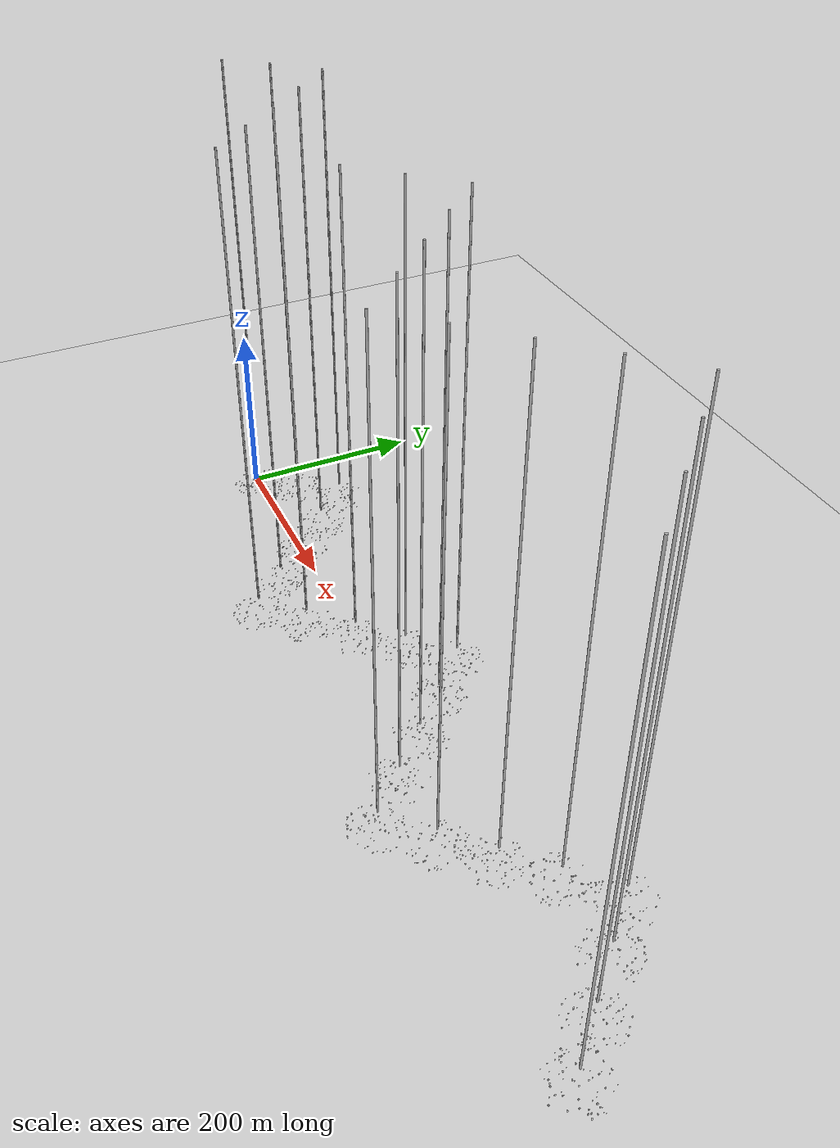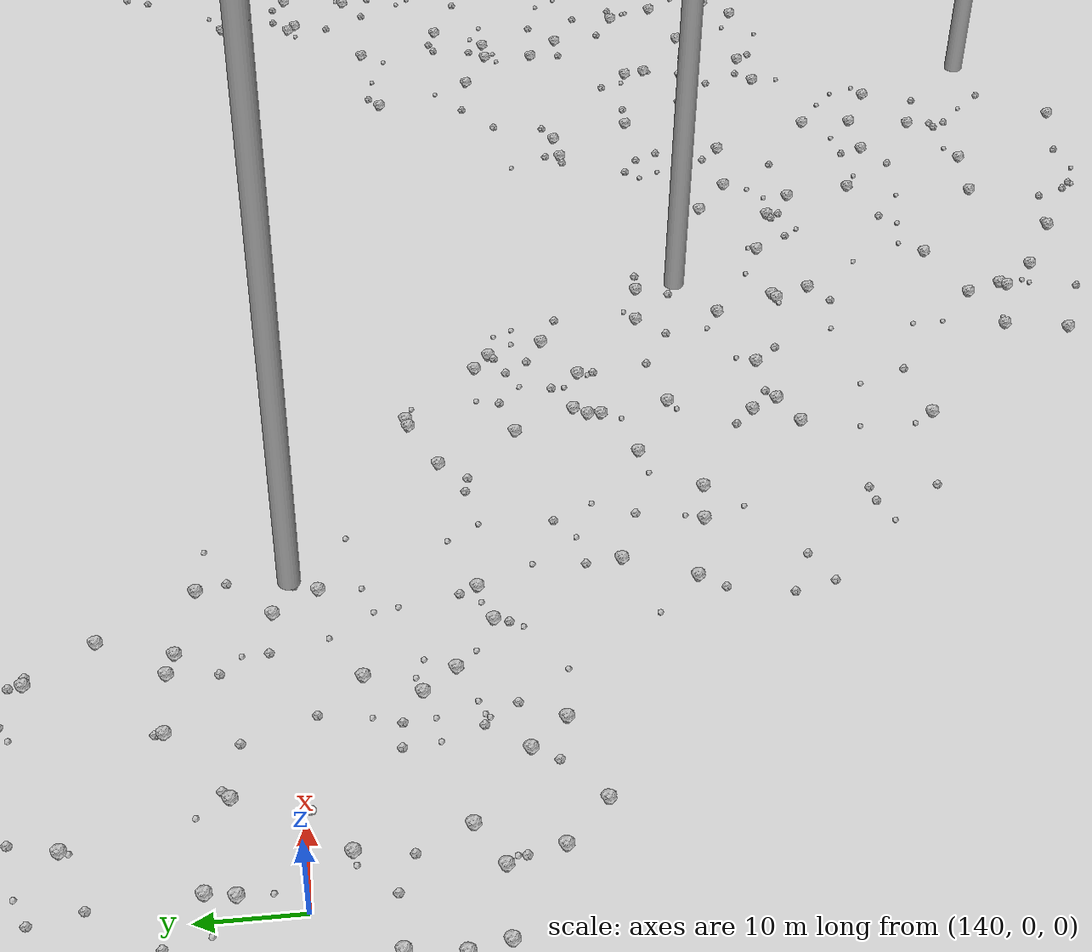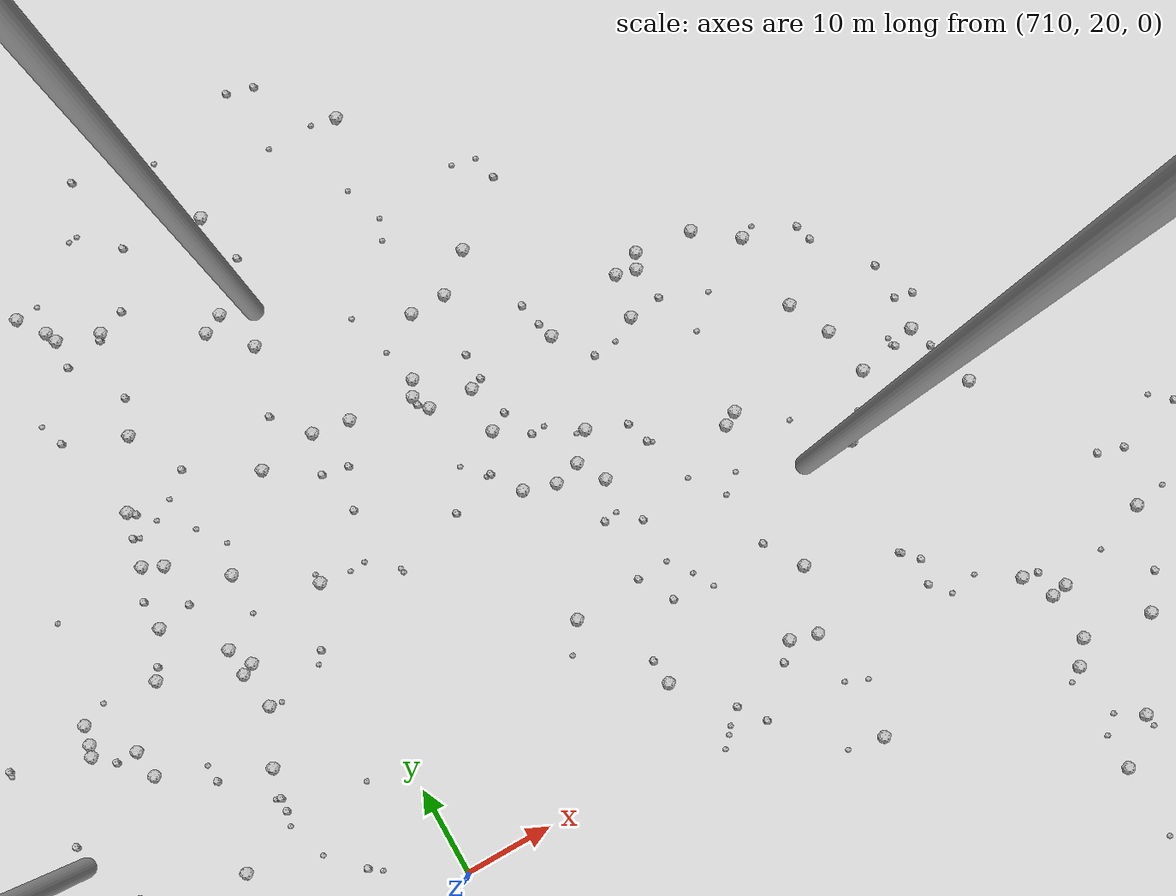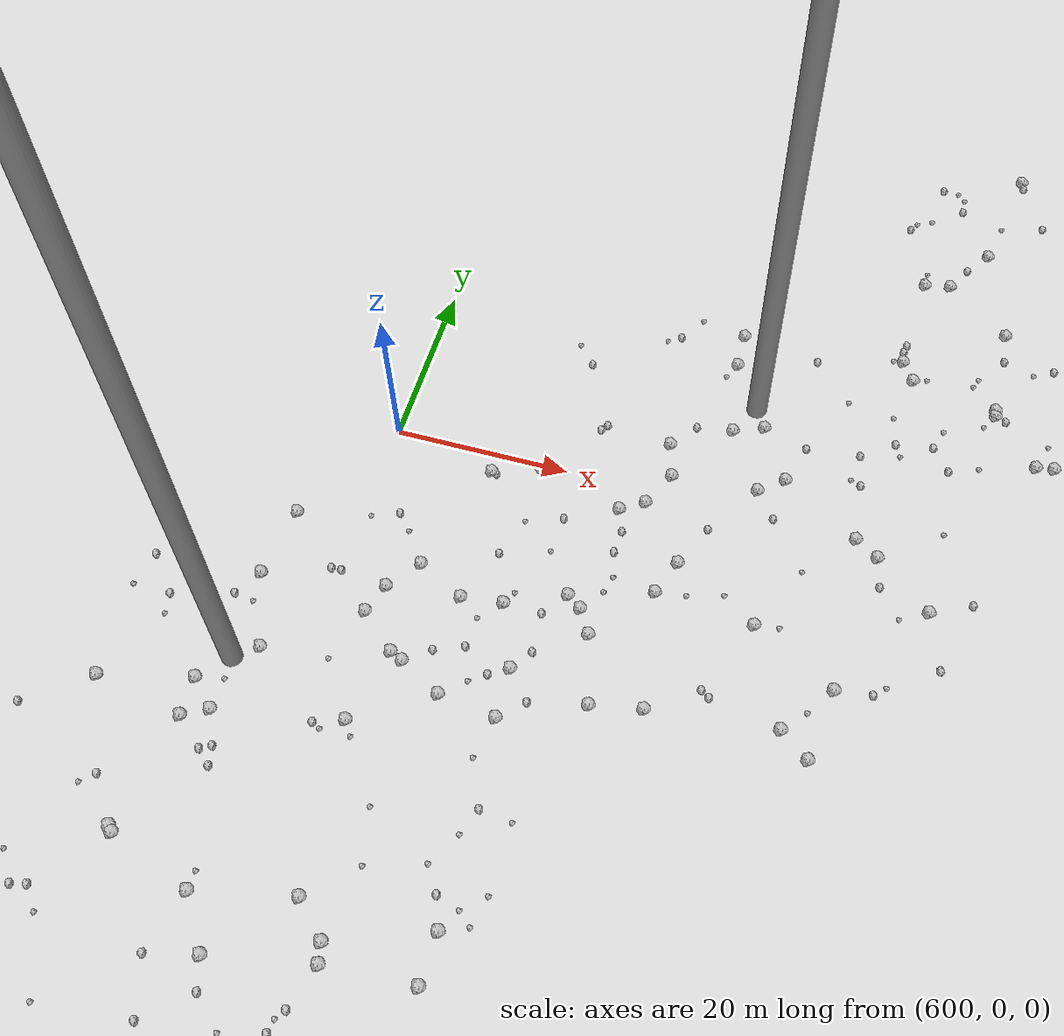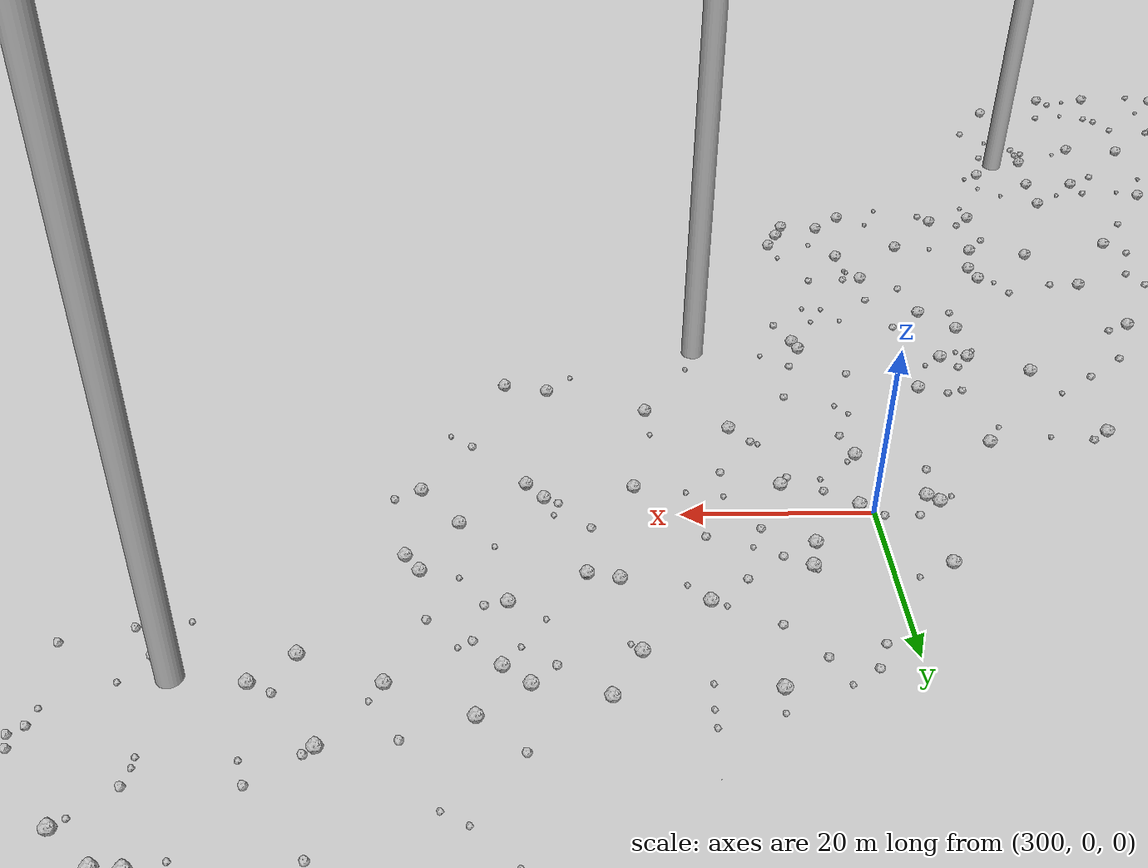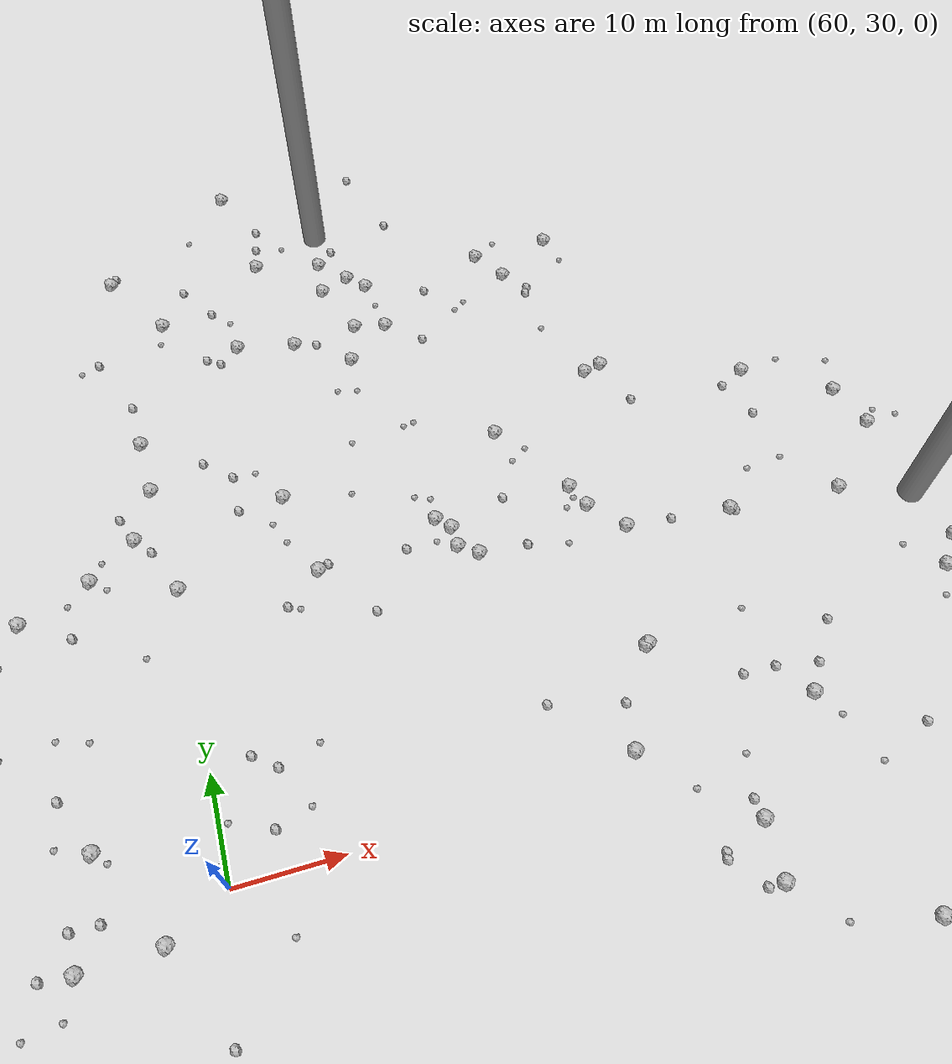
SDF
<sdf version="1.6">
 <world name="default">
  <include><uri>model://custom_ground</uri></include>
  <include><uri>model://sun</uri></include>
  <spherical_coordinates>
   <surface_model>EARTH_WGS84</surface_model>
   <latitude_deg>38.161479</latitude_deg>
   <longitude_deg>-122.454630</longitude_deg>
   <elevation>488.0</elevation>
   <heading_deg>90</heading_deg>
  </spherical_coordinates>
  <model name="rock1_0_0">
   <include><uri>model://rock1</uri><pose>28.164527271672952 -0.1924304792553997 0.5 0 0 0</pose></include>
  </model>
  <model name="rock1_0_1">
   <include><uri>model://rock1</uri><pose>23.76968117414482 6.400986430496815 0.5 0 0 0</pose></include>
  </model>
  <model name="rock1_0_2">
   <include><uri>model://rock1</uri><pose>27.977021827196104 23.02473839625312 0.5 0 0 0</pose></include>
  </model>
  <model name="rock1_0_3">
   <include><uri>model://rock1</uri><pose>-9.01086744708053 -9.468487440815448 0.5 0 0 0</pose></include>
  </model>
  <model name="rock1_0_4">
   <include><uri>model://rock1</uri><pose>23.09937537795968 -9.875111449607296 0.5 0 0 0</pose></include>
  </model>
  <model name="rock1_0_5">
   <include><uri>model://rock1</uri><pose>-3.7214753069233026 5.8805708543291715 0.5 0 0 0</pose></include>
  </model>
  <model name="rock1_0_6">
   <include><uri>model://rock1</uri><pose>11.723046146962169 -11.658758871404338 0.5 0 0 0</pose></include>
  </model>
  <model name="rock1_0_7">
   <include><uri>model://rock1</uri><pose>22.63035747315947 -25.432792986199047 0.5 0 0 0</pose></include>
  </model>
  <model name="rock1_0_8">
   <include><uri>model://rock1</uri><pose>28.51787171655964 -21.629123157213485 0.5 0 0 0</pose></include>
  </model>
  <model name="rock1_0_9">
   <include><uri>model://rock1</uri><pose>1.2296311382996166 27.657804357177667 0.5 0 0 0</pose></include>
  </model>
  <model name="rock1_0_10">
   <include><uri>model://rock1</uri><pose>5.596517588622675 -22.598671630933303 0.5 0 0 0</pose></include>
  </model>
  <model name="rock1_0_11">
   <include><uri>model://rock1</uri><pose>-3.4435045400110695 -21.515373480850116 0.5 0 0 0</pose></include>
  </model>
  <model name="rock1_0_12">
   <include><uri>model://rock1</uri><pose>-5.0530318960231035 14.56757697332705 0.5 0 0 0</pose></include>
  </model>
  <model name="rock1_0_13">
   <include><uri>model://rock1</uri><pose>1.753447125110906 -27.659550877434114 0.5 0 0 0</pose></include>
  </model>
  <model name="rock1_0_14">
   <include><uri>model://rock1</uri><pose>1.2820579549983009 -5.18686896027944 0.5 0 0 0</pose></include>
  </model>
  <model name="rock1_0_15">
   <include><uri>model://rock1</uri><pose>6.8382860505347125 -18.869072955272276 0.5 0 0 0</pose></include>
  </model>
  <model name="rock1_0_16">
   <include><uri>model://rock1</uri><pose>-11.333141751451098 13.800850390392917 0.5 0 0 0</pose></include>
  </model>
  <model name="rock1_0_17">
   <include><uri>model://rock1</uri><pose>-1.0893406360011184 23.960876699987814 0.5 0 0 0</pose></include>
  </model>
  <model name="rock1_0_18">
   <include><uri>model://rock1</uri><pose>1.7912922310670965 -20.16994230933908 0.5 0 0 0</pose></include>
  </model>
  <model name="rock1_0_19">
   <include><uri>model://rock1</uri><pose>-2.1467078241109654 13.54674496503192 0.5 0 0 0</pose></include>
  </model>
  <model name="rock1_0_20">
   <include><uri>model://rock1</uri><pose>-14.702006098364537 -11.74444503754049 0.5 0 0 0</pose></include>
  </model>
  <model name="rock1_0_21">
   <include><uri>model://rock1</uri><pose>-4.765070638609728 11.281723124268083 0.5 0 0 0</pose></include>
  </model>
  <model name="rock1_0_22">
   <include><uri>model://rock1</uri><pose>6.151205052815406 -19.62374623962574 0.5 0 0 0</pose></include>
  </model>
  <model name="rock1_0_23">
   <include><uri>model://rock1</uri><pose>6.797917934890137 -7.539143879765003 0.5 0 0 0</pose></include>
  </model>
  <model name="rock1_0_24">
   <include><uri>model://rock1</uri><pose>14.539653462869325 -10.883849346335609 0.5 0 0 0</pose></include>
  </model>
  <model name="rock1_0_25">
   <include><uri>model://rock1</uri><pose>22.069461308090283 0.8935633639868215 0.5 0 0 0</pose></include>
  </model>
  <model name="rock1_0_26">
   <include><uri>model://rock1</uri><pose>12.660475383180398 -13.033910417689526 0.5 0 0 0</pose></include>
  </model>
  <model name="rock2_0_0">
   <include><uri>model://rock2</uri><pose>-6.836833530695669 -8.007778371287095 0.3 0 0 0</pose></include>
  </model>
  <model name="rock2_0_1">
   <include><uri>model://rock2</uri><pose>8.265625455849431 -9.144436509427322 0.3 0 0 0</pose></include>
  </model>
  <model name="rock2_0_2">
   <include><uri>model://rock2</uri><pose>0.20141086636619576 21.07049008825858 0.3 0 0 0</pose></include>
  </model>
  <model name="rock2_0_3">
   <include><uri>model://rock2</uri><pose>28.797860994021732 13.46616178434369 0.3 0 0 0</pose></include>
  </model>
  <model name="rock2_0_4">
   <include><uri>model://rock2</uri><pose>19.001816478733126 -26.50103819490842 0.3 0 0 0</pose></include>
  </model>
  <model name="rock2_0_5">
   <include><uri>model://rock2</uri><pose>-11.325027479449252 20.55701517632172 0.3 0 0 0</pose></include>
  </model>
  <model name="rock2_0_6">
   <include><uri>model://rock2</uri><pose>14.357816836031553 -22.184563736346504 0.3 0 0 0</pose></include>
  </model>
  <model name="rock2_0_7">
   <include><uri>model://rock2</uri><pose>14.186706681999894 -27.092919898628764 0.3 0 0 0</pose></include>
  </model>
  <model name="rock2_0_8">
   <include><uri>model://rock2</uri><pose>12.492962902234858 3.6095414498595204 0.3 0 0 0</pose></include>
  </model>
  <model name="rock2_0_9">
   <include><uri>model://rock2</uri><pose>-17.913112849164236 -8.467963703942821 0.3 0 0 0</pose></include>
  </model>
  <model name="rock2_0_10">
   <include><uri>model://rock2</uri><pose>4.013436694726419 27.67755216931492 0.3 0 0 0</pose></include>
  </model>
  <model name="rock2_0_11">
   <include><uri>model://rock2</uri><pose>-2.9442792864211356 -11.491976817228093 0.3 0 0 0</pose></include>
  </model>
  <model name="rock2_0_12">
   <include><uri>model://rock2</uri><pose>33.40684740374053 17.53290991610151 0.3 0 0 0</pose></include>
  </model>
  <model name="rock2_0_13">
   <include><uri>model://rock2</uri><pose>7.440498466182593 -24.098210554650187 0.3 0 0 0</pose></include>
  </model>
  <model name="rock2_0_14">
   <include><uri>model://rock2</uri><pose>22.290063849603676 22.94453687206976 0.3 0 0 0</pose></include>
  </model>
  <model name="rock2_0_15">
   <include><uri>model://rock2</uri><pose>-6.404152587117434 22.17523660805537 0.3 0 0 0</pose></include>
  </model>
  <model name="rock2_0_16">
   <include><uri>model://rock2</uri><pose>0.39661946883234833 25.777261578468995 0.3 0 0 0</pose></include>
  </model>
  <model name="rock2_0_17">
   <include><uri>model://rock2</uri><pose>0.7469694550405563 -19.255737183829012 0.3 0 0 0</pose></include>
  </model>
  <model name="rock2_0_18">
   <include><uri>model://rock2</uri><pose>15.194922827029693 18.521162433937747 0.3 0 0 0</pose></include>
  </model>
  <model name="rock2_0_19">
   <include><uri>model://rock2</uri><pose>0.8921547741559337 -27.945454543513467 0.3 0 0 0</pose></include>
  </model>
  <model name="rock2_0_20">
   <include><uri>model://rock2</uri><pose>28.382652205752883 7.466068308630852 0.3 0 0 0</pose></include>
  </model>
  <model name="rock2_0_21">
   <include><uri>model://rock2</uri><pose>10.556472635340764 9.330002461730295 0.3 0 0 0</pose></include>
  </model>
  <model name="rock2_0_22">
   <include><uri>model://rock2</uri><pose>38.43246105460997 -4.588104483157693 0.3 0 0 0</pose></include>
  </model>
  <model name="rock2_0_23">
   <include><uri>model://rock2</uri><pose>32.25268000098687 -19.50213340432473 0.3 0 0 0</pose></include>
  </model>
  <model name="rock2_0_24">
   <include><uri>model://rock2</uri><pose>22.553097573165758 -24.81857861596783 0.3 0 0 0</pose></include>
  </model>
  <model name="rock2_0_25">
   <include><uri>model://rock2</uri><pose>-8.207944640817475 -21.137582881073705 0.3 0 0 0</pose></include>
  </model>
  <model name="rock2_0_26">
   <include><uri>model://rock2</uri><pose>19.967354624847516 16.85099578591261 0.3 0 0 0</pose></include>
  </model>
  <model name="rock3_0_0">
   <include><uri>model://rock3</uri><pose>10.538686775296593 -27.860117495546202 0.2 0 0 0</pose></include>
  </model>
  <model name="rock3_0_1">
   <include><uri>model://rock3</uri><pose>-8.240402194448482 -9.474680197306157 0.2 0 0 0</pose></include>
  </model>
  <model name="rock3_0_2">
   <include><uri>model://rock3</uri><pose>-5.2838951278435236 -1.7613773371454613 0.2 0 0 0</pose></include>
  </model>
  <model name="rock3_0_3">
   <include><uri>model://rock3</uri><pose>24.245672902668204 12.215946945206476 0.2 0 0 0</pose></include>
  </model>
  <model name="rock3_0_4">
   <include><uri>model://rock3</uri><pose>11.141891697416053 18.02346754939908 0.2 0 0 0</pose></include>
  </model>
  <model name="rock3_0_5">
   <include><uri>model://rock3</uri><pose>16.892807326778197 -19.35254898198168 0.2 0 0 0</pose></include>
  </model>
  <model name="rock3_0_6">
   <include><uri>model://rock3</uri><pose>23.14444433929146 -19.392707566069106 0.2 0 0 0</pose></include>
  </model>
  <model name="rock3_0_7">
   <include><uri>model://rock3</uri><pose>-14.268519570938558 -8.803358138252989 0.2 0 0 0</pose></include>
  </model>
  <model name="rock3_0_8">
   <include><uri>model://rock3</uri><pose>28.83215984620496 22.091074064769252 0.2 0 0 0</pose></include>
  </model>
  <model name="rock3_0_9">
   <include><uri>model://rock3</uri><pose>-13.927441247494938 1.3896657610578167 0.2 0 0 0</pose></include>
  </model>
  <model name="rock3_0_10">
   <include><uri>model://rock3</uri><pose>-4.187000374937783 8.48978183856994 0.2 0 0 0</pose></include>
  </model>
  <model name="rock3_0_11">
   <include><uri>model://rock3</uri><pose>9.751775227953587 -17.380637317592985 0.2 0 0 0</pose></include>
  </model>
  <model name="rock3_0_12">
   <include><uri>model://rock3</uri><pose>34.36754855018158 -14.753321412968447 0.2 0 0 0</pose></include>
  </model>
  <model name="rock3_0_13">
   <include><uri>model://rock3</uri><pose>1.0399486190987872 18.485735991499 0.2 0 0 0</pose></include>
  </model>
  <model name="rock3_0_14">
   <include><uri>model://rock3</uri><pose>13.026958295409834 0.5524754879924103 0.2 0 0 0</pose></include>
  </model>
  <model name="rock3_0_15">
   <include><uri>model://rock3</uri><pose>27.83453340704441 -10.775621999117543 0.2 0 0 0</pose></include>
  </model>
  <model name="rock3_0_16">
   <include><uri>model://rock3</uri><pose>9.185279509583722 -21.277306985229238 0.2 0 0 0</pose></include>
  </model>
  <model name="rock3_0_17">
   <include><uri>model://rock3</uri><pose>31.678590509152713 -14.741185476912138 0.2 0 0 0</pose></include>
  </model>
  <model name="rock3_0_18">
   <include><uri>model://rock3</uri><pose>16.292124239311136 -19.616381804860353 0.2 0 0 0</pose></include>
  </model>
  <model name="rock3_0_19">
   <include><uri>model://rock3</uri><pose>-1.891127863466778 -26.139618328960573 0.2 0 0 0</pose></include>
  </model>
  <model name="rock3_0_20">
   <include><uri>model://rock3</uri><pose>26.86478646134679 -10.381115571282095 0.2 0 0 0</pose></include>
  </model>
  <model name="rock3_0_21">
   <include><uri>model://rock3</uri><pose>18.143332971816008 7.096083502880063 0.2 0 0 0</pose></include>
  </model>
  <model name="rock3_0_22">
   <include><uri>model://rock3</uri><pose>9.562016046898385 7.641217422113314 0.2 0 0 0</pose></include>
  </model>
  <model name="rock3_0_23">
   <include><uri>model://rock3</uri><pose>8.426085864752661 -2.9769852476972645 0.2 0 0 0</pose></include>
  </model>
  <model name="rock3_0_24">
   <include><uri>model://rock3</uri><pose>28.667962378883715 -11.356884914135296 0.2 0 0 0</pose></include>
  </model>
  <model name="rock3_0_25">
   <include><uri>model://rock3</uri><pose>-5.420212483207695 10.260056014949576 0.2 0 0 0</pose></include>
  </model>
  <model name="rock3_0_26">
   <include><uri>model://rock3</uri><pose>9.902040175541131 -18.297696155876594 0.2 0 0 0</pose></include>
  </model>
  <model name="rock1_1_0">
   <include><uri>model://rock1</uri><pose>41.00833946250709 13.668584639086038 0.5 0 0 0</pose></include>
  </model>
  <model name="rock1_1_1">
   <include><uri>model://rock1</uri><pose>51.85607458014479 61.34541806532281 0.5 0 0 0</pose></include>
  </model>
  <model name="rock1_1_2">
   <include><uri>model://rock1</uri><pose>47.192138298626624 26.836435066059423 0.5 0 0 0</pose></include>
  </model>
  <model name="rock1_1_3">
   <include><uri>model://rock1</uri><pose>42.502618669998135 54.60149482086254 0.5 0 0 0</pose></include>
  </model>
  <model name="rock1_1_4">
   <include><uri>model://rock1</uri><pose>28.009540324787555 19.007732165847052 0.5 0 0 0</pose></include>
  </model>
  <model name="rock1_1_5">
   <include><uri>model://rock1</uri><pose>17.56278418221048 55.520285688032075 0.5 0 0 0</pose></include>
  </model>
  <model name="rock1_1_6">
   <include><uri>model://rock1</uri><pose>32.142126662488636 68.80712766515887 0.5 0 0 0</pose></include>
  </model>
  <model name="rock1_1_7">
   <include><uri>model://rock1</uri><pose>35.304859787249484 63.96181959804031 0.5 0 0 0</pose></include>
  </model>
  <model name="rock1_1_8">
   <include><uri>model://rock1</uri><pose>17.917485234590888 21.0709431442202 0.5 0 0 0</pose></include>
  </model>
  <model name="rock1_1_9">
   <include><uri>model://rock1</uri><pose>54.43492940484588 27.020234022973312 0.5 0 0 0</pose></include>
  </model>
  <model name="rock1_1_10">
   <include><uri>model://rock1</uri><pose>29.466718119077196 67.94599980738681 0.5 0 0 0</pose></include>
  </model>
  <model name="rock1_1_11">
   <include><uri>model://rock1</uri><pose>56.52073586163867 64.6812980233908 0.5 0 0 0</pose></include>
  </model>
  <model name="rock1_1_12">
   <include><uri>model://rock1</uri><pose>14.456386981502632 27.8305327094759 0.5 0 0 0</pose></include>
  </model>
  <model name="rock1_1_13">
   <include><uri>model://rock1</uri><pose>44.97730133476675 58.62435224719999 0.5 0 0 0</pose></include>
  </model>
  <model name="rock1_1_14">
   <include><uri>model://rock1</uri><pose>22.558757730155623 52.083437610040576 0.5 0 0 0</pose></include>
  </model>
  <model name="rock1_1_15">
   <include><uri>model://rock1</uri><pose>48.81339338860708 18.044787243840037 0.5 0 0 0</pose></include>
  </model>
  <model name="rock1_1_16">
   <include><uri>model://rock1</uri><pose>43.13137885750733 68.62483216427256 0.5 0 0 0</pose></include>
  </model>
  <model name="rock1_1_17">
   <include><uri>model://rock1</uri><pose>17.02391108476631 26.371599462478997 0.5 0 0 0</pose></include>
  </model>
  <model name="rock1_1_18">
   <include><uri>model://rock1</uri><pose>55.26948613822873 14.297576998252463 0.5 0 0 0</pose></include>
  </model>
  <model name="rock1_1_19">
   <include><uri>model://rock1</uri><pose>26.366031900823938 30.768612984555645 0.5 0 0 0</pose></include>
  </model>
  <model name="rock1_1_20">
   <include><uri>model://rock1</uri><pose>49.450536214855504 35.88623014439689 0.5 0 0 0</pose></include>
  </model>
  <model name="rock1_1_21">
   <include><uri>model://rock1</uri><pose>59.90200751670886 58.22104293935313 0.5 0 0 0</pose></include>
  </model>
  <model name="rock1_1_22">
   <include><uri>model://rock1</uri><pose>24.295188863231072 60.92542357425265 0.5 0 0 0</pose></include>
  </model>
  <model name="rock1_1_23">
   <include><uri>model://rock1</uri><pose>40.4448797437463 26.71648685880615 0.5 0 0 0</pose></include>
  </model>
  <model name="rock1_1_24">
   <include><uri>model://rock1</uri><pose>28.830991105216203 22.527967523758498 0.5 0 0 0</pose></include>
  </model>
  <model name="rock1_1_25">
   <include><uri>model://rock1</uri><pose>12.093619530369615 31.859029120803687 0.5 0 0 0</pose></include>
  </model>
  <model name="rock1_1_26">
   <include><uri>model://rock1</uri><pose>35.562211189108176 34.791637810112306 0.5 0 0 0</pose></include>
  </model>
  <model name="rock2_1_0">
   <include><uri>model://rock2</uri><pose>64.57090094394357 33.647500981867 0.3 0 0 0</pose></include>
  </model>
  <model name="rock2_1_1">
   <include><uri>model://rock2</uri><pose>42.19294606642556 46.21862415358629 0.3 0 0 0</pose></include>
  </model>
  <model name="rock2_1_2">
   <include><uri>model://rock2</uri><pose>33.03494652977115 51.787794519079256 0.3 0 0 0</pose></include>
  </model>
  <model name="rock2_1_3">
   <include><uri>model://rock2</uri><pose>58.50623873392472 18.201886771755316 0.3 0 0 0</pose></include>
  </model>
  <model name="rock2_1_4">
   <include><uri>model://rock2</uri><pose>30.128758873795192 43.36565936832876 0.3 0 0 0</pose></include>
  </model>
  <model name="rock2_1_5">
   <include><uri>model://rock2</uri><pose>37.58364078966804 18.966572176390912 0.3 0 0 0</pose></include>
  </model>
  <model name="rock2_1_6">
   <include><uri>model://rock2</uri><pose>65.810409736775 38.782983064534356 0.3 0 0 0</pose></include>
  </model>
  <model name="rock2_1_7">
   <include><uri>model://rock2</uri><pose>12.616980819840723 43.12125234494391 0.3 0 0 0</pose></include>
  </model>
  <model name="rock2_1_8">
   <include><uri>model://rock2</uri><pose>29.436484274616312 45.51204884893254 0.3 0 0 0</pose></include>
  </model>
  <model name="rock2_1_9">
   <include><uri>model://rock2</uri><pose>22.538862749010804 43.59763432211187 0.3 0 0 0</pose></include>
  </model>
  <model name="rock2_1_10">
   <include><uri>model://rock2</uri><pose>29.05535662859926 63.35982272873505 0.3 0 0 0</pose></include>
  </model>
  <model name="rock2_1_11">
   <include><uri>model://rock2</uri><pose>41.71923534193957 63.12057113383416 0.3 0 0 0</pose></include>
  </model>
  <model name="rock2_1_12">
   <include><uri>model://rock2</uri><pose>36.305696113063675 39.45227784851395 0.3 0 0 0</pose></include>
  </model>
  <model name="rock2_1_13">
   <include><uri>model://rock2</uri><pose>46.02905444124622 10.673063595400151 0.3 0 0 0</pose></include>
  </model>
  <model name="rock2_1_14">
   <include><uri>model://rock2</uri><pose>26.381354908710815 65.09471675735543 0.3 0 0 0</pose></include>
  </model>
  <model name="rock2_1_15">
   <include><uri>model://rock2</uri><pose>44.65709933253174 10.517158441264392 0.3 0 0 0</pose></include>
  </model>
  <model name="rock2_1_16">
   <include><uri>model://rock2</uri><pose>44.26612165722023 27.148914576257685 0.3 0 0 0</pose></include>
  </model>
  <model name="rock2_1_17">
   <include><uri>model://rock2</uri><pose>49.64160770851051 55.91944253547199 0.3 0 0 0</pose></include>
  </model>
  <model name="rock2_1_18">
   <include><uri>model://rock2</uri><pose>39.39499647646211 57.25273069593383 0.3 0 0 0</pose></include>
  </model>
  <model name="rock2_1_19">
   <include><uri>model://rock2</uri><pose>63.71821341221446 40.423887807119385 0.3 0 0 0</pose></include>
  </model>
  <model name="rock2_1_20">
   <include><uri>model://rock2</uri><pose>57.94223549188114 62.964970232727225 0.3 0 0 0</pose></include>
  </model>
  <model name="rock2_1_21">
   <include><uri>model://rock2</uri><pose>29.79204463056118 57.61318768413814 0.3 0 0 0</pose></include>
  </model>
  <model name="rock2_1_22">
   <include><uri>model://rock2</uri><pose>26.38636572863254 41.933867262617646 0.3 0 0 0</pose></include>
  </model>
  <model name="rock2_1_23">
   <include><uri>model://rock2</uri><pose>46.97660254913397 30.185799205241434 0.3 0 0 0</pose></include>
  </model>
  <model name="rock2_1_24">
   <include><uri>model://rock2</uri><pose>20.771912753735187 26.76442005040226 0.3 0 0 0</pose></include>
  </model>
  <model name="rock2_1_25">
   <include><uri>model://rock2</uri><pose>49.5344403515373 30.115149314231417 0.3 0 0 0</pose></include>
  </model>
  <model name="rock2_1_26">
   <include><uri>model://rock2</uri><pose>46.985106480268506 41.03598556175997 0.3 0 0 0</pose></include>
  </model>
  <model name="rock3_1_0">
   <include><uri>model://rock3</uri><pose>37.80314975306831 32.19649591488235 0.2 0 0 0</pose></include>
  </model>
  <model name="rock3_1_1">
   <include><uri>model://rock3</uri><pose>28.965992929400297 36.999886355457235 0.2 0 0 0</pose></include>
  </model>
  <model name="rock3_1_2">
   <include><uri>model://rock3</uri><pose>39.739943671085776 28.418535832047382 0.2 0 0 0</pose></include>
  </model>
  <model name="rock3_1_3">
   <include><uri>model://rock3</uri><pose>53.29126789534848 60.106665915980564 0.2 0 0 0</pose></include>
  </model>
  <model name="rock3_1_4">
   <include><uri>model://rock3</uri><pose>69.743921389084 39.94876006835275 0.2 0 0 0</pose></include>
  </model>
  <model name="rock3_1_5">
   <include><uri>model://rock3</uri><pose>67.93490610086877 34.67626444184508 0.2 0 0 0</pose></include>
  </model>
  <model name="rock3_1_6">
   <include><uri>model://rock3</uri><pose>47.27938727329988 46.42429178129175 0.2 0 0 0</pose></include>
  </model>
  <model name="rock3_1_7">
   <include><uri>model://rock3</uri><pose>29.837793714358824 17.06125306213572 0.2 0 0 0</pose></include>
  </model>
  <model name="rock3_1_8">
   <include><uri>model://rock3</uri><pose>34.60778751250169 19.308247927708845 0.2 0 0 0</pose></include>
  </model>
  <model name="rock3_1_9">
   <include><uri>model://rock3</uri><pose>59.41186788093845 31.905564361836817 0.2 0 0 0</pose></include>
  </model>
  <model name="rock3_1_10">
   <include><uri>model://rock3</uri><pose>10.122577065004661 40.938729229220456 0.2 0 0 0</pose></include>
  </model>
  <model name="rock3_1_11">
   <include><uri>model://rock3</uri><pose>42.66823334331609 23.21577208377525 0.2 0 0 0</pose></include>
  </model>
  <model name="rock3_1_12">
   <include><uri>model://rock3</uri><pose>31.69630542162057 35.007663456433505 0.2 0 0 0</pose></include>
  </model>
  <model name="rock3_1_13">
   <include><uri>model://rock3</uri><pose>39.53391542358399 61.66498992583205 0.2 0 0 0</pose></include>
  </model>
  <model name="rock3_1_14">
   <include><uri>model://rock3</uri><pose>49.51097177555784 59.3159496912815 0.2 0 0 0</pose></include>
  </model>
  <model name="rock3_1_15">
   <include><uri>model://rock3</uri><pose>64.5301036742677 24.782709784457268 0.2 0 0 0</pose></include>
  </model>
  <model name="rock3_1_16">
   <include><uri>model://rock3</uri><pose>49.15125694320157 12.140084759756618 0.2 0 0 0</pose></include>
  </model>
  <model name="rock3_1_17">
   <include><uri>model://rock3</uri><pose>45.95090909310844 23.67610938729232 0.2 0 0 0</pose></include>
  </model>
  <model name="rock3_1_18">
   <include><uri>model://rock3</uri><pose>46.349468971898816 37.043488435191286 0.2 0 0 0</pose></include>
  </model>
  <model name="rock3_1_19">
   <include><uri>model://rock3</uri><pose>60.75074316707454 35.24575455705078 0.2 0 0 0</pose></include>
  </model>
  <model name="rock3_1_20">
   <include><uri>model://rock3</uri><pose>50.56065461174064 34.732067529971474 0.2 0 0 0</pose></include>
  </model>
  <model name="rock3_1_21">
   <include><uri>model://rock3</uri><pose>19.185699936873903 22.449184288985233 0.2 0 0 0</pose></include>
  </model>
  <model name="rock3_1_22">
   <include><uri>model://rock3</uri><pose>53.109662610723866 63.06509906775032 0.2 0 0 0</pose></include>
  </model>
  <model name="rock3_1_23">
   <include><uri>model://rock3</uri><pose>40.92463265602408 62.84488640117632 0.2 0 0 0</pose></include>
  </model>
  <model name="rock3_1_24">
   <include><uri>model://rock3</uri><pose>50.17913066724131 45.51734330945648 0.2 0 0 0</pose></include>
  </model>
  <model name="rock3_1_25">
   <include><uri>model://rock3</uri><pose>56.0371027751312 52.04831152556151 0.2 0 0 0</pose></include>
  </model>
  <model name="rock3_1_26">
   <include><uri>model://rock3</uri><pose>16.812761079736223 36.4769662216831 0.2 0 0 0</pose></include>
  </model>
  <model name="rock1_2_0">
   <include><uri>model://rock1</uri><pose>99.11732407064758 91.21554409748677 0.5 0 0 0</pose></include>
  </model>
  <model name="rock1_2_1">
   <include><uri>model://rock1</uri><pose>81.98233631030038 80.55606769294577 0.5 0 0 0</pose></include>
  </model>
  <model name="rock1_2_2">
   <include><uri>model://rock1</uri><pose>85.82894328379139 90.37499426903254 0.5 0 0 0</pose></include>
  </model>
  <model name="rock1_2_3">
   <include><uri>model://rock1</uri><pose>83.33838280752079 84.95726165532562 0.5 0 0 0</pose></include>
  </model>
  <model name="rock1_2_4">
   <include><uri>model://rock1</uri><pose>86.81544320201611 55.405485484046416 0.5 0 0 0</pose></include>
  </model>
  <model name="rock1_2_5">
   <include><uri>model://rock1</uri><pose>105.76144355512287 72.03884882196228 0.5 0 0 0</pose></include>
  </model>
  <model name="rock1_2_6">
   <include><uri>model://rock1</uri><pose>86.64915491618143 84.26049635040339 0.5 0 0 0</pose></include>
  </model>
  <model name="rock1_2_7">
   <include><uri>model://rock1</uri><pose>76.44440581410907 84.32721424944535 0.5 0 0 0</pose></include>
  </model>
  <model name="rock1_2_8">
   <include><uri>model://rock1</uri><pose>71.45596082558957 65.5188617763888 0.5 0 0 0</pose></include>
  </model>
  <model name="rock1_2_9">
   <include><uri>model://rock1</uri><pose>81.40600063182835 94.97420977915037 0.5 0 0 0</pose></include>
  </model>
  <model name="rock1_2_10">
   <include><uri>model://rock1</uri><pose>101.34237849747859 87.7268895697525 0.5 0 0 0</pose></include>
  </model>
  <model name="rock1_2_11">
   <include><uri>model://rock1</uri><pose>73.18864632524868 56.54464812000349 0.5 0 0 0</pose></include>
  </model>
  <model name="rock1_2_12">
   <include><uri>model://rock1</uri><pose>70.34494076701705 85.60005878594922 0.5 0 0 0</pose></include>
  </model>
  <model name="rock1_2_13">
   <include><uri>model://rock1</uri><pose>107.68772720923197 72.526169967021 0.5 0 0 0</pose></include>
  </model>
  <model name="rock1_2_14">
   <include><uri>model://rock1</uri><pose>58.064092844559326 98.43239745945235 0.5 0 0 0</pose></include>
  </model>
  <model name="rock1_2_15">
   <include><uri>model://rock1</uri><pose>72.33613535368725 108.38360449295844 0.5 0 0 0</pose></include>
  </model>
  <model name="rock1_2_16">
   <include><uri>model://rock1</uri><pose>58.80575868712978 69.91061179551106 0.5 0 0 0</pose></include>
  </model>
  <model name="rock1_2_17">
   <include><uri>model://rock1</uri><pose>94.14835199882079 67.09181474464798 0.5 0 0 0</pose></include>
  </model>
  <model name="rock1_2_18">
   <include><uri>model://rock1</uri><pose>86.76859346868102 57.541126405816335 0.5 0 0 0</pose></include>
  </model>
  <model name="rock1_2_19">
   <include><uri>model://rock1</uri><pose>88.6107752397598 54.062116020795926 0.5 0 0 0</pose></include>
  </model>
  <model name="rock1_2_20">
   <include><uri>model://rock1</uri><pose>74.43397470353226 96.64721083297665 0.5 0 0 0</pose></include>
  </model>
  <model name="rock1_2_21">
   <include><uri>model://rock1</uri><pose>107.51207095003983 91.48941019553604 0.5 0 0 0</pose></include>
  </model>
  <model name="rock1_2_22">
   <include><uri>model://rock1</uri><pose>84.06398617324325 92.16016347292666 0.5 0 0 0</pose></include>
  </model>
  <model name="rock1_2_23">
   <include><uri>model://rock1</uri><pose>85.51563960974003 58.91055630479486 0.5 0 0 0</pose></include>
  </model>
  <model name="rock1_2_24">
   <include><uri>model://rock1</uri><pose>62.88239278969495 90.904295362256 0.5 0 0 0</pose></include>
  </model>
  <model name="rock1_2_25">
   <include><uri>model://rock1</uri><pose>80.99386654045415 90.93029214771417 0.5 0 0 0</pose></include>
  </model>
  <model name="rock1_2_26">
   <include><uri>model://rock1</uri><pose>58.56485555390752 75.78956912933452 0.5 0 0 0</pose></include>
  </model>
  <model name="rock2_2_0">
   <include><uri>model://rock2</uri><pose>90.07571966645449 99.10707539047247 0.3 0 0 0</pose></include>
  </model>
  <model name="rock2_2_1">
   <include><uri>model://rock2</uri><pose>74.19279602640862 56.987299342294364 0.3 0 0 0</pose></include>
  </model>
  <model name="rock2_2_2">
   <include><uri>model://rock2</uri><pose>78.6946616925835 83.6970277835514 0.3 0 0 0</pose></include>
  </model>
  <model name="rock2_2_3">
   <include><uri>model://rock2</uri><pose>68.1817329450299 83.97910941143425 0.3 0 0 0</pose></include>
  </model>
  <model name="rock2_2_4">
   <include><uri>model://rock2</uri><pose>75.29874849756621 102.07579063963959 0.3 0 0 0</pose></include>
  </model>
  <model name="rock2_2_5">
   <include><uri>model://rock2</uri><pose>64.34434609367918 71.71425622524325 0.3 0 0 0</pose></include>
  </model>
  <model name="rock2_2_6">
   <include><uri>model://rock2</uri><pose>74.81348971732902 99.34685431239274 0.3 0 0 0</pose></include>
  </model>
  <model name="rock2_2_7">
   <include><uri>model://rock2</uri><pose>55.465079530948074 87.3142212825986 0.3 0 0 0</pose></include>
  </model>
  <model name="rock2_2_8">
   <include><uri>model://rock2</uri><pose>92.60448205085567 59.4322426012999 0.3 0 0 0</pose></include>
  </model>
  <model name="rock2_2_9">
   <include><uri>model://rock2</uri><pose>77.58146752501465 50.869161064204185 0.3 0 0 0</pose></include>
  </model>
  <model name="rock2_2_10">
   <include><uri>model://rock2</uri><pose>103.39742098791982 85.287346635933 0.3 0 0 0</pose></include>
  </model>
  <model name="rock2_2_11">
   <include><uri>model://rock2</uri><pose>69.57777471604268 53.5892755938474 0.3 0 0 0</pose></include>
  </model>
  <model name="rock2_2_12">
   <include><uri>model://rock2</uri><pose>81.88580856934493 56.469578043873646 0.3 0 0 0</pose></include>
  </model>
  <model name="rock2_2_13">
   <include><uri>model://rock2</uri><pose>87.4796256819514 107.65132062191114 0.3 0 0 0</pose></include>
  </model>
  <model name="rock2_2_14">
   <include><uri>model://rock2</uri><pose>83.1161584748904 96.65242090609357 0.3 0 0 0</pose></include>
  </model>
  <model name="rock2_2_15">
   <include><uri>model://rock2</uri><pose>102.99857975319586 84.50616751125831 0.3 0 0 0</pose></include>
  </model>
  <model name="rock2_2_16">
   <include><uri>model://rock2</uri><pose>66.89830361263094 65.22291651021169 0.3 0 0 0</pose></include>
  </model>
  <model name="rock2_2_17">
   <include><uri>model://rock2</uri><pose>58.651720503480256 99.26647377658894 0.3 0 0 0</pose></include>
  </model>
  <model name="rock2_2_18">
   <include><uri>model://rock2</uri><pose>92.03272977484289 87.9776937676802 0.3 0 0 0</pose></include>
  </model>
  <model name="rock2_2_19">
   <include><uri>model://rock2</uri><pose>58.25132186797967 80.69599603512073 0.3 0 0 0</pose></include>
  </model>
  <model name="rock2_2_20">
   <include><uri>model://rock2</uri><pose>66.99874009799035 69.27449150243099 0.3 0 0 0</pose></include>
  </model>
  <model name="rock2_2_21">
   <include><uri>model://rock2</uri><pose>93.42314095368059 53.73331751634622 0.3 0 0 0</pose></include>
  </model>
  <model name="rock2_2_22">
   <include><uri>model://rock2</uri><pose>65.75497915967155 95.11611238323678 0.3 0 0 0</pose></include>
  </model>
  <model name="rock2_2_23">
   <include><uri>model://rock2</uri><pose>68.33669684381628 91.16355478790663 0.3 0 0 0</pose></include>
  </model>
  <model name="rock2_2_24">
   <include><uri>model://rock2</uri><pose>66.815735487062 84.84508556615373 0.3 0 0 0</pose></include>
  </model>
  <model name="rock2_2_25">
   <include><uri>model://rock2</uri><pose>55.38253418841844 67.38472569709762 0.3 0 0 0</pose></include>
  </model>
  <model name="rock2_2_26">
   <include><uri>model://rock2</uri><pose>90.08185768343745 81.29751395039884 0.3 0 0 0</pose></include>
  </model>
  <model name="rock3_2_0">
   <include><uri>model://rock3</uri><pose>77.68904844796812 98.65858102963233 0.2 0 0 0</pose></include>
  </model>
  <model name="rock3_2_1">
   <include><uri>model://rock3</uri><pose>84.94816517901413 56.467616400979814 0.2 0 0 0</pose></include>
  </model>
  <model name="rock3_2_2">
   <include><uri>model://rock3</uri><pose>95.90342988847232 85.20922608760105 0.2 0 0 0</pose></include>
  </model>
  <model name="rock3_2_3">
   <include><uri>model://rock3</uri><pose>70.70023212716664 53.05369442980378 0.2 0 0 0</pose></include>
  </model>
  <model name="rock3_2_4">
   <include><uri>model://rock3</uri><pose>67.44961710052198 102.52408763264293 0.2 0 0 0</pose></include>
  </model>
  <model name="rock3_2_5">
   <include><uri>model://rock3</uri><pose>70.08572659255113 89.30407988494194 0.2 0 0 0</pose></include>
  </model>
  <model name="rock3_2_6">
   <include><uri>model://rock3</uri><pose>78.15657561246742 64.0741407573354 0.2 0 0 0</pose></include>
  </model>
  <model name="rock3_2_7">
   <include><uri>model://rock3</uri><pose>94.65939195350938 84.35350587329518 0.2 0 0 0</pose></include>
  </model>
  <model name="rock3_2_8">
   <include><uri>model://rock3</uri><pose>96.54520881795631 64.464794944803 0.2 0 0 0</pose></include>
  </model>
  <model name="rock3_2_9">
   <include><uri>model://rock3</uri><pose>70.81694054801213 60.43364367628648 0.2 0 0 0</pose></include>
  </model>
  <model name="rock3_2_10">
   <include><uri>model://rock3</uri><pose>94.8637212671682 63.37831034363731 0.2 0 0 0</pose></include>
  </model>
  <model name="rock3_2_11">
   <include><uri>model://rock3</uri><pose>69.86711676334423 62.78048984262952 0.2 0 0 0</pose></include>
  </model>
  <model name="rock3_2_12">
   <include><uri>model://rock3</uri><pose>79.55506451579208 76.89430583105649 0.2 0 0 0</pose></include>
  </model>
  <model name="rock3_2_13">
   <include><uri>model://rock3</uri><pose>86.21762408339802 87.41980190996335 0.2 0 0 0</pose></include>
  </model>
  <model name="rock3_2_14">
   <include><uri>model://rock3</uri><pose>53.54447266347168 86.63873558471447 0.2 0 0 0</pose></include>
  </model>
  <model name="rock3_2_15">
   <include><uri>model://rock3</uri><pose>62.28900272355759 88.46789619073787 0.2 0 0 0</pose></include>
  </model>
  <model name="rock3_2_16">
   <include><uri>model://rock3</uri><pose>86.30656706532754 70.7873185572248 0.2 0 0 0</pose></include>
  </model>
  <model name="rock3_2_17">
   <include><uri>model://rock3</uri><pose>85.59371465653226 61.281825490553835 0.2 0 0 0</pose></include>
  </model>
  <model name="rock3_2_18">
   <include><uri>model://rock3</uri><pose>69.2571668033744 69.13794023030472 0.2 0 0 0</pose></include>
  </model>
  <model name="rock3_2_19">
   <include><uri>model://rock3</uri><pose>98.44252368761504 56.57497161140929 0.2 0 0 0</pose></include>
  </model>
  <model name="rock3_2_20">
   <include><uri>model://rock3</uri><pose>103.15464185461556 79.13465032370476 0.2 0 0 0</pose></include>
  </model>
  <model name="rock3_2_21">
   <include><uri>model://rock3</uri><pose>81.58531078922756 76.43532764029925 0.2 0 0 0</pose></include>
  </model>
  <model name="rock3_2_22">
   <include><uri>model://rock3</uri><pose>79.56397056736711 70.04374257129058 0.2 0 0 0</pose></include>
  </model>
  <model name="rock3_2_23">
   <include><uri>model://rock3</uri><pose>101.58691489591752 92.73342389413172 0.2 0 0 0</pose></include>
  </model>
  <model name="rock3_2_24">
   <include><uri>model://rock3</uri><pose>108.31157965245288 88.21052859845449 0.2 0 0 0</pose></include>
  </model>
  <model name="rock3_2_25">
   <include><uri>model://rock3</uri><pose>84.10581183712631 61.91015205582809 0.2 0 0 0</pose></include>
  </model>
  <model name="rock3_2_26">
   <include><uri>model://rock3</uri><pose>85.21788990621928 70.59367855433732 0.2 0 0 0</pose></include>
  </model>
  <model name="rock1_3_0">
   <include><uri>model://rock1</uri><pose>100.47398467913791 56.285475278616964 0.5 0 0 0</pose></include>
  </model>
  <model name="rock1_3_1">
   <include><uri>model://rock1</uri><pose>135.9107011526001 33.18366832072568 0.5 0 0 0</pose></include>
  </model>
  <model name="rock1_3_2">
   <include><uri>model://rock1</uri><pose>125.5557734381141 51.26425731231555 0.5 0 0 0</pose></include>
  </model>
  <model name="rock1_3_3">
   <include><uri>model://rock1</uri><pose>100.97431185746822 40.694110174657375 0.5 0 0 0</pose></include>
  </model>
  <model name="rock1_3_4">
   <include><uri>model://rock1</uri><pose>132.0209454495086 57.73127459904603 0.5 0 0 0</pose></include>
  </model>
  <model name="rock1_3_5">
   <include><uri>model://rock1</uri><pose>113.71675507634686 32.15815616295254 0.5 0 0 0</pose></include>
  </model>
  <model name="rock1_3_6">
   <include><uri>model://rock1</uri><pose>104.1816880648282 17.804819492809404 0.5 0 0 0</pose></include>
  </model>
  <model name="rock1_3_7">
   <include><uri>model://rock1</uri><pose>144.98968613399558 27.80446277302474 0.5 0 0 0</pose></include>
  </model>
  <model name="rock1_3_8">
   <include><uri>model://rock1</uri><pose>142.43806592193502 29.018816451321413 0.5 0 0 0</pose></include>
  </model>
  <model name="rock1_3_9">
   <include><uri>model://rock1</uri><pose>100.73502920846474 40.577732687490276 0.5 0 0 0</pose></include>
  </model>
  <model name="rock1_3_10">
   <include><uri>model://rock1</uri><pose>139.51184867555824 38.64199179393375 0.5 0 0 0</pose></include>
  </model>
  <model name="rock1_3_11">
   <include><uri>model://rock1</uri><pose>129.8489602022825 30.266225471594 0.5 0 0 0</pose></include>
  </model>
  <model name="rock1_3_12">
   <include><uri>model://rock1</uri><pose>131.70297603245328 40.43359481549807 0.5 0 0 0</pose></include>
  </model>
  <model name="rock1_3_13">
   <include><uri>model://rock1</uri><pose>132.12655843144117 17.68614921984374 0.5 0 0 0</pose></include>
  </model>
  <model name="rock1_3_14">
   <include><uri>model://rock1</uri><pose>133.98653562020178 43.22852367655199 0.5 0 0 0</pose></include>
  </model>
  <model name="rock1_3_15">
   <include><uri>model://rock1</uri><pose>130.4466547913129 62.47916478313608 0.5 0 0 0</pose></include>
  </model>
  <model name="rock1_3_16">
   <include><uri>model://rock1</uri><pose>114.05770484729965 52.02680463715218 0.5 0 0 0</pose></include>
  </model>
  <model name="rock1_3_17">
   <include><uri>model://rock1</uri><pose>135.78306484703768 22.81770063972766 0.5 0 0 0</pose></include>
  </model>
  <model name="rock1_3_18">
   <include><uri>model://rock1</uri><pose>104.68998784757147 23.034962870197916 0.5 0 0 0</pose></include>
  </model>
  <model name="rock1_3_19">
   <include><uri>model://rock1</uri><pose>122.0642121626945 67.55545347748595 0.5 0 0 0</pose></include>
  </model>
  <model name="rock1_3_20">
   <include><uri>model://rock1</uri><pose>103.45414323657243 52.96340676827736 0.5 0 0 0</pose></include>
  </model>
  <model name="rock1_3_21">
   <include><uri>model://rock1</uri><pose>99.46070777499601 58.807247054222344 0.5 0 0 0</pose></include>
  </model>
  <model name="rock1_3_22">
   <include><uri>model://rock1</uri><pose>115.41135741116324 11.86052166862246 0.5 0 0 0</pose></include>
  </model>
  <model name="rock1_3_23">
   <include><uri>model://rock1</uri><pose>144.29910798184324 48.88383553425349 0.5 0 0 0</pose></include>
  </model>
  <model name="rock1_3_24">
   <include><uri>model://rock1</uri><pose>138.66767622699962 48.02018336026434 0.5 0 0 0</pose></include>
  </model>
  <model name="rock1_3_25">
   <include><uri>model://rock1</uri><pose>148.186729130811 46.028399570363504 0.5 0 0 0</pose></include>
  </model>
  <model name="rock1_3_26">
   <include><uri>model://rock1</uri><pose>96.22112158674145 31.52523186930456 0.5 0 0 0</pose></include>
  </model>
  <model name="rock2_3_0">
   <include><uri>model://rock2</uri><pose>118.02413873221955 38.3811113148843 0.3 0 0 0</pose></include>
  </model>
  <model name="rock2_3_1">
   <include><uri>model://rock2</uri><pose>90.09632500676193 37.67638678430058 0.3 0 0 0</pose></include>
  </model>
  <model name="rock2_3_2">
   <include><uri>model://rock2</uri><pose>96.97688557104149 35.90649808464897 0.3 0 0 0</pose></include>
  </model>
  <model name="rock2_3_3">
   <include><uri>model://rock2</uri><pose>111.40081070352954 35.42803974172585 0.3 0 0 0</pose></include>
  </model>
  <model name="rock2_3_4">
   <include><uri>model://rock2</uri><pose>122.20500435189734 26.897003852423705 0.3 0 0 0</pose></include>
  </model>
  <model name="rock2_3_5">
   <include><uri>model://rock2</uri><pose>100.32800700611072 20.816386123994754 0.3 0 0 0</pose></include>
  </model>
  <model name="rock2_3_6">
   <include><uri>model://rock2</uri><pose>104.52253231634472 24.837654993717788 0.3 0 0 0</pose></include>
  </model>
  <model name="rock2_3_7">
   <include><uri>model://rock2</uri><pose>119.29215732313192 66.24446277213387 0.3 0 0 0</pose></include>
  </model>
  <model name="rock2_3_8">
   <include><uri>model://rock2</uri><pose>138.85331237379265 53.71406689067175 0.3 0 0 0</pose></include>
  </model>
  <model name="rock2_3_9">
   <include><uri>model://rock2</uri><pose>114.47465790825792 51.66478984085451 0.3 0 0 0</pose></include>
  </model>
  <model name="rock2_3_10">
   <include><uri>model://rock2</uri><pose>115.419820289911 34.69481498440573 0.3 0 0 0</pose></include>
  </model>
  <model name="rock2_3_11">
   <include><uri>model://rock2</uri><pose>146.14239051164125 43.219229713718065 0.3 0 0 0</pose></include>
  </model>
  <model name="rock2_3_12">
   <include><uri>model://rock2</uri><pose>109.25851701550211 67.29429385614024 0.3 0 0 0</pose></include>
  </model>
  <model name="rock2_3_13">
   <include><uri>model://rock2</uri><pose>108.21904203670377 35.50419458482501 0.3 0 0 0</pose></include>
  </model>
  <model name="rock2_3_14">
   <include><uri>model://rock2</uri><pose>107.98755233061199 52.56165094577341 0.3 0 0 0</pose></include>
  </model>
  <model name="rock2_3_15">
   <include><uri>model://rock2</uri><pose>147.45823347740802 47.0056331135472 0.3 0 0 0</pose></include>
  </model>
  <model name="rock2_3_16">
   <include><uri>model://rock2</uri><pose>140.9209224150082 23.883781097081265 0.3 0 0 0</pose></include>
  </model>
  <model name="rock2_3_17">
   <include><uri>model://rock2</uri><pose>128.10082192799848 17.63539485391984 0.3 0 0 0</pose></include>
  </model>
  <model name="rock2_3_18">
   <include><uri>model://rock2</uri><pose>135.22026048215946 40.21868097849631 0.3 0 0 0</pose></include>
  </model>
  <model name="rock2_3_19">
   <include><uri>model://rock2</uri><pose>134.307791009725 29.50365844719065 0.3 0 0 0</pose></include>
  </model>
  <model name="rock2_3_20">
   <include><uri>model://rock2</uri><pose>123.74220565575604 22.05498731967506 0.3 0 0 0</pose></include>
  </model>
  <model name="rock2_3_21">
   <include><uri>model://rock2</uri><pose>132.07819750027892 14.655652362240348 0.3 0 0 0</pose></include>
  </model>
  <model name="rock2_3_22">
   <include><uri>model://rock2</uri><pose>128.48578040846326 13.172917629490977 0.3 0 0 0</pose></include>
  </model>
  <model name="rock2_3_23">
   <include><uri>model://rock2</uri><pose>120.99679982216865 62.08842442154843 0.3 0 0 0</pose></include>
  </model>
  <model name="rock2_3_24">
   <include><uri>model://rock2</uri><pose>100.49050791265469 21.358486664939708 0.3 0 0 0</pose></include>
  </model>
  <model name="rock2_3_25">
   <include><uri>model://rock2</uri><pose>102.67324931054972 17.830641153463233 0.3 0 0 0</pose></include>
  </model>
  <model name="rock2_3_26">
   <include><uri>model://rock2</uri><pose>128.8986042477481 17.11393923966546 0.3 0 0 0</pose></include>
  </model>
  <model name="rock3_3_0">
   <include><uri>model://rock3</uri><pose>117.6149810301894 55.89063777957277 0.2 0 0 0</pose></include>
  </model>
  <model name="rock3_3_1">
   <include><uri>model://rock3</uri><pose>116.84985535358817 24.73178078060709 0.2 0 0 0</pose></include>
  </model>
  <model name="rock3_3_2">
   <include><uri>model://rock3</uri><pose>136.09778566444817 52.40642752763262 0.2 0 0 0</pose></include>
  </model>
  <model name="rock3_3_3">
   <include><uri>model://rock3</uri><pose>144.71084621715198 56.40224332794292 0.2 0 0 0</pose></include>
  </model>
  <model name="rock3_3_4">
   <include><uri>model://rock3</uri><pose>130.0534237540544 37.51070453112645 0.2 0 0 0</pose></include>
  </model>
  <model name="rock3_3_5">
   <include><uri>model://rock3</uri><pose>133.33897907156157 58.98604667953197 0.2 0 0 0</pose></include>
  </model>
  <model name="rock3_3_6">
   <include><uri>model://rock3</uri><pose>115.25193789217774 29.549651219839372 0.2 0 0 0</pose></include>
  </model>
  <model name="rock3_3_7">
   <include><uri>model://rock3</uri><pose>138.28755349551074 48.2097879537608 0.2 0 0 0</pose></include>
  </model>
  <model name="rock3_3_8">
   <include><uri>model://rock3</uri><pose>107.89882910592483 13.532686634294812 0.2 0 0 0</pose></include>
  </model>
  <model name="rock3_3_9">
   <include><uri>model://rock3</uri><pose>105.48545358574955 28.653335361871676 0.2 0 0 0</pose></include>
  </model>
  <model name="rock3_3_10">
   <include><uri>model://rock3</uri><pose>143.8532032711202 25.160552533766428 0.2 0 0 0</pose></include>
  </model>
  <model name="rock3_3_11">
   <include><uri>model://rock3</uri><pose>129.46010569470585 22.87124856632102 0.2 0 0 0</pose></include>
  </model>
  <model name="rock3_3_12">
   <include><uri>model://rock3</uri><pose>100.14629451909425 26.98056503814225 0.2 0 0 0</pose></include>
  </model>
  <model name="rock3_3_13">
   <include><uri>model://rock3</uri><pose>135.39403907045 57.846521530535654 0.2 0 0 0</pose></include>
  </model>
  <model name="rock3_3_14">
   <include><uri>model://rock3</uri><pose>128.71657409912743 43.56311875084151 0.2 0 0 0</pose></include>
  </model>
  <model name="rock3_3_15">
   <include><uri>model://rock3</uri><pose>131.44072350558528 66.30403119935102 0.2 0 0 0</pose></include>
  </model>
  <model name="rock3_3_16">
   <include><uri>model://rock3</uri><pose>122.37804014240629 19.6180115221022 0.2 0 0 0</pose></include>
  </model>
  <model name="rock3_3_17">
   <include><uri>model://rock3</uri><pose>131.6363057167919 34.737229136272646 0.2 0 0 0</pose></include>
  </model>
  <model name="rock3_3_18">
   <include><uri>model://rock3</uri><pose>126.3332367043507 67.96240275918274 0.2 0 0 0</pose></include>
  </model>
  <model name="rock3_3_19">
   <include><uri>model://rock3</uri><pose>99.44796381324319 57.49246336899973 0.2 0 0 0</pose></include>
  </model>
  <model name="rock3_3_20">
   <include><uri>model://rock3</uri><pose>110.74611059171093 41.6319511205396 0.2 0 0 0</pose></include>
  </model>
  <model name="rock3_3_21">
   <include><uri>model://rock3</uri><pose>126.69427815777107 20.936630007961913 0.2 0 0 0</pose></include>
  </model>
  <model name="rock3_3_22">
   <include><uri>model://rock3</uri><pose>121.44883946570562 56.25912376541443 0.2 0 0 0</pose></include>
  </model>
  <model name="rock3_3_23">
   <include><uri>model://rock3</uri><pose>97.34906758204534 52.73247033318216 0.2 0 0 0</pose></include>
  </model>
  <model name="rock3_3_24">
   <include><uri>model://rock3</uri><pose>138.96081096564367 41.706517362567304 0.2 0 0 0</pose></include>
  </model>
  <model name="rock3_3_25">
   <include><uri>model://rock3</uri><pose>139.9299798131719 26.4221235770598 0.2 0 0 0</pose></include>
  </model>
  <model name="rock3_3_26">
   <include><uri>model://rock3</uri><pose>149.57838604732018 36.58728042066616 0.2 0 0 0</pose></include>
  </model>
  <model name="rock1_4_0">
   <include><uri>model://rock1</uri><pose>178.20077704334156 -17.69816186575554 0.5 0 0 0</pose></include>
  </model>
  <model name="rock1_4_1">
   <include><uri>model://rock1</uri><pose>150.0024680384106 -26.972806364770136 0.5 0 0 0</pose></include>
  </model>
  <model name="rock1_4_2">
   <include><uri>model://rock1</uri><pose>156.55190030596324 -20.699701821937566 0.5 0 0 0</pose></include>
  </model>
  <model name="rock1_4_3">
   <include><uri>model://rock1</uri><pose>171.6808532269416 12.082391812637354 0.5 0 0 0</pose></include>
  </model>
  <model name="rock1_4_4">
   <include><uri>model://rock1</uri><pose>160.0164314335576 -24.443391188889567 0.5 0 0 0</pose></include>
  </model>
  <model name="rock1_4_5">
   <include><uri>model://rock1</uri><pose>145.14550093353154 -22.565141930781145 0.5 0 0 0</pose></include>
  </model>
  <model name="rock1_4_6">
   <include><uri>model://rock1</uri><pose>142.87484542201054 8.960463245914752 0.5 0 0 0</pose></include>
  </model>
  <model name="rock1_4_7">
   <include><uri>model://rock1</uri><pose>168.95945125142754 26.27035598087818 0.5 0 0 0</pose></include>
  </model>
  <model name="rock1_4_8">
   <include><uri>model://rock1</uri><pose>135.43606251298655 -7.675649517801549 0.5 0 0 0</pose></include>
  </model>
  <model name="rock1_4_9">
   <include><uri>model://rock1</uri><pose>148.64472385785018 21.602620651626786 0.5 0 0 0</pose></include>
  </model>
  <model name="rock1_4_10">
   <include><uri>model://rock1</uri><pose>135.61752780913298 -16.800192219031132 0.5 0 0 0</pose></include>
  </model>
  <model name="rock1_4_11">
   <include><uri>model://rock1</uri><pose>143.44626677102656 -17.102489563954272 0.5 0 0 0</pose></include>
  </model>
  <model name="rock1_4_12">
   <include><uri>model://rock1</uri><pose>167.33822398496406 -14.716135589997887 0.5 0 0 0</pose></include>
  </model>
  <model name="rock1_4_13">
   <include><uri>model://rock1</uri><pose>180.17329985159066 10.173056215908659 0.5 0 0 0</pose></include>
  </model>
  <model name="rock1_4_14">
   <include><uri>model://rock1</uri><pose>167.0695074714759 -5.8162049187527245 0.5 0 0 0</pose></include>
  </model>
  <model name="rock1_4_15">
   <include><uri>model://rock1</uri><pose>153.20961147262776 6.750283681225923 0.5 0 0 0</pose></include>
  </model>
  <model name="rock1_4_16">
   <include><uri>model://rock1</uri><pose>134.7453282895212 -13.005926899591195 0.5 0 0 0</pose></include>
  </model>
  <model name="rock1_4_17">
   <include><uri>model://rock1</uri><pose>179.23551700114893 -1.9243308172375926 0.5 0 0 0</pose></include>
  </model>
  <model name="rock1_4_18">
   <include><uri>model://rock1</uri><pose>142.4073713095714 6.19584380004958 0.5 0 0 0</pose></include>
  </model>
  <model name="rock1_4_19">
   <include><uri>model://rock1</uri><pose>173.47895694256755 -18.875066497704807 0.5 0 0 0</pose></include>
  </model>
  <model name="rock1_4_20">
   <include><uri>model://rock1</uri><pose>169.10427497673186 12.800267222306076 0.5 0 0 0</pose></include>
  </model>
  <model name="rock1_4_21">
   <include><uri>model://rock1</uri><pose>148.25257998385402 -14.668296823609335 0.5 0 0 0</pose></include>
  </model>
  <model name="rock1_4_22">
   <include><uri>model://rock1</uri><pose>176.32431750031628 2.646031423937913 0.5 0 0 0</pose></include>
  </model>
  <model name="rock1_4_23">
   <include><uri>model://rock1</uri><pose>164.5067940401754 -11.330918424935653 0.5 0 0 0</pose></include>
  </model>
  <model name="rock1_4_24">
   <include><uri>model://rock1</uri><pose>161.58700666229018 12.84355273171164 0.5 0 0 0</pose></include>
  </model>
  <model name="rock1_4_25">
   <include><uri>model://rock1</uri><pose>173.9472635627224 19.70168265831669 0.5 0 0 0</pose></include>
  </model>
  <model name="rock1_4_26">
   <include><uri>model://rock1</uri><pose>146.22881020747147 -3.9268102155662845 0.5 0 0 0</pose></include>
  </model>
  <model name="rock2_4_0">
   <include><uri>model://rock2</uri><pose>180.95439172469682 7.129671638830743 0.3 0 0 0</pose></include>
  </model>
  <model name="rock2_4_1">
   <include><uri>model://rock2</uri><pose>159.59084789998585 5.810222646686611 0.3 0 0 0</pose></include>
  </model>
  <model name="rock2_4_2">
   <include><uri>model://rock2</uri><pose>162.250065835166 -20.150398064896486 0.3 0 0 0</pose></include>
  </model>
  <model name="rock2_4_3">
   <include><uri>model://rock2</uri><pose>137.3999422270468 12.374736295027347 0.3 0 0 0</pose></include>
  </model>
  <model name="rock2_4_4">
   <include><uri>model://rock2</uri><pose>180.01078402707293 0.5351982702310139 0.3 0 0 0</pose></include>
  </model>
  <model name="rock2_4_5">
   <include><uri>model://rock2</uri><pose>169.94920130049414 26.181625928296825 0.3 0 0 0</pose></include>
  </model>
  <model name="rock2_4_6">
   <include><uri>model://rock2</uri><pose>170.95350687546448 2.9929180175398713 0.3 0 0 0</pose></include>
  </model>
  <model name="rock2_4_7">
   <include><uri>model://rock2</uri><pose>154.88659036106463 -23.176549973326185 0.3 0 0 0</pose></include>
  </model>
  <model name="rock2_4_8">
   <include><uri>model://rock2</uri><pose>159.75525458601862 -16.74900893729286 0.3 0 0 0</pose></include>
  </model>
  <model name="rock2_4_9">
   <include><uri>model://rock2</uri><pose>149.75113700309876 26.210017589253894 0.3 0 0 0</pose></include>
  </model>
  <model name="rock2_4_10">
   <include><uri>model://rock2</uri><pose>168.6234295328788 7.752451245107039 0.3 0 0 0</pose></include>
  </model>
  <model name="rock2_4_11">
   <include><uri>model://rock2</uri><pose>144.28124452481237 -19.017177209048526 0.3 0 0 0</pose></include>
  </model>
  <model name="rock2_4_12">
   <include><uri>model://rock2</uri><pose>157.700917548369 -8.964324994108097 0.3 0 0 0</pose></include>
  </model>
  <model name="rock2_4_13">
   <include><uri>model://rock2</uri><pose>162.41869474665597 -1.3527292742720078 0.3 0 0 0</pose></include>
  </model>
  <model name="rock2_4_14">
   <include><uri>model://rock2</uri><pose>161.48399784761762 13.64649376417617 0.3 0 0 0</pose></include>
  </model>
  <model name="rock2_4_15">
   <include><uri>model://rock2</uri><pose>168.67209707404666 27.651246366201754 0.3 0 0 0</pose></include>
  </model>
  <model name="rock2_4_16">
   <include><uri>model://rock2</uri><pose>134.5309285579809 -0.17735337728371547 0.3 0 0 0</pose></include>
  </model>
  <model name="rock2_4_17">
   <include><uri>model://rock2</uri><pose>172.94861917051492 -20.392241295566294 0.3 0 0 0</pose></include>
  </model>
  <model name="rock2_4_18">
   <include><uri>model://rock2</uri><pose>154.09878180289581 7.479232125480259 0.3 0 0 0</pose></include>
  </model>
  <model name="rock2_4_19">
   <include><uri>model://rock2</uri><pose>141.32813620493192 -7.614955935187197 0.3 0 0 0</pose></include>
  </model>
  <model name="rock2_4_20">
   <include><uri>model://rock2</uri><pose>177.23983748427875 -15.882073188950717 0.3 0 0 0</pose></include>
  </model>
  <model name="rock2_4_21">
   <include><uri>model://rock2</uri><pose>180.548886396912 1.1688520434191254 0.3 0 0 0</pose></include>
  </model>
  <model name="rock2_4_22">
   <include><uri>model://rock2</uri><pose>145.4056136753993 -9.342361619649601 0.3 0 0 0</pose></include>
  </model>
  <model name="rock2_4_23">
   <include><uri>model://rock2</uri><pose>151.15000774385555 -0.4276431086621493 0.3 0 0 0</pose></include>
  </model>
  <model name="rock2_4_24">
   <include><uri>model://rock2</uri><pose>163.8666444254509 28.187375128754255 0.3 0 0 0</pose></include>
  </model>
  <model name="rock2_4_25">
   <include><uri>model://rock2</uri><pose>160.7748894709311 -9.200991516305113 0.3 0 0 0</pose></include>
  </model>
  <model name="rock2_4_26">
   <include><uri>model://rock2</uri><pose>142.01060570594817 19.01799945616873 0.3 0 0 0</pose></include>
  </model>
  <model name="rock3_4_0">
   <include><uri>model://rock3</uri><pose>172.20543881194533 -21.75694537149445 0.2 0 0 0</pose></include>
  </model>
  <model name="rock3_4_1">
   <include><uri>model://rock3</uri><pose>160.72913539525305 -17.385085160575656 0.2 0 0 0</pose></include>
  </model>
  <model name="rock3_4_2">
   <include><uri>model://rock3</uri><pose>166.1533486217559 -25.414463481106427 0.2 0 0 0</pose></include>
  </model>
  <model name="rock3_4_3">
   <include><uri>model://rock3</uri><pose>148.3918767127294 20.74090298210949 0.2 0 0 0</pose></include>
  </model>
  <model name="rock3_4_4">
   <include><uri>model://rock3</uri><pose>185.89093583228708 9.375477401791912 0.2 0 0 0</pose></include>
  </model>
  <model name="rock3_4_5">
   <include><uri>model://rock3</uri><pose>175.62041700578132 -7.309601973106584 0.2 0 0 0</pose></include>
  </model>
  <model name="rock3_4_6">
   <include><uri>model://rock3</uri><pose>172.4541622624642 -2.8313513073375134 0.2 0 0 0</pose></include>
  </model>
  <model name="rock3_4_7">
   <include><uri>model://rock3</uri><pose>179.07553773091502 -6.283485264006824 0.2 0 0 0</pose></include>
  </model>
  <model name="rock3_4_8">
   <include><uri>model://rock3</uri><pose>170.85823279360739 5.6158604507553775 0.2 0 0 0</pose></include>
  </model>
  <model name="rock3_4_9">
   <include><uri>model://rock3</uri><pose>144.37325803457642 -18.24390599263718 0.2 0 0 0</pose></include>
  </model>
  <model name="rock3_4_10">
   <include><uri>model://rock3</uri><pose>169.40507163605915 -16.88504065542665 0.2 0 0 0</pose></include>
  </model>
  <model name="rock3_4_11">
   <include><uri>model://rock3</uri><pose>161.17106122434012 -16.97665435389675 0.2 0 0 0</pose></include>
  </model>
  <model name="rock3_4_12">
   <include><uri>model://rock3</uri><pose>142.37783115437134 2.9800478468098675 0.2 0 0 0</pose></include>
  </model>
  <model name="rock3_4_13">
   <include><uri>model://rock3</uri><pose>168.69607897973543 -11.76288367377775 0.2 0 0 0</pose></include>
  </model>
  <model name="rock3_4_14">
   <include><uri>model://rock3</uri><pose>161.70776235111677 -6.465550251244743 0.2 0 0 0</pose></include>
  </model>
  <model name="rock3_4_15">
   <include><uri>model://rock3</uri><pose>176.07355311414045 -9.763885913629473 0.2 0 0 0</pose></include>
  </model>
  <model name="rock3_4_16">
   <include><uri>model://rock3</uri><pose>162.1381559834779 27.08889966954883 0.2 0 0 0</pose></include>
  </model>
  <model name="rock3_4_17">
   <include><uri>model://rock3</uri><pose>166.38805216215474 -10.842335287470284 0.2 0 0 0</pose></include>
  </model>
  <model name="rock3_4_18">
   <include><uri>model://rock3</uri><pose>135.15785298082938 -3.632004295306835 0.2 0 0 0</pose></include>
  </model>
  <model name="rock3_4_19">
   <include><uri>model://rock3</uri><pose>151.29960005374372 9.76084944000008 0.2 0 0 0</pose></include>
  </model>
  <model name="rock3_4_20">
   <include><uri>model://rock3</uri><pose>161.09545152431338 -12.377867098713867 0.2 0 0 0</pose></include>
  </model>
  <model name="rock3_4_21">
   <include><uri>model://rock3</uri><pose>186.54266796778253 -5.022732893201006 0.2 0 0 0</pose></include>
  </model>
  <model name="rock3_4_22">
   <include><uri>model://rock3</uri><pose>144.69521128300877 -4.224317211122305 0.2 0 0 0</pose></include>
  </model>
  <model name="rock3_4_23">
   <include><uri>model://rock3</uri><pose>175.97703402380026 -17.97063557590895 0.2 0 0 0</pose></include>
  </model>
  <model name="rock3_4_24">
   <include><uri>model://rock3</uri><pose>158.14860038098152 -12.635523894389838 0.2 0 0 0</pose></include>
  </model>
  <model name="rock3_4_25">
   <include><uri>model://rock3</uri><pose>138.38545464997674 8.213928826589758 0.2 0 0 0</pose></include>
  </model>
  <model name="rock3_4_26">
   <include><uri>model://rock3</uri><pose>162.85510489953447 -16.47312839838151 0.2 0 0 0</pose></include>
  </model>
  <model name="rock1_5_0">
   <include><uri>model://rock1</uri><pose>205.0049508741826 -12.279170904104902 0.5 0 0 0</pose></include>
  </model>
  <model name="rock1_5_1">
   <include><uri>model://rock1</uri><pose>203.9864994958187 -32.17167365429094 0.5 0 0 0</pose></include>
  </model>
  <model name="rock1_5_2">
   <include><uri>model://rock1</uri><pose>215.46587875632684 -22.32675554934859 0.5 0 0 0</pose></include>
  </model>
  <model name="rock1_5_3">
   <include><uri>model://rock1</uri><pose>223.95905714642703 -56.732579762334844 0.5 0 0 0</pose></include>
  </model>
  <model name="rock1_5_4">
   <include><uri>model://rock1</uri><pose>190.9173390604175 -42.73626573391556 0.5 0 0 0</pose></include>
  </model>
  <model name="rock1_5_5">
   <include><uri>model://rock1</uri><pose>203.04673582962755 -50.34566554561907 0.5 0 0 0</pose></include>
  </model>
  <model name="rock1_5_6">
   <include><uri>model://rock1</uri><pose>185.90568923529204 -41.962315569271965 0.5 0 0 0</pose></include>
  </model>
  <model name="rock1_5_7">
   <include><uri>model://rock1</uri><pose>205.10236299041114 -30.744537473770244 0.5 0 0 0</pose></include>
  </model>
  <model name="rock1_5_8">
   <include><uri>model://rock1</uri><pose>201.81073978409216 -23.973797880568426 0.5 0 0 0</pose></include>
  </model>
  <model name="rock1_5_9">
   <include><uri>model://rock1</uri><pose>204.70838238119995 -53.35073980031879 0.5 0 0 0</pose></include>
  </model>
  <model name="rock1_5_10">
   <include><uri>model://rock1</uri><pose>200.57054529015107 -55.18483961487982 0.5 0 0 0</pose></include>
  </model>
  <model name="rock1_5_11">
   <include><uri>model://rock1</uri><pose>203.88374499514723 -33.65529322180885 0.5 0 0 0</pose></include>
  </model>
  <model name="rock1_5_12">
   <include><uri>model://rock1</uri><pose>213.13651958651872 -20.558156032844266 0.5 0 0 0</pose></include>
  </model>
  <model name="rock1_5_13">
   <include><uri>model://rock1</uri><pose>197.19154455591644 -36.76368511063764 0.5 0 0 0</pose></include>
  </model>
  <model name="rock1_5_14">
   <include><uri>model://rock1</uri><pose>197.22605816894088 -15.259275765841018 0.5 0 0 0</pose></include>
  </model>
  <model name="rock1_5_15">
   <include><uri>model://rock1</uri><pose>217.37131854330798 -28.553533511655246 0.5 0 0 0</pose></include>
  </model>
  <model name="rock1_5_16">
   <include><uri>model://rock1</uri><pose>221.16003938576722 -49.69301453650532 0.5 0 0 0</pose></include>
  </model>
  <model name="rock1_5_17">
   <include><uri>model://rock1</uri><pose>203.76737864773412 -12.483662424078496 0.5 0 0 0</pose></include>
  </model>
  <model name="rock1_5_18">
   <include><uri>model://rock1</uri><pose>177.59024002504307 -39.87056266979381 0.5 0 0 0</pose></include>
  </model>
  <model name="rock1_5_19">
   <include><uri>model://rock1</uri><pose>226.41047203871975 -40.86842801070942 0.5 0 0 0</pose></include>
  </model>
  <model name="rock1_5_20">
   <include><uri>model://rock1</uri><pose>211.17894603453493 -31.98273833081059 0.5 0 0 0</pose></include>
  </model>
  <model name="rock1_5_21">
   <include><uri>model://rock1</uri><pose>205.35338157260782 -41.23240368240019 0.5 0 0 0</pose></include>
  </model>
  <model name="rock1_5_22">
   <include><uri>model://rock1</uri><pose>220.62470493090774 -39.991696838570306 0.5 0 0 0</pose></include>
  </model>
  <model name="rock1_5_23">
   <include><uri>model://rock1</uri><pose>180.79680379549575 -32.617834654001285 0.5 0 0 0</pose></include>
  </model>
  <model name="rock1_5_24">
   <include><uri>model://rock1</uri><pose>223.20464022642244 -57.11864715556328 0.5 0 0 0</pose></include>
  </model>
  <model name="rock1_5_25">
   <include><uri>model://rock1</uri><pose>200.60389297361735 -69.87740353675665 0.5 0 0 0</pose></include>
  </model>
  <model name="rock1_5_26">
   <include><uri>model://rock1</uri><pose>211.45497583365753 -52.37402153537565 0.5 0 0 0</pose></include>
  </model>
  <model name="rock2_5_0">
   <include><uri>model://rock2</uri><pose>214.79939730364973 -22.915966977472188 0.3 0 0 0</pose></include>
  </model>
  <model name="rock2_5_1">
   <include><uri>model://rock2</uri><pose>175.5473853685425 -53.437179365474734 0.3 0 0 0</pose></include>
  </model>
  <model name="rock2_5_2">
   <include><uri>model://rock2</uri><pose>221.26950664819424 -30.57381053407893 0.3 0 0 0</pose></include>
  </model>
  <model name="rock2_5_3">
   <include><uri>model://rock2</uri><pose>188.67132914809048 -67.29823315832245 0.3 0 0 0</pose></include>
  </model>
  <model name="rock2_5_4">
   <include><uri>model://rock2</uri><pose>208.8399841044878 -28.782199995952098 0.3 0 0 0</pose></include>
  </model>
  <model name="rock2_5_5">
   <include><uri>model://rock2</uri><pose>206.7643156038826 -22.756118927718624 0.3 0 0 0</pose></include>
  </model>
  <model name="rock2_5_6">
   <include><uri>model://rock2</uri><pose>180.3712307150778 -28.92123428483177 0.3 0 0 0</pose></include>
  </model>
  <model name="rock2_5_7">
   <include><uri>model://rock2</uri><pose>174.34669745999003 -49.12320803612664 0.3 0 0 0</pose></include>
  </model>
  <model name="rock2_5_8">
   <include><uri>model://rock2</uri><pose>208.4387919944987 -68.67569529065001 0.3 0 0 0</pose></include>
  </model>
  <model name="rock2_5_9">
   <include><uri>model://rock2</uri><pose>206.0375480801455 -52.39676249975603 0.3 0 0 0</pose></include>
  </model>
  <model name="rock2_5_10">
   <include><uri>model://rock2</uri><pose>213.88058502722134 -26.54795137031345 0.3 0 0 0</pose></include>
  </model>
  <model name="rock2_5_11">
   <include><uri>model://rock2</uri><pose>187.3520987156587 -35.01463863531684 0.3 0 0 0</pose></include>
  </model>
  <model name="rock2_5_12">
   <include><uri>model://rock2</uri><pose>212.24535380032393 -39.97498924439343 0.3 0 0 0</pose></include>
  </model>
  <model name="rock2_5_13">
   <include><uri>model://rock2</uri><pose>200.70437826703665 -48.166019530452495 0.3 0 0 0</pose></include>
  </model>
  <model name="rock2_5_14">
   <include><uri>model://rock2</uri><pose>213.73542959900738 -55.026768453942566 0.3 0 0 0</pose></include>
  </model>
  <model name="rock2_5_15">
   <include><uri>model://rock2</uri><pose>194.56180335419026 -18.182576709130842 0.3 0 0 0</pose></include>
  </model>
  <model name="rock2_5_16">
   <include><uri>model://rock2</uri><pose>225.18298631616173 -44.56334074534763 0.3 0 0 0</pose></include>
  </model>
  <model name="rock2_5_17">
   <include><uri>model://rock2</uri><pose>175.68241923218358 -42.43399835756821 0.3 0 0 0</pose></include>
  </model>
  <model name="rock2_5_18">
   <include><uri>model://rock2</uri><pose>179.62862593744035 -51.4746243444837 0.3 0 0 0</pose></include>
  </model>
  <model name="rock2_5_19">
   <include><uri>model://rock2</uri><pose>211.21347076726704 -33.75737852006623 0.3 0 0 0</pose></include>
  </model>
  <model name="rock2_5_20">
   <include><uri>model://rock2</uri><pose>187.0841788142866 -26.430792582105006 0.3 0 0 0</pose></include>
  </model>
  <model name="rock2_5_21">
   <include><uri>model://rock2</uri><pose>192.49029075563755 -17.770152221744254 0.3 0 0 0</pose></include>
  </model>
  <model name="rock2_5_22">
   <include><uri>model://rock2</uri><pose>186.83180476889913 -60.30878769481545 0.3 0 0 0</pose></include>
  </model>
  <model name="rock2_5_23">
   <include><uri>model://rock2</uri><pose>217.59457611265947 -43.07387122417266 0.3 0 0 0</pose></include>
  </model>
  <model name="rock2_5_24">
   <include><uri>model://rock2</uri><pose>229.04785816888756 -41.15758194303346 0.3 0 0 0</pose></include>
  </model>
  <model name="rock2_5_25">
   <include><uri>model://rock2</uri><pose>212.09316090642162 -24.0080354458752 0.3 0 0 0</pose></include>
  </model>
  <model name="rock2_5_26">
   <include><uri>model://rock2</uri><pose>188.98156351166494 -60.06526034644962 0.3 0 0 0</pose></include>
  </model>
  <model name="rock3_5_0">
   <include><uri>model://rock3</uri><pose>186.61264830126618 -40.151814039567356 0.2 0 0 0</pose></include>
  </model>
  <model name="rock3_5_1">
   <include><uri>model://rock3</uri><pose>185.15222409527004 -15.333702673466185 0.2 0 0 0</pose></include>
  </model>
  <model name="rock3_5_2">
   <include><uri>model://rock3</uri><pose>206.34274147337504 -63.290951221109076 0.2 0 0 0</pose></include>
  </model>
  <model name="rock3_5_3">
   <include><uri>model://rock3</uri><pose>208.95228235490495 -30.26636531401529 0.2 0 0 0</pose></include>
  </model>
  <model name="rock3_5_4">
   <include><uri>model://rock3</uri><pose>218.97883411675622 -23.33927444168671 0.2 0 0 0</pose></include>
  </model>
  <model name="rock3_5_5">
   <include><uri>model://rock3</uri><pose>207.4950244730825 -20.319634415565154 0.2 0 0 0</pose></include>
  </model>
  <model name="rock3_5_6">
   <include><uri>model://rock3</uri><pose>180.8843518497823 -23.589876757346985 0.2 0 0 0</pose></include>
  </model>
  <model name="rock3_5_7">
   <include><uri>model://rock3</uri><pose>202.93457362198234 -35.87188050752563 0.2 0 0 0</pose></include>
  </model>
  <model name="rock3_5_8">
   <include><uri>model://rock3</uri><pose>187.47205820601465 -46.49048819767164 0.2 0 0 0</pose></include>
  </model>
  <model name="rock3_5_9">
   <include><uri>model://rock3</uri><pose>217.37531062490822 -25.182262642047057 0.2 0 0 0</pose></include>
  </model>
  <model name="rock3_5_10">
   <include><uri>model://rock3</uri><pose>220.03667510779385 -25.476460255810075 0.2 0 0 0</pose></include>
  </model>
  <model name="rock3_5_11">
   <include><uri>model://rock3</uri><pose>172.8231986335524 -35.361108899407945 0.2 0 0 0</pose></include>
  </model>
  <model name="rock3_5_12">
   <include><uri>model://rock3</uri><pose>206.75982980403575 -13.082736509070244 0.2 0 0 0</pose></include>
  </model>
  <model name="rock3_5_13">
   <include><uri>model://rock3</uri><pose>204.01260128875577 -42.15325979382212 0.2 0 0 0</pose></include>
  </model>
  <model name="rock3_5_14">
   <include><uri>model://rock3</uri><pose>187.39728984006723 -18.705668286299982 0.2 0 0 0</pose></include>
  </model>
  <model name="rock3_5_15">
   <include><uri>model://rock3</uri><pose>209.55415636055497 -25.30597119684969 0.2 0 0 0</pose></include>
  </model>
  <model name="rock3_5_16">
   <include><uri>model://rock3</uri><pose>198.95771204981315 -67.66953785430044 0.2 0 0 0</pose></include>
  </model>
  <model name="rock3_5_17">
   <include><uri>model://rock3</uri><pose>212.3930656657791 -50.35740270338015 0.2 0 0 0</pose></include>
  </model>
  <model name="rock3_5_18">
   <include><uri>model://rock3</uri><pose>189.42362817388528 -30.737410198340825 0.2 0 0 0</pose></include>
  </model>
  <model name="rock3_5_19">
   <include><uri>model://rock3</uri><pose>183.76932327708437 -61.631796206584 0.2 0 0 0</pose></include>
  </model>
  <model name="rock3_5_20">
   <include><uri>model://rock3</uri><pose>218.21536920659744 -48.03647857831473 0.2 0 0 0</pose></include>
  </model>
  <model name="rock3_5_21">
   <include><uri>model://rock3</uri><pose>222.282482092884 -57.31833457935721 0.2 0 0 0</pose></include>
  </model>
  <model name="rock3_5_22">
   <include><uri>model://rock3</uri><pose>199.0130442442947 -61.54007557603261 0.2 0 0 0</pose></include>
  </model>
  <model name="rock3_5_23">
   <include><uri>model://rock3</uri><pose>222.30055260198503 -38.916340992339684 0.2 0 0 0</pose></include>
  </model>
  <model name="rock3_5_24">
   <include><uri>model://rock3</uri><pose>184.44007741197262 -28.49133616053411 0.2 0 0 0</pose></include>
  </model>
  <model name="rock3_5_25">
   <include><uri>model://rock3</uri><pose>210.9285083800131 -33.13481224211366 0.2 0 0 0</pose></include>
  </model>
  <model name="rock3_5_26">
   <include><uri>model://rock3</uri><pose>193.65084273014514 -37.44493796501825 0.2 0 0 0</pose></include>
  </model>
  <model name="rock1_6_0">
   <include><uri>model://rock1</uri><pose>260.0001709467454 -82.0993010580897 0.5 0 0 0</pose></include>
  </model>
  <model name="rock1_6_1">
   <include><uri>model://rock1</uri><pose>254.47504894013872 -74.59751160325433 0.5 0 0 0</pose></include>
  </model>
  <model name="rock1_6_2">
   <include><uri>model://rock1</uri><pose>223.06511316937312 -84.77767733309803 0.5 0 0 0</pose></include>
  </model>
  <model name="rock1_6_3">
   <include><uri>model://rock1</uri><pose>267.72025013794746 -77.88624867683384 0.5 0 0 0</pose></include>
  </model>
  <model name="rock1_6_4">
   <include><uri>model://rock1</uri><pose>260.5709001987334 -101.21469742095232 0.5 0 0 0</pose></include>
  </model>
  <model name="rock1_6_5">
   <include><uri>model://rock1</uri><pose>234.90714955406048 -93.37626053550909 0.5 0 0 0</pose></include>
  </model>
  <model name="rock1_6_6">
   <include><uri>model://rock1</uri><pose>223.5679157883103 -84.04597829740707 0.5 0 0 0</pose></include>
  </model>
  <model name="rock1_6_7">
   <include><uri>model://rock1</uri><pose>230.7272828651311 -76.77823666204085 0.5 0 0 0</pose></include>
  </model>
  <model name="rock1_6_8">
   <include><uri>model://rock1</uri><pose>224.94250955536822 -61.20080291502094 0.5 0 0 0</pose></include>
  </model>
  <model name="rock1_6_9">
   <include><uri>model://rock1</uri><pose>245.79869066610098 -70.75475338009113 0.5 0 0 0</pose></include>
  </model>
  <model name="rock1_6_10">
   <include><uri>model://rock1</uri><pose>240.63669228937087 -59.41977904366523 0.5 0 0 0</pose></include>
  </model>
  <model name="rock1_6_11">
   <include><uri>model://rock1</uri><pose>251.08451082991664 -86.61352821689779 0.5 0 0 0</pose></include>
  </model>
  <model name="rock1_6_12">
   <include><uri>model://rock1</uri><pose>261.1482842037508 -74.5362545559575 0.5 0 0 0</pose></include>
  </model>
  <model name="rock1_6_13">
   <include><uri>model://rock1</uri><pose>242.507317277445 -51.28730307705926 0.5 0 0 0</pose></include>
  </model>
  <model name="rock1_6_14">
   <include><uri>model://rock1</uri><pose>256.2026333112518 -56.020381336890765 0.5 0 0 0</pose></include>
  </model>
  <model name="rock1_6_15">
   <include><uri>model://rock1</uri><pose>222.1006379734567 -79.87733168494397 0.5 0 0 0</pose></include>
  </model>
  <model name="rock1_6_16">
   <include><uri>model://rock1</uri><pose>233.25952497467202 -56.702616684145845 0.5 0 0 0</pose></include>
  </model>
  <model name="rock1_6_17">
   <include><uri>model://rock1</uri><pose>244.4384902398051 -62.78083238629142 0.5 0 0 0</pose></include>
  </model>
  <model name="rock1_6_18">
   <include><uri>model://rock1</uri><pose>249.49833187429806 -106.35472578623973 0.5 0 0 0</pose></include>
  </model>
  <model name="rock1_6_19">
   <include><uri>model://rock1</uri><pose>261.4221385620756 -68.30900901254816 0.5 0 0 0</pose></include>
  </model>
  <model name="rock1_6_20">
   <include><uri>model://rock1</uri><pose>241.7141134926368 -106.63589084484073 0.5 0 0 0</pose></include>
  </model>
  <model name="rock1_6_21">
   <include><uri>model://rock1</uri><pose>227.0375070312411 -88.78999767680604 0.5 0 0 0</pose></include>
  </model>
  <model name="rock1_6_22">
   <include><uri>model://rock1</uri><pose>214.24259876660102 -89.50738819247026 0.5 0 0 0</pose></include>
  </model>
  <model name="rock1_6_23">
   <include><uri>model://rock1</uri><pose>247.69072482319723 -55.273758022252736 0.5 0 0 0</pose></include>
  </model>
  <model name="rock1_6_24">
   <include><uri>model://rock1</uri><pose>230.43889100448726 -105.90477666167519 0.5 0 0 0</pose></include>
  </model>
  <model name="rock1_6_25">
   <include><uri>model://rock1</uri><pose>243.50277554673332 -85.91306989883033 0.5 0 0 0</pose></include>
  </model>
  <model name="rock1_6_26">
   <include><uri>model://rock1</uri><pose>215.58449535781062 -82.41151408750835 0.5 0 0 0</pose></include>
  </model>
  <model name="rock2_6_0">
   <include><uri>model://rock2</uri><pose>248.09351281634713 -104.85401163797471 0.3 0 0 0</pose></include>
  </model>
  <model name="rock2_6_1">
   <include><uri>model://rock2</uri><pose>253.78871276041627 -53.670466044379864 0.3 0 0 0</pose></include>
  </model>
  <model name="rock2_6_2">
   <include><uri>model://rock2</uri><pose>253.51841367355493 -71.80083819395603 0.3 0 0 0</pose></include>
  </model>
  <model name="rock2_6_3">
   <include><uri>model://rock2</uri><pose>235.8201996834295 -93.25607293727336 0.3 0 0 0</pose></include>
  </model>
  <model name="rock2_6_4">
   <include><uri>model://rock2</uri><pose>266.07722709895336 -93.10473257112174 0.3 0 0 0</pose></include>
  </model>
  <model name="rock2_6_5">
   <include><uri>model://rock2</uri><pose>235.71959257673205 -60.75206039169522 0.3 0 0 0</pose></include>
  </model>
  <model name="rock2_6_6">
   <include><uri>model://rock2</uri><pose>238.87185082571813 -73.22568281270252 0.3 0 0 0</pose></include>
  </model>
  <model name="rock2_6_7">
   <include><uri>model://rock2</uri><pose>240.65274345531665 -60.89761651248352 0.3 0 0 0</pose></include>
  </model>
  <model name="rock2_6_8">
   <include><uri>model://rock2</uri><pose>243.98647376435414 -98.9027499847056 0.3 0 0 0</pose></include>
  </model>
  <model name="rock2_6_9">
   <include><uri>model://rock2</uri><pose>218.48424440823487 -96.51692706490837 0.3 0 0 0</pose></include>
  </model>
  <model name="rock2_6_10">
   <include><uri>model://rock2</uri><pose>258.69389172944926 -85.36614108796212 0.3 0 0 0</pose></include>
  </model>
  <model name="rock2_6_11">
   <include><uri>model://rock2</uri><pose>222.06777767899897 -63.3156764925661 0.3 0 0 0</pose></include>
  </model>
  <model name="rock2_6_12">
   <include><uri>model://rock2</uri><pose>251.85234442953353 -62.019568844742615 0.3 0 0 0</pose></include>
  </model>
  <model name="rock2_6_13">
   <include><uri>model://rock2</uri><pose>242.73520988458978 -97.76960994297336 0.3 0 0 0</pose></include>
  </model>
  <model name="rock2_6_14">
   <include><uri>model://rock2</uri><pose>233.63902364493245 -107.7265497275734 0.3 0 0 0</pose></include>
  </model>
  <model name="rock2_6_15">
   <include><uri>model://rock2</uri><pose>221.44435235989008 -99.98153077082426 0.3 0 0 0</pose></include>
  </model>
  <model name="rock2_6_16">
   <include><uri>model://rock2</uri><pose>251.77281381897959 -99.43028261236998 0.3 0 0 0</pose></include>
  </model>
  <model name="rock2_6_17">
   <include><uri>model://rock2</uri><pose>265.53599235876135 -84.13794704170985 0.3 0 0 0</pose></include>
  </model>
  <model name="rock2_6_18">
   <include><uri>model://rock2</uri><pose>220.5640391463886 -95.73780303067137 0.3 0 0 0</pose></include>
  </model>
  <model name="rock2_6_19">
   <include><uri>model://rock2</uri><pose>259.6685048120561 -85.04106254339382 0.3 0 0 0</pose></include>
  </model>
  <model name="rock2_6_20">
   <include><uri>model://rock2</uri><pose>222.18792018049314 -93.01073858482971 0.3 0 0 0</pose></include>
  </model>
  <model name="rock2_6_21">
   <include><uri>model://rock2</uri><pose>250.65484883025374 -77.16114543537296 0.3 0 0 0</pose></include>
  </model>
  <model name="rock2_6_22">
   <include><uri>model://rock2</uri><pose>226.5902890021377 -99.60118909919085 0.3 0 0 0</pose></include>
  </model>
  <model name="rock2_6_23">
   <include><uri>model://rock2</uri><pose>218.71649281478489 -99.86485421325652 0.3 0 0 0</pose></include>
  </model>
  <model name="rock2_6_24">
   <include><uri>model://rock2</uri><pose>259.7203314898866 -86.9855492354451 0.3 0 0 0</pose></include>
  </model>
  <model name="rock2_6_25">
   <include><uri>model://rock2</uri><pose>239.77028662528977 -59.80853806541764 0.3 0 0 0</pose></include>
  </model>
  <model name="rock2_6_26">
   <include><uri>model://rock2</uri><pose>241.30125979760942 -94.33486505283255 0.3 0 0 0</pose></include>
  </model>
  <model name="rock3_6_0">
   <include><uri>model://rock3</uri><pose>247.35845788811787 -100.41011866315606 0.2 0 0 0</pose></include>
  </model>
  <model name="rock3_6_1">
   <include><uri>model://rock3</uri><pose>243.7410447693577 -99.29853553228442 0.2 0 0 0</pose></include>
  </model>
  <model name="rock3_6_2">
   <include><uri>model://rock3</uri><pose>216.76374057405926 -62.28794549883551 0.2 0 0 0</pose></include>
  </model>
  <model name="rock3_6_3">
   <include><uri>model://rock3</uri><pose>237.19428445685327 -62.51126416795567 0.2 0 0 0</pose></include>
  </model>
  <model name="rock3_6_4">
   <include><uri>model://rock3</uri><pose>229.67078622591285 -67.88546551185964 0.2 0 0 0</pose></include>
  </model>
  <model name="rock3_6_5">
   <include><uri>model://rock3</uri><pose>233.74262508162346 -55.8487749177866 0.2 0 0 0</pose></include>
  </model>
  <model name="rock3_6_6">
   <include><uri>model://rock3</uri><pose>237.25200684800689 -75.20251240093933 0.2 0 0 0</pose></include>
  </model>
  <model name="rock3_6_7">
   <include><uri>model://rock3</uri><pose>216.74266304707317 -71.9573596616271 0.2 0 0 0</pose></include>
  </model>
  <model name="rock3_6_8">
   <include><uri>model://rock3</uri><pose>268.5574517018888 -73.72231832396128 0.2 0 0 0</pose></include>
  </model>
  <model name="rock3_6_9">
   <include><uri>model://rock3</uri><pose>265.85257286675676 -71.32130491668255 0.2 0 0 0</pose></include>
  </model>
  <model name="rock3_6_10">
   <include><uri>model://rock3</uri><pose>269.688436863737 -76.9048373481039 0.2 0 0 0</pose></include>
  </model>
  <model name="rock3_6_11">
   <include><uri>model://rock3</uri><pose>257.4993243884587 -71.41156347899775 0.2 0 0 0</pose></include>
  </model>
  <model name="rock3_6_12">
   <include><uri>model://rock3</uri><pose>253.55090361352455 -85.45101255532389 0.2 0 0 0</pose></include>
  </model>
  <model name="rock3_6_13">
   <include><uri>model://rock3</uri><pose>228.47150693439966 -54.519061659250184 0.2 0 0 0</pose></include>
  </model>
  <model name="rock3_6_14">
   <include><uri>model://rock3</uri><pose>263.04515297376327 -89.87938115272536 0.2 0 0 0</pose></include>
  </model>
  <model name="rock3_6_15">
   <include><uri>model://rock3</uri><pose>216.87749552682723 -75.49754606774054 0.2 0 0 0</pose></include>
  </model>
  <model name="rock3_6_16">
   <include><uri>model://rock3</uri><pose>244.4033674483652 -59.84391845797294 0.2 0 0 0</pose></include>
  </model>
  <model name="rock3_6_17">
   <include><uri>model://rock3</uri><pose>216.94192359782852 -82.6939197164155 0.2 0 0 0</pose></include>
  </model>
  <model name="rock3_6_18">
   <include><uri>model://rock3</uri><pose>246.55487675226576 -58.153363156543534 0.2 0 0 0</pose></include>
  </model>
  <model name="rock3_6_19">
   <include><uri>model://rock3</uri><pose>245.1261243672269 -106.15325318524478 0.2 0 0 0</pose></include>
  </model>
  <model name="rock3_6_20">
   <include><uri>model://rock3</uri><pose>230.54125871867984 -103.66995868482978 0.2 0 0 0</pose></include>
  </model>
  <model name="rock3_6_21">
   <include><uri>model://rock3</uri><pose>232.91460856373817 -74.26310375136185 0.2 0 0 0</pose></include>
  </model>
  <model name="rock3_6_22">
   <include><uri>model://rock3</uri><pose>234.31405930506577 -101.43806342988273 0.2 0 0 0</pose></include>
  </model>
  <model name="rock3_6_23">
   <include><uri>model://rock3</uri><pose>223.37344622155146 -87.7123219901248 0.2 0 0 0</pose></include>
  </model>
  <model name="rock3_6_24">
   <include><uri>model://rock3</uri><pose>243.37902049065295 -76.58955882967396 0.2 0 0 0</pose></include>
  </model>
  <model name="rock3_6_25">
   <include><uri>model://rock3</uri><pose>248.2303987516208 -72.23796052975489 0.2 0 0 0</pose></include>
  </model>
  <model name="rock3_6_26">
   <include><uri>model://rock3</uri><pose>224.00318104704002 -87.04162075383724 0.2 0 0 0</pose></include>
  </model>
  <model name="rock1_7_0">
   <include><uri>model://rock1</uri><pose>294.04233598653553 -52.948946197705595 0.5 0 0 0</pose></include>
  </model>
  <model name="rock1_7_1">
   <include><uri>model://rock1</uri><pose>303.47166540030014 -31.8192666943579 0.5 0 0 0</pose></include>
  </model>
  <model name="rock1_7_2">
   <include><uri>model://rock1</uri><pose>256.43265042640013 -35.50612666619962 0.5 0 0 0</pose></include>
  </model>
  <model name="rock1_7_3">
   <include><uri>model://rock1</uri><pose>263.4500512691631 -45.03852421546301 0.5 0 0 0</pose></include>
  </model>
  <model name="rock1_7_4">
   <include><uri>model://rock1</uri><pose>260.6613540889946 -35.19795026693021 0.5 0 0 0</pose></include>
  </model>
  <model name="rock1_7_5">
   <include><uri>model://rock1</uri><pose>282.4511430559901 -34.58262849103774 0.5 0 0 0</pose></include>
  </model>
  <model name="rock1_7_6">
   <include><uri>model://rock1</uri><pose>276.7956954314987 -49.51621840479821 0.5 0 0 0</pose></include>
  </model>
  <model name="rock1_7_7">
   <include><uri>model://rock1</uri><pose>282.7339358593949 -28.26245098362307 0.5 0 0 0</pose></include>
  </model>
  <model name="rock1_7_8">
   <include><uri>model://rock1</uri><pose>284.8404947243127 -11.313582441315177 0.5 0 0 0</pose></include>
  </model>
  <model name="rock1_7_9">
   <include><uri>model://rock1</uri><pose>276.0829749406487 -25.088769473856935 0.5 0 0 0</pose></include>
  </model>
  <model name="rock1_7_10">
   <include><uri>model://rock1</uri><pose>291.89656242133594 -47.08030934229965 0.5 0 0 0</pose></include>
  </model>
  <model name="rock1_7_11">
   <include><uri>model://rock1</uri><pose>268.04105790122014 -53.11583335630115 0.5 0 0 0</pose></include>
  </model>
  <model name="rock1_7_12">
   <include><uri>model://rock1</uri><pose>302.76793222420304 -56.17134926309341 0.5 0 0 0</pose></include>
  </model>
  <model name="rock1_7_13">
   <include><uri>model://rock1</uri><pose>276.22825190556637 -46.86130091211682 0.5 0 0 0</pose></include>
  </model>
  <model name="rock1_7_14">
   <include><uri>model://rock1</uri><pose>300.15590115975664 -61.625181091496614 0.5 0 0 0</pose></include>
  </model>
  <model name="rock1_7_15">
   <include><uri>model://rock1</uri><pose>291.72478711697454 -64.23425329125648 0.5 0 0 0</pose></include>
  </model>
  <model name="rock1_7_16">
   <include><uri>model://rock1</uri><pose>278.7386298191571 -62.890289039864236 0.5 0 0 0</pose></include>
  </model>
  <model name="rock1_7_17">
   <include><uri>model://rock1</uri><pose>295.3406082709296 -60.986416308777336 0.5 0 0 0</pose></include>
  </model>
  <model name="rock1_7_18">
   <include><uri>model://rock1</uri><pose>285.34126002946715 -55.48809518316179 0.5 0 0 0</pose></include>
  </model>
  <model name="rock1_7_19">
   <include><uri>model://rock1</uri><pose>286.27329172178645 -38.39845892262997 0.5 0 0 0</pose></include>
  </model>
  <model name="rock1_7_20">
   <include><uri>model://rock1</uri><pose>273.030390062377 -63.87395836749374 0.5 0 0 0</pose></include>
  </model>
  <model name="rock1_7_21">
   <include><uri>model://rock1</uri><pose>301.32451766316825 -59.11681518399666 0.5 0 0 0</pose></include>
  </model>
  <model name="rock1_7_22">
   <include><uri>model://rock1</uri><pose>286.0597317693131 -28.223187334411264 0.5 0 0 0</pose></include>
  </model>
  <model name="rock1_7_23">
   <include><uri>model://rock1</uri><pose>302.95498582220534 -30.242389286980952 0.5 0 0 0</pose></include>
  </model>
  <model name="rock1_7_24">
   <include><uri>model://rock1</uri><pose>271.24003328040004 -13.06175549443357 0.5 0 0 0</pose></include>
  </model>
  <model name="rock1_7_25">
   <include><uri>model://rock1</uri><pose>275.2840301712112 -54.41859221738845 0.5 0 0 0</pose></include>
  </model>
  <model name="rock1_7_26">
   <include><uri>model://rock1</uri><pose>290.2656157192592 -21.816772104208738 0.5 0 0 0</pose></include>
  </model>
  <model name="rock2_7_0">
   <include><uri>model://rock2</uri><pose>273.07324794961556 -11.715961876898618 0.3 0 0 0</pose></include>
  </model>
  <model name="rock2_7_1">
   <include><uri>model://rock2</uri><pose>255.96378714147295 -47.92111167779708 0.3 0 0 0</pose></include>
  </model>
  <model name="rock2_7_2">
   <include><uri>model://rock2</uri><pose>254.49828009860866 -45.159040926730576 0.3 0 0 0</pose></include>
  </model>
  <model name="rock2_7_3">
   <include><uri>model://rock2</uri><pose>286.9614083155703 -20.822673069473794 0.3 0 0 0</pose></include>
  </model>
  <model name="rock2_7_4">
   <include><uri>model://rock2</uri><pose>274.97762010142947 -61.911590236676915 0.3 0 0 0</pose></include>
  </model>
  <model name="rock2_7_5">
   <include><uri>model://rock2</uri><pose>294.137368913229 -46.96027034291398 0.3 0 0 0</pose></include>
  </model>
  <model name="rock2_7_6">
   <include><uri>model://rock2</uri><pose>304.55259426059826 -26.606081581053928 0.3 0 0 0</pose></include>
  </model>
  <model name="rock2_7_7">
   <include><uri>model://rock2</uri><pose>279.9420506696152 -64.60572831253404 0.3 0 0 0</pose></include>
  </model>
  <model name="rock2_7_8">
   <include><uri>model://rock2</uri><pose>298.02334430536763 -24.938017178053236 0.3 0 0 0</pose></include>
  </model>
  <model name="rock2_7_9">
   <include><uri>model://rock2</uri><pose>290.16728744796836 -35.142599484821915 0.3 0 0 0</pose></include>
  </model>
  <model name="rock2_7_10">
   <include><uri>model://rock2</uri><pose>264.3415856327461 -27.74137736819342 0.3 0 0 0</pose></include>
  </model>
  <model name="rock2_7_11">
   <include><uri>model://rock2</uri><pose>254.84327830447648 -35.66518765563423 0.3 0 0 0</pose></include>
  </model>
  <model name="rock2_7_12">
   <include><uri>model://rock2</uri><pose>273.07147135403125 -43.25649853582584 0.3 0 0 0</pose></include>
  </model>
  <model name="rock2_7_13">
   <include><uri>model://rock2</uri><pose>284.33932742536933 -26.19691244745104 0.3 0 0 0</pose></include>
  </model>
  <model name="rock2_7_14">
   <include><uri>model://rock2</uri><pose>267.07192818449033 -45.27115002645213 0.3 0 0 0</pose></include>
  </model>
  <model name="rock2_7_15">
   <include><uri>model://rock2</uri><pose>292.24644146262926 -41.70154550002597 0.3 0 0 0</pose></include>
  </model>
  <model name="rock2_7_16">
   <include><uri>model://rock2</uri><pose>272.77853017509176 -57.48871901368011 0.3 0 0 0</pose></include>
  </model>
  <model name="rock2_7_17">
   <include><uri>model://rock2</uri><pose>287.4139330141296 -44.473910392940496 0.3 0 0 0</pose></include>
  </model>
  <model name="rock2_7_18">
   <include><uri>model://rock2</uri><pose>285.17576927875837 -21.339840642537048 0.3 0 0 0</pose></include>
  </model>
  <model name="rock2_7_19">
   <include><uri>model://rock2</uri><pose>298.71402765187446 -46.70152529383114 0.3 0 0 0</pose></include>
  </model>
  <model name="rock2_7_20">
   <include><uri>model://rock2</uri><pose>305.04613035301173 -35.734635870341066 0.3 0 0 0</pose></include>
  </model>
  <model name="rock2_7_21">
   <include><uri>model://rock2</uri><pose>263.3388221584738 -33.987354387369926 0.3 0 0 0</pose></include>
  </model>
  <model name="rock2_7_22">
   <include><uri>model://rock2</uri><pose>251.89729616024854 -43.387316841003724 0.3 0 0 0</pose></include>
  </model>
  <model name="rock2_7_23">
   <include><uri>model://rock2</uri><pose>269.1343439241636 -23.951884552974455 0.3 0 0 0</pose></include>
  </model>
  <model name="rock2_7_24">
   <include><uri>model://rock2</uri><pose>256.47830160952054 -33.66503721025376 0.3 0 0 0</pose></include>
  </model>
  <model name="rock2_7_25">
   <include><uri>model://rock2</uri><pose>282.19432343664937 -38.424641719901864 0.3 0 0 0</pose></include>
  </model>
  <model name="rock2_7_26">
   <include><uri>model://rock2</uri><pose>300.765596791132 -59.52859610332938 0.3 0 0 0</pose></include>
  </model>
  <model name="rock3_7_0">
   <include><uri>model://rock3</uri><pose>299.2844620371997 -17.047891696640065 0.2 0 0 0</pose></include>
  </model>
  <model name="rock3_7_1">
   <include><uri>model://rock3</uri><pose>273.58109169339815 -20.764550643103284 0.2 0 0 0</pose></include>
  </model>
  <model name="rock3_7_2">
   <include><uri>model://rock3</uri><pose>307.6732774980058 -29.048993139097597 0.2 0 0 0</pose></include>
  </model>
  <model name="rock3_7_3">
   <include><uri>model://rock3</uri><pose>293.45897322270486 -49.4983047887509 0.2 0 0 0</pose></include>
  </model>
  <model name="rock3_7_4">
   <include><uri>model://rock3</uri><pose>300.1504582673395 -36.72016048934181 0.2 0 0 0</pose></include>
  </model>
  <model name="rock3_7_5">
   <include><uri>model://rock3</uri><pose>288.0835308230724 -26.74328945524246 0.2 0 0 0</pose></include>
  </model>
  <model name="rock3_7_6">
   <include><uri>model://rock3</uri><pose>273.02936191751627 -67.25916117375769 0.2 0 0 0</pose></include>
  </model>
  <model name="rock3_7_7">
   <include><uri>model://rock3</uri><pose>282.8937469293933 -14.306835562182876 0.2 0 0 0</pose></include>
  </model>
  <model name="rock3_7_8">
   <include><uri>model://rock3</uri><pose>298.3458381768284 -39.66566009811997 0.2 0 0 0</pose></include>
  </model>
  <model name="rock3_7_9">
   <include><uri>model://rock3</uri><pose>301.8320259752197 -53.09334359194434 0.2 0 0 0</pose></include>
  </model>
  <model name="rock3_7_10">
   <include><uri>model://rock3</uri><pose>254.4081622851372 -29.105833921228715 0.2 0 0 0</pose></include>
  </model>
  <model name="rock3_7_11">
   <include><uri>model://rock3</uri><pose>276.67043051979937 -50.28462110851969 0.2 0 0 0</pose></include>
  </model>
  <model name="rock3_7_12">
   <include><uri>model://rock3</uri><pose>300.58707344298966 -18.625900298881476 0.2 0 0 0</pose></include>
  </model>
  <model name="rock3_7_13">
   <include><uri>model://rock3</uri><pose>291.1656658880287 -28.231245980420105 0.2 0 0 0</pose></include>
  </model>
  <model name="rock3_7_14">
   <include><uri>model://rock3</uri><pose>277.60525000704234 -12.438125597163662 0.2 0 0 0</pose></include>
  </model>
  <model name="rock3_7_15">
   <include><uri>model://rock3</uri><pose>285.7269798818178 -66.72290264143489 0.2 0 0 0</pose></include>
  </model>
  <model name="rock3_7_16">
   <include><uri>model://rock3</uri><pose>251.63101161427952 -47.51661762336347 0.2 0 0 0</pose></include>
  </model>
  <model name="rock3_7_17">
   <include><uri>model://rock3</uri><pose>281.6329375885113 -29.815134842731794 0.2 0 0 0</pose></include>
  </model>
  <model name="rock3_7_18">
   <include><uri>model://rock3</uri><pose>287.95897941603323 -62.51536941975905 0.2 0 0 0</pose></include>
  </model>
  <model name="rock3_7_19">
   <include><uri>model://rock3</uri><pose>274.176315488975 -46.125692394161334 0.2 0 0 0</pose></include>
  </model>
  <model name="rock3_7_20">
   <include><uri>model://rock3</uri><pose>250.50161472320258 -45.07790183765742 0.2 0 0 0</pose></include>
  </model>
  <model name="rock3_7_21">
   <include><uri>model://rock3</uri><pose>297.01812119142136 -56.61420629255734 0.2 0 0 0</pose></include>
  </model>
  <model name="rock3_7_22">
   <include><uri>model://rock3</uri><pose>296.47972686585155 -36.90290579276591 0.2 0 0 0</pose></include>
  </model>
  <model name="rock3_7_23">
   <include><uri>model://rock3</uri><pose>293.2702242310951 -48.98713436702203 0.2 0 0 0</pose></include>
  </model>
  <model name="rock3_7_24">
   <include><uri>model://rock3</uri><pose>280.495754583229 -55.270967296667564 0.2 0 0 0</pose></include>
  </model>
  <model name="rock3_7_25">
   <include><uri>model://rock3</uri><pose>283.7034098042066 -29.511859549958984 0.2 0 0 0</pose></include>
  </model>
  <model name="rock3_7_26">
   <include><uri>model://rock3</uri><pose>300.7495060826049 -39.857227602401196 0.2 0 0 0</pose></include>
  </model>
  <model name="rock1_8_0">
   <include><uri>model://rock1</uri><pose>318.3320087128944 12.907891255778779 0.5 0 0 0</pose></include>
  </model>
  <model name="rock1_8_1">
   <include><uri>model://rock1</uri><pose>300.2044084572078 -9.280873617482207 0.5 0 0 0</pose></include>
  </model>
  <model name="rock1_8_2">
   <include><uri>model://rock1</uri><pose>294.11244395184843 -2.3086219905889074 0.5 0 0 0</pose></include>
  </model>
  <model name="rock1_8_3">
   <include><uri>model://rock1</uri><pose>292.9569075051376 -1.3377726140525752 0.5 0 0 0</pose></include>
  </model>
  <model name="rock1_8_4">
   <include><uri>model://rock1</uri><pose>322.51795891390975 -17.57068593905555 0.5 0 0 0</pose></include>
  </model>
  <model name="rock1_8_5">
   <include><uri>model://rock1</uri><pose>346.92350967625123 -3.8197475187297947 0.5 0 0 0</pose></include>
  </model>
  <model name="rock1_8_6">
   <include><uri>model://rock1</uri><pose>326.78569447307564 9.714214759729337 0.5 0 0 0</pose></include>
  </model>
  <model name="rock1_8_7">
   <include><uri>model://rock1</uri><pose>328.2152503802888 24.484024714453184 0.5 0 0 0</pose></include>
  </model>
  <model name="rock1_8_8">
   <include><uri>model://rock1</uri><pose>313.0465887310343 23.777545170251905 0.5 0 0 0</pose></include>
  </model>
  <model name="rock1_8_9">
   <include><uri>model://rock1</uri><pose>335.34174771837866 22.996844633009424 0.5 0 0 0</pose></include>
  </model>
  <model name="rock1_8_10">
   <include><uri>model://rock1</uri><pose>334.0764799883345 -2.401210570214154 0.5 0 0 0</pose></include>
  </model>
  <model name="rock1_8_11">
   <include><uri>model://rock1</uri><pose>306.9448601142516 4.840927881847669 0.5 0 0 0</pose></include>
  </model>
  <model name="rock1_8_12">
   <include><uri>model://rock1</uri><pose>324.612360410323 -4.055677170813603 0.5 0 0 0</pose></include>
  </model>
  <model name="rock1_8_13">
   <include><uri>model://rock1</uri><pose>337.55166020041725 12.781136467849542 0.5 0 0 0</pose></include>
  </model>
  <model name="rock1_8_14">
   <include><uri>model://rock1</uri><pose>313.3881744134476 -14.235587788968097 0.5 0 0 0</pose></include>
  </model>
  <model name="rock1_8_15">
   <include><uri>model://rock1</uri><pose>293.99097961388543 7.969734854660132 0.5 0 0 0</pose></include>
  </model>
  <model name="rock1_8_16">
   <include><uri>model://rock1</uri><pose>329.9387808276963 8.959959475739922 0.5 0 0 0</pose></include>
  </model>
  <model name="rock1_8_17">
   <include><uri>model://rock1</uri><pose>309.1229129011866 -4.249802754564019 0.5 0 0 0</pose></include>
  </model>
  <model name="rock1_8_18">
   <include><uri>model://rock1</uri><pose>325.2506428031825 19.229419751352133 0.5 0 0 0</pose></include>
  </model>
  <model name="rock1_8_19">
   <include><uri>model://rock1</uri><pose>301.40656809026217 -0.9244989544760998 0.5 0 0 0</pose></include>
  </model>
  <model name="rock1_8_20">
   <include><uri>model://rock1</uri><pose>335.9464678586815 -4.6710211055816195 0.5 0 0 0</pose></include>
  </model>
  <model name="rock1_8_21">
   <include><uri>model://rock1</uri><pose>346.2527506238281 8.395801270478607 0.5 0 0 0</pose></include>
  </model>
  <model name="rock1_8_22">
   <include><uri>model://rock1</uri><pose>338.5591649369019 -22.76882016521197 0.5 0 0 0</pose></include>
  </model>
  <model name="rock1_8_23">
   <include><uri>model://rock1</uri><pose>347.81498547545465 6.232701164029578 0.5 0 0 0</pose></include>
  </model>
  <model name="rock1_8_24">
   <include><uri>model://rock1</uri><pose>342.70632882886804 1.456215346314167 0.5 0 0 0</pose></include>
  </model>
  <model name="rock1_8_25">
   <include><uri>model://rock1</uri><pose>333.6441757013114 -21.617462014451206 0.5 0 0 0</pose></include>
  </model>
  <model name="rock1_8_26">
   <include><uri>model://rock1</uri><pose>307.7679864162828 8.200276262890831 0.5 0 0 0</pose></include>
  </model>
  <model name="rock2_8_0">
   <include><uri>model://rock2</uri><pose>299.1166363431258 0.715993691091672 0.3 0 0 0</pose></include>
  </model>
  <model name="rock2_8_1">
   <include><uri>model://rock2</uri><pose>341.87426007159877 -11.313698928926694 0.3 0 0 0</pose></include>
  </model>
  <model name="rock2_8_2">
   <include><uri>model://rock2</uri><pose>317.8009036233267 3.7183737595326107 0.3 0 0 0</pose></include>
  </model>
  <model name="rock2_8_3">
   <include><uri>model://rock2</uri><pose>308.2244947084616 -5.523713812771071 0.3 0 0 0</pose></include>
  </model>
  <model name="rock2_8_4">
   <include><uri>model://rock2</uri><pose>314.3891213128342 9.891176791973862 0.3 0 0 0</pose></include>
  </model>
  <model name="rock2_8_5">
   <include><uri>model://rock2</uri><pose>332.57323341129904 -1.6314161874628468 0.3 0 0 0</pose></include>
  </model>
  <model name="rock2_8_6">
   <include><uri>model://rock2</uri><pose>301.15670048396845 -12.844747867609964 0.3 0 0 0</pose></include>
  </model>
  <model name="rock2_8_7">
   <include><uri>model://rock2</uri><pose>311.94082283166034 16.02027340429523 0.3 0 0 0</pose></include>
  </model>
  <model name="rock2_8_8">
   <include><uri>model://rock2</uri><pose>304.13317390726706 21.521907415286137 0.3 0 0 0</pose></include>
  </model>
  <model name="rock2_8_9">
   <include><uri>model://rock2</uri><pose>330.10619527339014 9.119878349677336 0.3 0 0 0</pose></include>
  </model>
  <model name="rock2_8_10">
   <include><uri>model://rock2</uri><pose>332.99677912173644 20.75061385340978 0.3 0 0 0</pose></include>
  </model>
  <model name="rock2_8_11">
   <include><uri>model://rock2</uri><pose>302.8854538237771 18.54701122337628 0.3 0 0 0</pose></include>
  </model>
  <model name="rock2_8_12">
   <include><uri>model://rock2</uri><pose>304.68234563339155 -3.237380266087875 0.3 0 0 0</pose></include>
  </model>
  <model name="rock2_8_13">
   <include><uri>model://rock2</uri><pose>340.6994089369013 17.69791730426003 0.3 0 0 0</pose></include>
  </model>
  <model name="rock2_8_14">
   <include><uri>model://rock2</uri><pose>315.17604375561206 -6.501885902864437 0.3 0 0 0</pose></include>
  </model>
  <model name="rock2_8_15">
   <include><uri>model://rock2</uri><pose>312.0934480140626 2.590668423112348 0.3 0 0 0</pose></include>
  </model>
  <model name="rock2_8_16">
   <include><uri>model://rock2</uri><pose>335.99513605251764 -4.451345628734174 0.3 0 0 0</pose></include>
  </model>
  <model name="rock2_8_17">
   <include><uri>model://rock2</uri><pose>339.7954207666271 13.137042817773775 0.3 0 0 0</pose></include>
  </model>
  <model name="rock2_8_18">
   <include><uri>model://rock2</uri><pose>311.22266909804273 -11.842865012141324 0.3 0 0 0</pose></include>
  </model>
  <model name="rock2_8_19">
   <include><uri>model://rock2</uri><pose>349.5873113105548 -2.4716539512026685 0.3 0 0 0</pose></include>
  </model>
  <model name="rock2_8_20">
   <include><uri>model://rock2</uri><pose>306.18698944574857 -20.27012308436938 0.3 0 0 0</pose></include>
  </model>
  <model name="rock2_8_21">
   <include><uri>model://rock2</uri><pose>310.4621176660232 6.734030171075553 0.3 0 0 0</pose></include>
  </model>
  <model name="rock2_8_22">
   <include><uri>model://rock2</uri><pose>292.986415400784 -6.713614101886389 0.3 0 0 0</pose></include>
  </model>
  <model name="rock2_8_23">
   <include><uri>model://rock2</uri><pose>295.45802938609376 0.6978458404176244 0.3 0 0 0</pose></include>
  </model>
  <model name="rock2_8_24">
   <include><uri>model://rock2</uri><pose>329.2803669228578 2.2617256456230947 0.3 0 0 0</pose></include>
  </model>
  <model name="rock2_8_25">
   <include><uri>model://rock2</uri><pose>308.4583886167945 20.11198604457112 0.3 0 0 0</pose></include>
  </model>
  <model name="rock2_8_26">
   <include><uri>model://rock2</uri><pose>296.17856914132045 -11.798354372092735 0.3 0 0 0</pose></include>
  </model>
  <model name="rock3_8_0">
   <include><uri>model://rock3</uri><pose>319.3788876398207 27.953200903596347 0.2 0 0 0</pose></include>
  </model>
  <model name="rock3_8_1">
   <include><uri>model://rock3</uri><pose>315.0386542840926 -29.511211103089718 0.2 0 0 0</pose></include>
  </model>
  <model name="rock3_8_2">
   <include><uri>model://rock3</uri><pose>313.190914042923 5.248396211118298 0.2 0 0 0</pose></include>
  </model>
  <model name="rock3_8_3">
   <include><uri>model://rock3</uri><pose>336.21621282290056 18.388482776437364 0.2 0 0 0</pose></include>
  </model>
  <model name="rock3_8_4">
   <include><uri>model://rock3</uri><pose>333.91312297915675 14.922221668516073 0.2 0 0 0</pose></include>
  </model>
  <model name="rock3_8_5">
   <include><uri>model://rock3</uri><pose>322.1756758321044 -13.40316844435317 0.2 0 0 0</pose></include>
  </model>
  <model name="rock3_8_6">
   <include><uri>model://rock3</uri><pose>301.12567942479427 -8.359333603649944 0.2 0 0 0</pose></include>
  </model>
  <model name="rock3_8_7">
   <include><uri>model://rock3</uri><pose>319.15147724326033 23.031095045483 0.2 0 0 0</pose></include>
  </model>
  <model name="rock3_8_8">
   <include><uri>model://rock3</uri><pose>342.31189110964635 9.246596400313493 0.2 0 0 0</pose></include>
  </model>
  <model name="rock3_8_9">
   <include><uri>model://rock3</uri><pose>291.39020268517686 -2.3929115821975024 0.2 0 0 0</pose></include>
  </model>
  <model name="rock3_8_10">
   <include><uri>model://rock3</uri><pose>320.27801676075967 10.581024338269536 0.2 0 0 0</pose></include>
  </model>
  <model name="rock3_8_11">
   <include><uri>model://rock3</uri><pose>297.62849897584863 9.698825748153496 0.2 0 0 0</pose></include>
  </model>
  <model name="rock3_8_12">
   <include><uri>model://rock3</uri><pose>316.7871044450885 13.39367510023284 0.2 0 0 0</pose></include>
  </model>
  <model name="rock3_8_13">
   <include><uri>model://rock3</uri><pose>306.8528489342385 23.286008272604626 0.2 0 0 0</pose></include>
  </model>
  <model name="rock3_8_14">
   <include><uri>model://rock3</uri><pose>326.19583830555626 18.18284766233593 0.2 0 0 0</pose></include>
  </model>
  <model name="rock3_8_15">
   <include><uri>model://rock3</uri><pose>313.2964999503862 26.440541230525128 0.2 0 0 0</pose></include>
  </model>
  <model name="rock3_8_16">
   <include><uri>model://rock3</uri><pose>319.12687749377756 -3.3367244292026896 0.2 0 0 0</pose></include>
  </model>
  <model name="rock3_8_17">
   <include><uri>model://rock3</uri><pose>315.2318903500388 -2.6379017677777803 0.2 0 0 0</pose></include>
  </model>
  <model name="rock3_8_18">
   <include><uri>model://rock3</uri><pose>338.9806305369102 4.800769632405931 0.2 0 0 0</pose></include>
  </model>
  <model name="rock3_8_19">
   <include><uri>model://rock3</uri><pose>344.26600664511164 -13.38816291198831 0.2 0 0 0</pose></include>
  </model>
  <model name="rock3_8_20">
   <include><uri>model://rock3</uri><pose>333.0115683639463 0.10672561154946791 0.2 0 0 0</pose></include>
  </model>
  <model name="rock3_8_21">
   <include><uri>model://rock3</uri><pose>310.42582422150315 -11.564089497147844 0.2 0 0 0</pose></include>
  </model>
  <model name="rock3_8_22">
   <include><uri>model://rock3</uri><pose>304.5945994998502 -5.349704778309629 0.2 0 0 0</pose></include>
  </model>
  <model name="rock3_8_23">
   <include><uri>model://rock3</uri><pose>307.3173064686385 8.517063780810801 0.2 0 0 0</pose></include>
  </model>
  <model name="rock3_8_24">
   <include><uri>model://rock3</uri><pose>319.4007270754854 25.95842133696904 0.2 0 0 0</pose></include>
  </model>
  <model name="rock3_8_25">
   <include><uri>model://rock3</uri><pose>317.02330257449944 -26.23516326358714 0.2 0 0 0</pose></include>
  </model>
  <model name="rock3_8_26">
   <include><uri>model://rock3</uri><pose>330.8271839014988 -24.618638436074832 0.2 0 0 0</pose></include>
  </model>
  <model name="rock1_9_0">
   <include><uri>model://rock1</uri><pose>380.0282890267887 57.806521974621575 0.5 0 0 0</pose></include>
  </model>
  <model name="rock1_9_1">
   <include><uri>model://rock1</uri><pose>358.75660845987835 56.81745895616575 0.5 0 0 0</pose></include>
  </model>
  <model name="rock1_9_2">
   <include><uri>model://rock1</uri><pose>361.8153979406429 47.017081657956034 0.5 0 0 0</pose></include>
  </model>
  <model name="rock1_9_3">
   <include><uri>model://rock1</uri><pose>340.09736097997296 26.592832848677748 0.5 0 0 0</pose></include>
  </model>
  <model name="rock1_9_4">
   <include><uri>model://rock1</uri><pose>339.1563007444216 56.268796474465674 0.5 0 0 0</pose></include>
  </model>
  <model name="rock1_9_5">
   <include><uri>model://rock1</uri><pose>340.99356897039314 62.517685708578334 0.5 0 0 0</pose></include>
  </model>
  <model name="rock1_9_6">
   <include><uri>model://rock1</uri><pose>366.4699124359711 61.65869875171311 0.5 0 0 0</pose></include>
  </model>
  <model name="rock1_9_7">
   <include><uri>model://rock1</uri><pose>360.4447818620048 22.517276718535015 0.5 0 0 0</pose></include>
  </model>
  <model name="rock1_9_8">
   <include><uri>model://rock1</uri><pose>388.73161785819315 47.825944114063496 0.5 0 0 0</pose></include>
  </model>
  <model name="rock1_9_9">
   <include><uri>model://rock1</uri><pose>361.7775986695104 49.25224355135485 0.5 0 0 0</pose></include>
  </model>
  <model name="rock1_9_10">
   <include><uri>model://rock1</uri><pose>374.7811127454893 48.733243865041665 0.5 0 0 0</pose></include>
  </model>
  <model name="rock1_9_11">
   <include><uri>model://rock1</uri><pose>385.76703664766006 25.264701269639538 0.5 0 0 0</pose></include>
  </model>
  <model name="rock1_9_12">
   <include><uri>model://rock1</uri><pose>347.99280564114156 59.769128022584646 0.5 0 0 0</pose></include>
  </model>
  <model name="rock1_9_13">
   <include><uri>model://rock1</uri><pose>382.11752258498063 30.262859716771434 0.5 0 0 0</pose></include>
  </model>
  <model name="rock1_9_14">
   <include><uri>model://rock1</uri><pose>373.0123607669669 46.95887521627016 0.5 0 0 0</pose></include>
  </model>
  <model name="rock1_9_15">
   <include><uri>model://rock1</uri><pose>337.9353312761634 20.833312249370813 0.5 0 0 0</pose></include>
  </model>
  <model name="rock1_9_16">
   <include><uri>model://rock1</uri><pose>340.40551110661147 43.103210352640325 0.5 0 0 0</pose></include>
  </model>
  <model name="rock1_9_17">
   <include><uri>model://rock1</uri><pose>366.55422005732316 41.26071627872618 0.5 0 0 0</pose></include>
  </model>
  <model name="rock1_9_18">
   <include><uri>model://rock1</uri><pose>353.4859250076774 29.664921851276254 0.5 0 0 0</pose></include>
  </model>
  <model name="rock1_9_19">
   <include><uri>model://rock1</uri><pose>348.38395171070346 22.718584430187896 0.5 0 0 0</pose></include>
  </model>
  <model name="rock1_9_20">
   <include><uri>model://rock1</uri><pose>369.76481757754755 59.29001420033637 0.5 0 0 0</pose></include>
  </model>
  <model name="rock1_9_21">
   <include><uri>model://rock1</uri><pose>369.17699336987437 41.03222409704148 0.5 0 0 0</pose></include>
  </model>
  <model name="rock1_9_22">
   <include><uri>model://rock1</uri><pose>364.08312264751737 62.70272910579847 0.5 0 0 0</pose></include>
  </model>
  <model name="rock1_9_23">
   <include><uri>model://rock1</uri><pose>373.43876573018053 37.417303951315986 0.5 0 0 0</pose></include>
  </model>
  <model name="rock1_9_24">
   <include><uri>model://rock1</uri><pose>356.5445747038246 19.18078293866931 0.5 0 0 0</pose></include>
  </model>
  <model name="rock1_9_25">
   <include><uri>model://rock1</uri><pose>369.09854247921254 68.04876500676818 0.5 0 0 0</pose></include>
  </model>
  <model name="rock1_9_26">
   <include><uri>model://rock1</uri><pose>333.69443833785647 50.032954496635284 0.5 0 0 0</pose></include>
  </model>
  <model name="rock2_9_0">
   <include><uri>model://rock2</uri><pose>347.87889641057234 54.87742261610437 0.3 0 0 0</pose></include>
  </model>
  <model name="rock2_9_1">
   <include><uri>model://rock2</uri><pose>369.72866954027756 19.04277798907092 0.3 0 0 0</pose></include>
  </model>
  <model name="rock2_9_2">
   <include><uri>model://rock2</uri><pose>378.59539132773716 17.369595011001017 0.3 0 0 0</pose></include>
  </model>
  <model name="rock2_9_3">
   <include><uri>model://rock2</uri><pose>358.8038810479545 33.475875192252005 0.3 0 0 0</pose></include>
  </model>
  <model name="rock2_9_4">
   <include><uri>model://rock2</uri><pose>378.5036553407916 27.02855549942828 0.3 0 0 0</pose></include>
  </model>
  <model name="rock2_9_5">
   <include><uri>model://rock2</uri><pose>368.77780127114255 33.437120206429434 0.3 0 0 0</pose></include>
  </model>
  <model name="rock2_9_6">
   <include><uri>model://rock2</uri><pose>352.77913166450685 40.58155829482126 0.3 0 0 0</pose></include>
  </model>
  <model name="rock2_9_7">
   <include><uri>model://rock2</uri><pose>383.2515955558466 24.253705714102864 0.3 0 0 0</pose></include>
  </model>
  <model name="rock2_9_8">
   <include><uri>model://rock2</uri><pose>379.8182652831591 27.944039070202756 0.3 0 0 0</pose></include>
  </model>
  <model name="rock2_9_9">
   <include><uri>model://rock2</uri><pose>357.2058613348275 48.60560272853211 0.3 0 0 0</pose></include>
  </model>
  <model name="rock2_9_10">
   <include><uri>model://rock2</uri><pose>368.70803530745934 53.49702102809668 0.3 0 0 0</pose></include>
  </model>
  <model name="rock2_9_11">
   <include><uri>model://rock2</uri><pose>381.85490873383804 47.99106021029067 0.3 0 0 0</pose></include>
  </model>
  <model name="rock2_9_12">
   <include><uri>model://rock2</uri><pose>387.87573279452414 39.91890460492573 0.3 0 0 0</pose></include>
  </model>
  <model name="rock2_9_13">
   <include><uri>model://rock2</uri><pose>354.42372212796494 30.4132766719421 0.3 0 0 0</pose></include>
  </model>
  <model name="rock2_9_14">
   <include><uri>model://rock2</uri><pose>358.1275663475325 23.647589511982133 0.3 0 0 0</pose></include>
  </model>
  <model name="rock2_9_15">
   <include><uri>model://rock2</uri><pose>338.0325594393982 42.592498564565716 0.3 0 0 0</pose></include>
  </model>
  <model name="rock2_9_16">
   <include><uri>model://rock2</uri><pose>381.91181297354825 56.72191746119046 0.3 0 0 0</pose></include>
  </model>
  <model name="rock2_9_17">
   <include><uri>model://rock2</uri><pose>365.7509780815721 42.4813943432968 0.3 0 0 0</pose></include>
  </model>
  <model name="rock2_9_18">
   <include><uri>model://rock2</uri><pose>345.13651462658703 14.956376769251918 0.3 0 0 0</pose></include>
  </model>
  <model name="rock2_9_19">
   <include><uri>model://rock2</uri><pose>375.74623289376353 48.21697387481565 0.3 0 0 0</pose></include>
  </model>
  <model name="rock2_9_20">
   <include><uri>model://rock2</uri><pose>346.484800923306 29.016949883855396 0.3 0 0 0</pose></include>
  </model>
  <model name="rock2_9_21">
   <include><uri>model://rock2</uri><pose>335.66221358092287 30.435192142535264 0.3 0 0 0</pose></include>
  </model>
  <model name="rock2_9_22">
   <include><uri>model://rock2</uri><pose>379.3978999581762 29.434196761759264 0.3 0 0 0</pose></include>
  </model>
  <model name="rock2_9_23">
   <include><uri>model://rock2</uri><pose>362.02112363094693 43.71275627161769 0.3 0 0 0</pose></include>
  </model>
  <model name="rock2_9_24">
   <include><uri>model://rock2</uri><pose>380.62649108554626 31.15235222783652 0.3 0 0 0</pose></include>
  </model>
  <model name="rock2_9_25">
   <include><uri>model://rock2</uri><pose>339.4094993821348 50.98121531764285 0.3 0 0 0</pose></include>
  </model>
  <model name="rock2_9_26">
   <include><uri>model://rock2</uri><pose>371.95109625130283 15.585939063270116 0.3 0 0 0</pose></include>
  </model>
  <model name="rock3_9_0">
   <include><uri>model://rock3</uri><pose>351.37014638620684 58.34744185481935 0.2 0 0 0</pose></include>
  </model>
  <model name="rock3_9_1">
   <include><uri>model://rock3</uri><pose>371.98168694265354 22.1285491917014 0.2 0 0 0</pose></include>
  </model>
  <model name="rock3_9_2">
   <include><uri>model://rock3</uri><pose>349.47396210635685 24.587610831590688 0.2 0 0 0</pose></include>
  </model>
  <model name="rock3_9_3">
   <include><uri>model://rock3</uri><pose>368.3553587477918 31.494856628666238 0.2 0 0 0</pose></include>
  </model>
  <model name="rock3_9_4">
   <include><uri>model://rock3</uri><pose>340.13652505958584 37.47231534541542 0.2 0 0 0</pose></include>
  </model>
  <model name="rock3_9_5">
   <include><uri>model://rock3</uri><pose>342.5659788919686 36.07599297475511 0.2 0 0 0</pose></include>
  </model>
  <model name="rock3_9_6">
   <include><uri>model://rock3</uri><pose>368.3117867232621 30.37600170259384 0.2 0 0 0</pose></include>
  </model>
  <model name="rock3_9_7">
   <include><uri>model://rock3</uri><pose>378.00530170132464 25.034882391268305 0.2 0 0 0</pose></include>
  </model>
  <model name="rock3_9_8">
   <include><uri>model://rock3</uri><pose>366.96098351921233 51.55091680550698 0.2 0 0 0</pose></include>
  </model>
  <model name="rock3_9_9">
   <include><uri>model://rock3</uri><pose>389.09668988649474 37.04812813204819 0.2 0 0 0</pose></include>
  </model>
  <model name="rock3_9_10">
   <include><uri>model://rock3</uri><pose>359.6776302114173 30.854597856027347 0.2 0 0 0</pose></include>
  </model>
  <model name="rock3_9_11">
   <include><uri>model://rock3</uri><pose>353.0263689951693 53.83678878751919 0.2 0 0 0</pose></include>
  </model>
  <model name="rock3_9_12">
   <include><uri>model://rock3</uri><pose>353.27023637665 66.14612286852434 0.2 0 0 0</pose></include>
  </model>
  <model name="rock3_9_13">
   <include><uri>model://rock3</uri><pose>370.9098420462771 64.46100906233659 0.2 0 0 0</pose></include>
  </model>
  <model name="rock3_9_14">
   <include><uri>model://rock3</uri><pose>375.0912260182076 65.5071159292332 0.2 0 0 0</pose></include>
  </model>
  <model name="rock3_9_15">
   <include><uri>model://rock3</uri><pose>336.04053040264574 41.42650866750681 0.2 0 0 0</pose></include>
  </model>
  <model name="rock3_9_16">
   <include><uri>model://rock3</uri><pose>385.80892627936373 54.16954907457848 0.2 0 0 0</pose></include>
  </model>
  <model name="rock3_9_17">
   <include><uri>model://rock3</uri><pose>382.652009510784 37.21067310753357 0.2 0 0 0</pose></include>
  </model>
  <model name="rock3_9_18">
   <include><uri>model://rock3</uri><pose>370.4989245842544 64.436084904318 0.2 0 0 0</pose></include>
  </model>
  <model name="rock3_9_19">
   <include><uri>model://rock3</uri><pose>372.28053036176135 36.35734076370665 0.2 0 0 0</pose></include>
  </model>
  <model name="rock3_9_20">
   <include><uri>model://rock3</uri><pose>366.8753533216688 14.808495314300911 0.2 0 0 0</pose></include>
  </model>
  <model name="rock3_9_21">
   <include><uri>model://rock3</uri><pose>339.1709013066103 54.54146698420391 0.2 0 0 0</pose></include>
  </model>
  <model name="rock3_9_22">
   <include><uri>model://rock3</uri><pose>367.8696869605779 66.16720963398592 0.2 0 0 0</pose></include>
  </model>
  <model name="rock3_9_23">
   <include><uri>model://rock3</uri><pose>363.3633119896228 40.40374803351685 0.2 0 0 0</pose></include>
  </model>
  <model name="rock3_9_24">
   <include><uri>model://rock3</uri><pose>354.46340629222135 43.710797905144034 0.2 0 0 0</pose></include>
  </model>
  <model name="rock3_9_25">
   <include><uri>model://rock3</uri><pose>342.02467658303533 18.395672831747653 0.2 0 0 0</pose></include>
  </model>
  <model name="rock3_9_26">
   <include><uri>model://rock3</uri><pose>349.927038649604 67.73934386025581 0.2 0 0 0</pose></include>
  </model>
  <model name="rock1_10_0">
   <include><uri>model://rock1</uri><pose>387.5683264841092 68.18803778214189 0.5 0 0 0</pose></include>
  </model>
  <model name="rock1_10_1">
   <include><uri>model://rock1</uri><pose>398.3046250962374 99.80275100274423 0.5 0 0 0</pose></include>
  </model>
  <model name="rock1_10_2">
   <include><uri>model://rock1</uri><pose>392.43709401900605 85.97691755495293 0.5 0 0 0</pose></include>
  </model>
  <model name="rock1_10_3">
   <include><uri>model://rock1</uri><pose>410.5945400545714 59.004190087882264 0.5 0 0 0</pose></include>
  </model>
  <model name="rock1_10_4">
   <include><uri>model://rock1</uri><pose>416.84043210008707 77.63351954998413 0.5 0 0 0</pose></include>
  </model>
  <model name="rock1_10_5">
   <include><uri>model://rock1</uri><pose>405.24086741782344 82.67624920179546 0.5 0 0 0</pose></include>
  </model>
  <model name="rock1_10_6">
   <include><uri>model://rock1</uri><pose>409.8159130546815 84.7823576162171 0.5 0 0 0</pose></include>
  </model>
  <model name="rock1_10_7">
   <include><uri>model://rock1</uri><pose>375.9065715083896 92.37621611461515 0.5 0 0 0</pose></include>
  </model>
  <model name="rock1_10_8">
   <include><uri>model://rock1</uri><pose>409.6127956954211 91.99499687127272 0.5 0 0 0</pose></include>
  </model>
  <model name="rock1_10_9">
   <include><uri>model://rock1</uri><pose>422.0656435253689 79.91694792094191 0.5 0 0 0</pose></include>
  </model>
  <model name="rock1_10_10">
   <include><uri>model://rock1</uri><pose>393.12066665372 53.013079098950016 0.5 0 0 0</pose></include>
  </model>
  <model name="rock1_10_11">
   <include><uri>model://rock1</uri><pose>409.1408405313461 58.92930515933804 0.5 0 0 0</pose></include>
  </model>
  <model name="rock1_10_12">
   <include><uri>model://rock1</uri><pose>421.94713354479387 91.10787930242302 0.5 0 0 0</pose></include>
  </model>
  <model name="rock1_10_13">
   <include><uri>model://rock1</uri><pose>412.8439766322753 71.07909405896095 0.5 0 0 0</pose></include>
  </model>
  <model name="rock1_10_14">
   <include><uri>model://rock1</uri><pose>386.5396226974288 91.86375778416127 0.5 0 0 0</pose></include>
  </model>
  <model name="rock1_10_15">
   <include><uri>model://rock1</uri><pose>414.07008172020625 63.642050110203925 0.5 0 0 0</pose></include>
  </model>
  <model name="rock1_10_16">
   <include><uri>model://rock1</uri><pose>391.1188622471611 71.25322137029993 0.5 0 0 0</pose></include>
  </model>
  <model name="rock1_10_17">
   <include><uri>model://rock1</uri><pose>388.1438717910837 53.65296256388648 0.5 0 0 0</pose></include>
  </model>
  <model name="rock1_10_18">
   <include><uri>model://rock1</uri><pose>406.3203949775334 56.9383144115407 0.5 0 0 0</pose></include>
  </model>
  <model name="rock1_10_19">
   <include><uri>model://rock1</uri><pose>413.2384908777146 72.8932180983276 0.5 0 0 0</pose></include>
  </model>
  <model name="rock1_10_20">
   <include><uri>model://rock1</uri><pose>377.95467338388096 95.22231005959785 0.5 0 0 0</pose></include>
  </model>
  <model name="rock1_10_21">
   <include><uri>model://rock1</uri><pose>399.6028676606785 74.653359195191 0.5 0 0 0</pose></include>
  </model>
  <model name="rock1_10_22">
   <include><uri>model://rock1</uri><pose>393.1888317882667 96.14589860213638 0.5 0 0 0</pose></include>
  </model>
  <model name="rock1_10_23">
   <include><uri>model://rock1</uri><pose>388.71279715932326 95.18987608532784 0.5 0 0 0</pose></include>
  </model>
  <model name="rock1_10_24">
   <include><uri>model://rock1</uri><pose>392.95263480607787 92.03114367753692 0.5 0 0 0</pose></include>
  </model>
  <model name="rock1_10_25">
   <include><uri>model://rock1</uri><pose>414.18895858130463 87.97516441069928 0.5 0 0 0</pose></include>
  </model>
  <model name="rock1_10_26">
   <include><uri>model://rock1</uri><pose>390.29172090754776 108.29909953003593 0.5 0 0 0</pose></include>
  </model>
  <model name="rock2_10_0">
   <include><uri>model://rock2</uri><pose>403.0567535252983 75.90993037240202 0.3 0 0 0</pose></include>
  </model>
  <model name="rock2_10_1">
   <include><uri>model://rock2</uri><pose>387.4029632076254 54.31423328586996 0.3 0 0 0</pose></include>
  </model>
  <model name="rock2_10_2">
   <include><uri>model://rock2</uri><pose>371.11642917329084 87.56286401786588 0.3 0 0 0</pose></include>
  </model>
  <model name="rock2_10_3">
   <include><uri>model://rock2</uri><pose>420.6285298370485 74.97250304134808 0.3 0 0 0</pose></include>
  </model>
  <model name="rock2_10_4">
   <include><uri>model://rock2</uri><pose>408.08814985921816 51.289638360239444 0.3 0 0 0</pose></include>
  </model>
  <model name="rock2_10_5">
   <include><uri>model://rock2</uri><pose>426.26479958272887 71.21098254481461 0.3 0 0 0</pose></include>
  </model>
  <model name="rock2_10_6">
   <include><uri>model://rock2</uri><pose>392.2227818482602 89.82978630104515 0.3 0 0 0</pose></include>
  </model>
  <model name="rock2_10_7">
   <include><uri>model://rock2</uri><pose>398.7347939450637 64.05172916036773 0.3 0 0 0</pose></include>
  </model>
  <model name="rock2_10_8">
   <include><uri>model://rock2</uri><pose>394.03840550425065 109.12199217805039 0.3 0 0 0</pose></include>
  </model>
  <model name="rock2_10_9">
   <include><uri>model://rock2</uri><pose>418.1430006872417 79.68228625769095 0.3 0 0 0</pose></include>
  </model>
  <model name="rock2_10_10">
   <include><uri>model://rock2</uri><pose>388.09791123690223 103.22095264551828 0.3 0 0 0</pose></include>
  </model>
  <model name="rock2_10_11">
   <include><uri>model://rock2</uri><pose>404.80608469994655 63.78480033165197 0.3 0 0 0</pose></include>
  </model>
  <model name="rock2_10_12">
   <include><uri>model://rock2</uri><pose>394.5278816697772 59.49624964132794 0.3 0 0 0</pose></include>
  </model>
  <model name="rock2_10_13">
   <include><uri>model://rock2</uri><pose>404.0430690988157 104.31724873386457 0.3 0 0 0</pose></include>
  </model>
  <model name="rock2_10_14">
   <include><uri>model://rock2</uri><pose>407.87795850708017 72.0548439454154 0.3 0 0 0</pose></include>
  </model>
  <model name="rock2_10_15">
   <include><uri>model://rock2</uri><pose>412.3625040539107 64.33020360832772 0.3 0 0 0</pose></include>
  </model>
  <model name="rock2_10_16">
   <include><uri>model://rock2</uri><pose>406.00907158410615 100.47541154236109 0.3 0 0 0</pose></include>
  </model>
  <model name="rock2_10_17">
   <include><uri>model://rock2</uri><pose>377.78910239807226 60.94711922267731 0.3 0 0 0</pose></include>
  </model>
  <model name="rock2_10_18">
   <include><uri>model://rock2</uri><pose>412.1312072921708 104.62272100856816 0.3 0 0 0</pose></include>
  </model>
  <model name="rock2_10_19">
   <include><uri>model://rock2</uri><pose>393.63750941976514 106.03046050878564 0.3 0 0 0</pose></include>
  </model>
  <model name="rock2_10_20">
   <include><uri>model://rock2</uri><pose>396.86998443298444 72.18096571755623 0.3 0 0 0</pose></include>
  </model>
  <model name="rock2_10_21">
   <include><uri>model://rock2</uri><pose>413.08154001516107 57.031985200647604 0.3 0 0 0</pose></include>
  </model>
  <model name="rock2_10_22">
   <include><uri>model://rock2</uri><pose>408.90388117700616 92.87652966237016 0.3 0 0 0</pose></include>
  </model>
  <model name="rock2_10_23">
   <include><uri>model://rock2</uri><pose>397.2947510721771 85.74959139484656 0.3 0 0 0</pose></include>
  </model>
  <model name="rock2_10_24">
   <include><uri>model://rock2</uri><pose>413.36442061150757 69.01767653327587 0.3 0 0 0</pose></include>
  </model>
  <model name="rock2_10_25">
   <include><uri>model://rock2</uri><pose>406.47117628176096 64.79822305327451 0.3 0 0 0</pose></include>
  </model>
  <model name="rock2_10_26">
   <include><uri>model://rock2</uri><pose>422.9383265794223 92.6898820661981 0.3 0 0 0</pose></include>
  </model>
  <model name="rock3_10_0">
   <include><uri>model://rock3</uri><pose>400.044731633067 107.1323101068732 0.2 0 0 0</pose></include>
  </model>
  <model name="rock3_10_1">
   <include><uri>model://rock3</uri><pose>393.05670279700405 99.28204120937664 0.2 0 0 0</pose></include>
  </model>
  <model name="rock3_10_2">
   <include><uri>model://rock3</uri><pose>407.2053768050206 60.92295716970135 0.2 0 0 0</pose></include>
  </model>
  <model name="rock3_10_3">
   <include><uri>model://rock3</uri><pose>391.81793657749915 84.75953407918298 0.2 0 0 0</pose></include>
  </model>
  <model name="rock3_10_4">
   <include><uri>model://rock3</uri><pose>398.2444041105835 67.78479585514057 0.2 0 0 0</pose></include>
  </model>
  <model name="rock3_10_5">
   <include><uri>model://rock3</uri><pose>383.4555259237556 90.51495470035204 0.2 0 0 0</pose></include>
  </model>
  <model name="rock3_10_6">
   <include><uri>model://rock3</uri><pose>376.6921735078076 71.4839495157706 0.2 0 0 0</pose></include>
  </model>
  <model name="rock3_10_7">
   <include><uri>model://rock3</uri><pose>398.8388858421878 96.6281851049684 0.2 0 0 0</pose></include>
  </model>
  <model name="rock3_10_8">
   <include><uri>model://rock3</uri><pose>415.1136757613107 58.0384549884694 0.2 0 0 0</pose></include>
  </model>
  <model name="rock3_10_9">
   <include><uri>model://rock3</uri><pose>379.5080499204667 59.95573593847204 0.2 0 0 0</pose></include>
  </model>
  <model name="rock3_10_10">
   <include><uri>model://rock3</uri><pose>428.3567813104131 82.75177115904373 0.2 0 0 0</pose></include>
  </model>
  <model name="rock3_10_11">
   <include><uri>model://rock3</uri><pose>374.7969022308689 92.6562122564421 0.2 0 0 0</pose></include>
  </model>
  <model name="rock3_10_12">
   <include><uri>model://rock3</uri><pose>413.61648780400407 55.28372919991343 0.2 0 0 0</pose></include>
  </model>
  <model name="rock3_10_13">
   <include><uri>model://rock3</uri><pose>386.754926151831 68.2424292658574 0.2 0 0 0</pose></include>
  </model>
  <model name="rock3_10_14">
   <include><uri>model://rock3</uri><pose>413.98671129795883 82.7207459282297 0.2 0 0 0</pose></include>
  </model>
  <model name="rock3_10_15">
   <include><uri>model://rock3</uri><pose>402.0006182820603 79.78082331038459 0.2 0 0 0</pose></include>
  </model>
  <model name="rock3_10_16">
   <include><uri>model://rock3</uri><pose>407.50192396350803 82.67265045654962 0.2 0 0 0</pose></include>
  </model>
  <model name="rock3_10_17">
   <include><uri>model://rock3</uri><pose>422.8067741793186 79.80625876026609 0.2 0 0 0</pose></include>
  </model>
  <model name="rock3_10_18">
   <include><uri>model://rock3</uri><pose>397.6506386345331 109.63198950219112 0.2 0 0 0</pose></include>
  </model>
  <model name="rock3_10_19">
   <include><uri>model://rock3</uri><pose>420.93688860571103 98.14788105291564 0.2 0 0 0</pose></include>
  </model>
  <model name="rock3_10_20">
   <include><uri>model://rock3</uri><pose>390.7259268988758 87.90312002748114 0.2 0 0 0</pose></include>
  </model>
  <model name="rock3_10_21">
   <include><uri>model://rock3</uri><pose>409.27118442598515 83.24207133812095 0.2 0 0 0</pose></include>
  </model>
  <model name="rock3_10_22">
   <include><uri>model://rock3</uri><pose>426.37851941664707 72.47773009910466 0.2 0 0 0</pose></include>
  </model>
  <model name="rock3_10_23">
   <include><uri>model://rock3</uri><pose>403.15491704904366 92.97721172384036 0.2 0 0 0</pose></include>
  </model>
  <model name="rock3_10_24">
   <include><uri>model://rock3</uri><pose>407.2413475853044 55.97126263775964 0.2 0 0 0</pose></include>
  </model>
  <model name="rock3_10_25">
   <include><uri>model://rock3</uri><pose>378.69521682492865 98.15483967353792 0.2 0 0 0</pose></include>
  </model>
  <model name="rock3_10_26">
   <include><uri>model://rock3</uri><pose>424.62487069904927 64.01279747358087 0.2 0 0 0</pose></include>
  </model>
  <model name="rock1_11_0">
   <include><uri>model://rock1</uri><pose>419.53754904469105 42.18216242884628 0.5 0 0 0</pose></include>
  </model>
  <model name="rock1_11_1">
   <include><uri>model://rock1</uri><pose>464.8810219398803 49.1185860354871 0.5 0 0 0</pose></include>
  </model>
  <model name="rock1_11_2">
   <include><uri>model://rock1</uri><pose>442.899877406899 31.77785703756433 0.5 0 0 0</pose></include>
  </model>
  <model name="rock1_11_3">
   <include><uri>model://rock1</uri><pose>429.5814093056515 51.5900814283784 0.5 0 0 0</pose></include>
  </model>
  <model name="rock1_11_4">
   <include><uri>model://rock1</uri><pose>421.5505336619778 42.96211086486475 0.5 0 0 0</pose></include>
  </model>
  <model name="rock1_11_5">
   <include><uri>model://rock1</uri><pose>462.5276559608388 20.829250004768753 0.5 0 0 0</pose></include>
  </model>
  <model name="rock1_11_6">
   <include><uri>model://rock1</uri><pose>430.08343168151293 59.01822779893053 0.5 0 0 0</pose></include>
  </model>
  <model name="rock1_11_7">
   <include><uri>model://rock1</uri><pose>437.17164625040806 65.97777791953217 0.5 0 0 0</pose></include>
  </model>
  <model name="rock1_11_8">
   <include><uri>model://rock1</uri><pose>430.42686120215035 14.749484389882747 0.5 0 0 0</pose></include>
  </model>
  <model name="rock1_11_9">
   <include><uri>model://rock1</uri><pose>448.2643207641302 57.44014201997686 0.5 0 0 0</pose></include>
  </model>
  <model name="rock1_11_10">
   <include><uri>model://rock1</uri><pose>417.09539037772436 37.73785355688915 0.5 0 0 0</pose></include>
  </model>
  <model name="rock1_11_11">
   <include><uri>model://rock1</uri><pose>419.56802791079394 27.212748797941902 0.5 0 0 0</pose></include>
  </model>
  <model name="rock1_11_12">
   <include><uri>model://rock1</uri><pose>450.9377360391553 65.57042314177659 0.5 0 0 0</pose></include>
  </model>
  <model name="rock1_11_13">
   <include><uri>model://rock1</uri><pose>411.48801151419366 34.78302472849005 0.5 0 0 0</pose></include>
  </model>
  <model name="rock1_11_14">
   <include><uri>model://rock1</uri><pose>461.3655561104651 38.992615384106266 0.5 0 0 0</pose></include>
  </model>
  <model name="rock1_11_15">
   <include><uri>model://rock1</uri><pose>429.8909793379178 57.90096178361155 0.5 0 0 0</pose></include>
  </model>
  <model name="rock1_11_16">
   <include><uri>model://rock1</uri><pose>439.55159758103946 66.38957046224954 0.5 0 0 0</pose></include>
  </model>
  <model name="rock1_11_17">
   <include><uri>model://rock1</uri><pose>432.7665460507004 37.571408203639706 0.5 0 0 0</pose></include>
  </model>
  <model name="rock1_11_18">
   <include><uri>model://rock1</uri><pose>435.01868597781163 66.32656385896614 0.5 0 0 0</pose></include>
  </model>
  <model name="rock1_11_19">
   <include><uri>model://rock1</uri><pose>451.7401769135582 46.06341827164103 0.5 0 0 0</pose></include>
  </model>
  <model name="rock1_11_20">
   <include><uri>model://rock1</uri><pose>411.97699883702666 29.31998279979617 0.5 0 0 0</pose></include>
  </model>
  <model name="rock1_11_21">
   <include><uri>model://rock1</uri><pose>443.09170367538945 46.41129231291964 0.5 0 0 0</pose></include>
  </model>
  <model name="rock1_11_22">
   <include><uri>model://rock1</uri><pose>432.00662786245135 49.433044479725694 0.5 0 0 0</pose></include>
  </model>
  <model name="rock1_11_23">
   <include><uri>model://rock1</uri><pose>410.9372328841611 39.81996634858463 0.5 0 0 0</pose></include>
  </model>
  <model name="rock1_11_24">
   <include><uri>model://rock1</uri><pose>462.71414498274714 34.3256163862213 0.5 0 0 0</pose></include>
  </model>
  <model name="rock1_11_25">
   <include><uri>model://rock1</uri><pose>418.5885287753912 55.920372976719094 0.5 0 0 0</pose></include>
  </model>
  <model name="rock1_11_26">
   <include><uri>model://rock1</uri><pose>436.160021745858 37.39627289183868 0.5 0 0 0</pose></include>
  </model>
  <model name="rock2_11_0">
   <include><uri>model://rock2</uri><pose>459.7267897403623 38.97447932571467 0.3 0 0 0</pose></include>
  </model>
  <model name="rock2_11_1">
   <include><uri>model://rock2</uri><pose>427.93867604834713 21.65388073230172 0.3 0 0 0</pose></include>
  </model>
  <model name="rock2_11_2">
   <include><uri>model://rock2</uri><pose>412.52769643436767 36.86485334466711 0.3 0 0 0</pose></include>
  </model>
  <model name="rock2_11_3">
   <include><uri>model://rock2</uri><pose>417.7017364191235 24.20337144385433 0.3 0 0 0</pose></include>
  </model>
  <model name="rock2_11_4">
   <include><uri>model://rock2</uri><pose>449.2761505592152 63.50535037284393 0.3 0 0 0</pose></include>
  </model>
  <model name="rock2_11_5">
   <include><uri>model://rock2</uri><pose>440.2958233219759 36.978261768460115 0.3 0 0 0</pose></include>
  </model>
  <model name="rock2_11_6">
   <include><uri>model://rock2</uri><pose>451.9972753568277 59.766296250453095 0.3 0 0 0</pose></include>
  </model>
  <model name="rock2_11_7">
   <include><uri>model://rock2</uri><pose>459.9636645768339 27.224619937765972 0.3 0 0 0</pose></include>
  </model>
  <model name="rock2_11_8">
   <include><uri>model://rock2</uri><pose>465.67133102080896 40.21902220566942 0.3 0 0 0</pose></include>
  </model>
  <model name="rock2_11_9">
   <include><uri>model://rock2</uri><pose>435.22668110709446 38.358547922476575 0.3 0 0 0</pose></include>
  </model>
  <model name="rock2_11_10">
   <include><uri>model://rock2</uri><pose>457.0507513952817 46.68536981319087 0.3 0 0 0</pose></include>
  </model>
  <model name="rock2_11_11">
   <include><uri>model://rock2</uri><pose>416.2400974750075 54.872581362503176 0.3 0 0 0</pose></include>
  </model>
  <model name="rock2_11_12">
   <include><uri>model://rock2</uri><pose>465.47535451353605 46.87664696625378 0.3 0 0 0</pose></include>
  </model>
  <model name="rock2_11_13">
   <include><uri>model://rock2</uri><pose>450.7355861047922 66.95539498827296 0.3 0 0 0</pose></include>
  </model>
  <model name="rock2_11_14">
   <include><uri>model://rock2</uri><pose>440.8160856324661 59.9646494798089 0.3 0 0 0</pose></include>
  </model>
  <model name="rock2_11_15">
   <include><uri>model://rock2</uri><pose>445.2866909874236 43.262557020578946 0.3 0 0 0</pose></include>
  </model>
  <model name="rock2_11_16">
   <include><uri>model://rock2</uri><pose>462.0485497462723 49.49117945418719 0.3 0 0 0</pose></include>
  </model>
  <model name="rock2_11_17">
   <include><uri>model://rock2</uri><pose>419.56551974478725 35.979957993223096 0.3 0 0 0</pose></include>
  </model>
  <model name="rock2_11_18">
   <include><uri>model://rock2</uri><pose>445.7744724300439 25.871178705692905 0.3 0 0 0</pose></include>
  </model>
  <model name="rock2_11_19">
   <include><uri>model://rock2</uri><pose>450.48898646759847 15.279547198865478 0.3 0 0 0</pose></include>
  </model>
  <model name="rock2_11_20">
   <include><uri>model://rock2</uri><pose>413.67139901970745 40.77821265196559 0.3 0 0 0</pose></include>
  </model>
  <model name="rock2_11_21">
   <include><uri>model://rock2</uri><pose>461.8032410191386 22.12226628787359 0.3 0 0 0</pose></include>
  </model>
  <model name="rock2_11_22">
   <include><uri>model://rock2</uri><pose>462.4424507081656 53.22424344321043 0.3 0 0 0</pose></include>
  </model>
  <model name="rock2_11_23">
   <include><uri>model://rock2</uri><pose>424.86068142278526 45.90692169713451 0.3 0 0 0</pose></include>
  </model>
  <model name="rock2_11_24">
   <include><uri>model://rock2</uri><pose>438.80163819409916 61.195256569546125 0.3 0 0 0</pose></include>
  </model>
  <model name="rock2_11_25">
   <include><uri>model://rock2</uri><pose>433.1135280962822 48.77677179947107 0.3 0 0 0</pose></include>
  </model>
  <model name="rock2_11_26">
   <include><uri>model://rock2</uri><pose>442.6135027277263 15.632896372466732 0.3 0 0 0</pose></include>
  </model>
  <model name="rock3_11_0">
   <include><uri>model://rock3</uri><pose>448.7669364109521 13.31239709901601 0.2 0 0 0</pose></include>
  </model>
  <model name="rock3_11_1">
   <include><uri>model://rock3</uri><pose>421.228810003795 19.165620282078304 0.2 0 0 0</pose></include>
  </model>
  <model name="rock3_11_2">
   <include><uri>model://rock3</uri><pose>427.0494673145589 20.39949889516937 0.2 0 0 0</pose></include>
  </model>
  <model name="rock3_11_3">
   <include><uri>model://rock3</uri><pose>431.08301132382434 34.01188578990668 0.2 0 0 0</pose></include>
  </model>
  <model name="rock3_11_4">
   <include><uri>model://rock3</uri><pose>444.7510958572551 49.67303557243451 0.2 0 0 0</pose></include>
  </model>
  <model name="rock3_11_5">
   <include><uri>model://rock3</uri><pose>415.4872327724637 50.08971626852233 0.2 0 0 0</pose></include>
  </model>
  <model name="rock3_11_6">
   <include><uri>model://rock3</uri><pose>416.510540621931 54.11415405601737 0.2 0 0 0</pose></include>
  </model>
  <model name="rock3_11_7">
   <include><uri>model://rock3</uri><pose>424.7647532126358 21.490265839850835 0.2 0 0 0</pose></include>
  </model>
  <model name="rock3_11_8">
   <include><uri>model://rock3</uri><pose>444.3507248369201 43.776388799682664 0.2 0 0 0</pose></include>
  </model>
  <model name="rock3_11_9">
   <include><uri>model://rock3</uri><pose>466.8441769191401 50.51200425937991 0.2 0 0 0</pose></include>
  </model>
  <model name="rock3_11_10">
   <include><uri>model://rock3</uri><pose>421.01996794074125 40.300087181397544 0.2 0 0 0</pose></include>
  </model>
  <model name="rock3_11_11">
   <include><uri>model://rock3</uri><pose>436.87755012202996 46.60613056537639 0.2 0 0 0</pose></include>
  </model>
  <model name="rock3_11_12">
   <include><uri>model://rock3</uri><pose>448.30046500336465 59.452411542382826 0.2 0 0 0</pose></include>
  </model>
  <model name="rock3_11_13">
   <include><uri>model://rock3</uri><pose>452.6312059052882 58.45378275467241 0.2 0 0 0</pose></include>
  </model>
  <model name="rock3_11_14">
   <include><uri>model://rock3</uri><pose>469.02744453079777 45.144473727367775 0.2 0 0 0</pose></include>
  </model>
  <model name="rock3_11_15">
   <include><uri>model://rock3</uri><pose>422.4636244672562 32.505548512003955 0.2 0 0 0</pose></include>
  </model>
  <model name="rock3_11_16">
   <include><uri>model://rock3</uri><pose>448.5148291871484 12.167324519545557 0.2 0 0 0</pose></include>
  </model>
  <model name="rock3_11_17">
   <include><uri>model://rock3</uri><pose>419.27946074399966 56.48722346922443 0.2 0 0 0</pose></include>
  </model>
  <model name="rock3_11_18">
   <include><uri>model://rock3</uri><pose>433.45397079644516 36.41101113020024 0.2 0 0 0</pose></include>
  </model>
  <model name="rock3_11_19">
   <include><uri>model://rock3</uri><pose>426.6315699875295 53.57994085227836 0.2 0 0 0</pose></include>
  </model>
  <model name="rock3_11_20">
   <include><uri>model://rock3</uri><pose>418.4366957268973 59.943617123159434 0.2 0 0 0</pose></include>
  </model>
  <model name="rock3_11_21">
   <include><uri>model://rock3</uri><pose>447.49912224150205 34.89375075878536 0.2 0 0 0</pose></include>
  </model>
  <model name="rock3_11_22">
   <include><uri>model://rock3</uri><pose>437.11195517114436 62.859773518255146 0.2 0 0 0</pose></include>
  </model>
  <model name="rock3_11_23">
   <include><uri>model://rock3</uri><pose>416.1212354257946 50.558308851423625 0.2 0 0 0</pose></include>
  </model>
  <model name="rock3_11_24">
   <include><uri>model://rock3</uri><pose>437.2352467815637 25.02877881963909 0.2 0 0 0</pose></include>
  </model>
  <model name="rock3_11_25">
   <include><uri>model://rock3</uri><pose>445.39936654438776 56.36404958601267 0.2 0 0 0</pose></include>
  </model>
  <model name="rock3_11_26">
   <include><uri>model://rock3</uri><pose>447.78456054928233 42.921198867290606 0.2 0 0 0</pose></include>
  </model>
  <model name="rock1_12_0">
   <include><uri>model://rock1</uri><pose>462.495696302946 6.200366802449501 0.5 0 0 0</pose></include>
  </model>
  <model name="rock1_12_1">
   <include><uri>model://rock1</uri><pose>485.56963646489936 11.747406731878002 0.5 0 0 0</pose></include>
  </model>
  <model name="rock1_12_2">
   <include><uri>model://rock1</uri><pose>503.2287912694175 16.923041414709104 0.5 0 0 0</pose></include>
  </model>
  <model name="rock1_12_3">
   <include><uri>model://rock1</uri><pose>476.2703746478585 -6.138913793871428 0.5 0 0 0</pose></include>
  </model>
  <model name="rock1_12_4">
   <include><uri>model://rock1</uri><pose>491.169171020846 12.811386313102368 0.5 0 0 0</pose></include>
  </model>
  <model name="rock1_12_5">
   <include><uri>model://rock1</uri><pose>482.79349450710436 23.796372076380912 0.5 0 0 0</pose></include>
  </model>
  <model name="rock1_12_6">
   <include><uri>model://rock1</uri><pose>491.72966500653223 20.763326160089406 0.5 0 0 0</pose></include>
  </model>
  <model name="rock1_12_7">
   <include><uri>model://rock1</uri><pose>465.50911445586553 -2.2703378805472987 0.5 0 0 0</pose></include>
  </model>
  <model name="rock1_12_8">
   <include><uri>model://rock1</uri><pose>493.9964711986045 24.40289964173492 0.5 0 0 0</pose></include>
  </model>
  <model name="rock1_12_9">
   <include><uri>model://rock1</uri><pose>494.30071930814876 17.963198420278744 0.5 0 0 0</pose></include>
  </model>
  <model name="rock1_12_10">
   <include><uri>model://rock1</uri><pose>481.11131339037365 10.706347999435167 0.5 0 0 0</pose></include>
  </model>
  <model name="rock1_12_11">
   <include><uri>model://rock1</uri><pose>463.23700799069945 -4.8797347856649225 0.5 0 0 0</pose></include>
  </model>
  <model name="rock1_12_12">
   <include><uri>model://rock1</uri><pose>458.74417668119 14.09150039154779 0.5 0 0 0</pose></include>
  </model>
  <model name="rock1_12_13">
   <include><uri>model://rock1</uri><pose>486.93324889562314 7.421081514580912 0.5 0 0 0</pose></include>
  </model>
  <model name="rock1_12_14">
   <include><uri>model://rock1</uri><pose>455.5071195039271 -0.31816290063148855 0.5 0 0 0</pose></include>
  </model>
  <model name="rock1_12_15">
   <include><uri>model://rock1</uri><pose>466.68812959552923 -3.7582262782984976 0.5 0 0 0</pose></include>
  </model>
  <model name="rock1_12_16">
   <include><uri>model://rock1</uri><pose>472.90252744274574 2.5926864635345623 0.5 0 0 0</pose></include>
  </model>
  <model name="rock1_12_17">
   <include><uri>model://rock1</uri><pose>477.7440058510455 7.492068688767027 0.5 0 0 0</pose></include>
  </model>
  <model name="rock1_12_18">
   <include><uri>model://rock1</uri><pose>463.48390267627127 -19.942721385297148 0.5 0 0 0</pose></include>
  </model>
  <model name="rock1_12_19">
   <include><uri>model://rock1</uri><pose>452.92239449062544 7.551668359983651 0.5 0 0 0</pose></include>
  </model>
  <model name="rock1_12_20">
   <include><uri>model://rock1</uri><pose>484.07381021498094 7.523501611359528 0.5 0 0 0</pose></include>
  </model>
  <model name="rock1_12_21">
   <include><uri>model://rock1</uri><pose>470.2494687730863 1.663503590051043 0.5 0 0 0</pose></include>
  </model>
  <model name="rock1_12_22">
   <include><uri>model://rock1</uri><pose>481.7412677479055 -1.697258047250429 0.5 0 0 0</pose></include>
  </model>
  <model name="rock1_12_23">
   <include><uri>model://rock1</uri><pose>489.4918190052946 14.866811025679617 0.5 0 0 0</pose></include>
  </model>
  <model name="rock1_12_24">
   <include><uri>model://rock1</uri><pose>455.46183652578975 11.32476706082015 0.5 0 0 0</pose></include>
  </model>
  <model name="rock1_12_25">
   <include><uri>model://rock1</uri><pose>473.8032601622214 -16.731610079426908 0.5 0 0 0</pose></include>
  </model>
  <model name="rock1_12_26">
   <include><uri>model://rock1</uri><pose>502.3577558474296 -12.466372091200256 0.5 0 0 0</pose></include>
  </model>
  <model name="rock2_12_0">
   <include><uri>model://rock2</uri><pose>475.2300482676153 -21.38463999819686 0.3 0 0 0</pose></include>
  </model>
  <model name="rock2_12_1">
   <include><uri>model://rock2</uri><pose>475.01259898750794 27.286656434743307 0.3 0 0 0</pose></include>
  </model>
  <model name="rock2_12_2">
   <include><uri>model://rock2</uri><pose>503.73191151169056 -1.6241440317162628 0.3 0 0 0</pose></include>
  </model>
  <model name="rock2_12_3">
   <include><uri>model://rock2</uri><pose>456.5535543641955 -18.150120478774518 0.3 0 0 0</pose></include>
  </model>
  <model name="rock2_12_4">
   <include><uri>model://rock2</uri><pose>464.63699241100096 13.676743871307103 0.3 0 0 0</pose></include>
  </model>
  <model name="rock2_12_5">
   <include><uri>model://rock2</uri><pose>477.34730522166353 -4.422922327358233 0.3 0 0 0</pose></include>
  </model>
  <model name="rock2_12_6">
   <include><uri>model://rock2</uri><pose>469.7108042146907 7.50393282480465 0.3 0 0 0</pose></include>
  </model>
  <model name="rock2_12_7">
   <include><uri>model://rock2</uri><pose>474.2650430601081 15.58809792081049 0.3 0 0 0</pose></include>
  </model>
  <model name="rock2_12_8">
   <include><uri>model://rock2</uri><pose>474.3205351534951 24.012562954140883 0.3 0 0 0</pose></include>
  </model>
  <model name="rock2_12_9">
   <include><uri>model://rock2</uri><pose>488.9294749416322 -8.302865868830661 0.3 0 0 0</pose></include>
  </model>
  <model name="rock2_12_10">
   <include><uri>model://rock2</uri><pose>479.7253599417314 -20.82117139246442 0.3 0 0 0</pose></include>
  </model>
  <model name="rock2_12_11">
   <include><uri>model://rock2</uri><pose>463.4674297288186 -11.969881362494935 0.3 0 0 0</pose></include>
  </model>
  <model name="rock2_12_12">
   <include><uri>model://rock2</uri><pose>483.02619121249523 -23.70127984852602 0.3 0 0 0</pose></include>
  </model>
  <model name="rock2_12_13">
   <include><uri>model://rock2</uri><pose>494.0670597845086 -25.810310829201832 0.3 0 0 0</pose></include>
  </model>
  <model name="rock2_12_14">
   <include><uri>model://rock2</uri><pose>465.26294847290444 13.548513722010185 0.3 0 0 0</pose></include>
  </model>
  <model name="rock2_12_15">
   <include><uri>model://rock2</uri><pose>502.21943576995125 4.143543836339859 0.3 0 0 0</pose></include>
  </model>
  <model name="rock2_12_16">
   <include><uri>model://rock2</uri><pose>465.11926640528964 3.8999868912141693 0.3 0 0 0</pose></include>
  </model>
  <model name="rock2_12_17">
   <include><uri>model://rock2</uri><pose>498.6066813406626 -7.531325005011485 0.3 0 0 0</pose></include>
  </model>
  <model name="rock2_12_18">
   <include><uri>model://rock2</uri><pose>499.7059495181713 -5.920857639231407 0.3 0 0 0</pose></include>
  </model>
  <model name="rock2_12_19">
   <include><uri>model://rock2</uri><pose>495.69313466495646 0.1482376878128413 0.3 0 0 0</pose></include>
  </model>
  <model name="rock2_12_20">
   <include><uri>model://rock2</uri><pose>491.260823370814 4.8923630957020094 0.3 0 0 0</pose></include>
  </model>
  <model name="rock2_12_21">
   <include><uri>model://rock2</uri><pose>502.1458293900845 -0.3488633127506766 0.3 0 0 0</pose></include>
  </model>
  <model name="rock2_12_22">
   <include><uri>model://rock2</uri><pose>480.5059257195967 -21.147277293566297 0.3 0 0 0</pose></include>
  </model>
  <model name="rock2_12_23">
   <include><uri>model://rock2</uri><pose>507.6982188712582 -3.0822958529742053 0.3 0 0 0</pose></include>
  </model>
  <model name="rock2_12_24">
   <include><uri>model://rock2</uri><pose>489.90815511378526 16.962260519508625 0.3 0 0 0</pose></include>
  </model>
  <model name="rock2_12_25">
   <include><uri>model://rock2</uri><pose>479.18626229183695 8.058326837669128 0.3 0 0 0</pose></include>
  </model>
  <model name="rock2_12_26">
   <include><uri>model://rock2</uri><pose>467.0732798796477 11.143414999641834 0.3 0 0 0</pose></include>
  </model>
  <model name="rock3_12_0">
   <include><uri>model://rock3</uri><pose>506.0270468371945 -13.786597597475712 0.2 0 0 0</pose></include>
  </model>
  <model name="rock3_12_1">
   <include><uri>model://rock3</uri><pose>469.8367569878189 -10.382731893370124 0.2 0 0 0</pose></include>
  </model>
  <model name="rock3_12_2">
   <include><uri>model://rock3</uri><pose>474.51051921252997 -5.19913743925537 0.2 0 0 0</pose></include>
  </model>
  <model name="rock3_12_3">
   <include><uri>model://rock3</uri><pose>480.0104747529334 9.44360609589377 0.2 0 0 0</pose></include>
  </model>
  <model name="rock3_12_4">
   <include><uri>model://rock3</uri><pose>497.9845895261043 9.735715315934982 0.2 0 0 0</pose></include>
  </model>
  <model name="rock3_12_5">
   <include><uri>model://rock3</uri><pose>485.44248048280326 -24.715003989664968 0.2 0 0 0</pose></include>
  </model>
  <model name="rock3_12_6">
   <include><uri>model://rock3</uri><pose>508.36140730860603 5.29626622926736 0.2 0 0 0</pose></include>
  </model>
  <model name="rock3_12_7">
   <include><uri>model://rock3</uri><pose>482.0338545558543 23.622100232886737 0.2 0 0 0</pose></include>
  </model>
  <model name="rock3_12_8">
   <include><uri>model://rock3</uri><pose>472.6691176271762 26.841841925863307 0.2 0 0 0</pose></include>
  </model>
  <model name="rock3_12_9">
   <include><uri>model://rock3</uri><pose>458.18644270100776 19.753193305485397 0.2 0 0 0</pose></include>
  </model>
  <model name="rock3_12_10">
   <include><uri>model://rock3</uri><pose>472.25168814144746 0.35643488640767274 0.2 0 0 0</pose></include>
  </model>
  <model name="rock3_12_11">
   <include><uri>model://rock3</uri><pose>459.2857400456896 -10.969638064316975 0.2 0 0 0</pose></include>
  </model>
  <model name="rock3_12_12">
   <include><uri>model://rock3</uri><pose>508.63725150499045 -2.321893149057903 0.2 0 0 0</pose></include>
  </model>
  <model name="rock3_12_13">
   <include><uri>model://rock3</uri><pose>490.2573691127542 -18.767969362285797 0.2 0 0 0</pose></include>
  </model>
  <model name="rock3_12_14">
   <include><uri>model://rock3</uri><pose>469.86014119594864 8.866281775016219 0.2 0 0 0</pose></include>
  </model>
  <model name="rock3_12_15">
   <include><uri>model://rock3</uri><pose>474.03032970751303 16.703656846704703 0.2 0 0 0</pose></include>
  </model>
  <model name="rock3_12_16">
   <include><uri>model://rock3</uri><pose>493.9319413493547 26.54394729601499 0.2 0 0 0</pose></include>
  </model>
  <model name="rock3_12_17">
   <include><uri>model://rock3</uri><pose>480.6108262990883 12.77828734790097 0.2 0 0 0</pose></include>
  </model>
  <model name="rock3_12_18">
   <include><uri>model://rock3</uri><pose>473.51678996156693 2.7133884252699474 0.2 0 0 0</pose></include>
  </model>
  <model name="rock3_12_19">
   <include><uri>model://rock3</uri><pose>498.4579397746288 -0.5020776727777552 0.2 0 0 0</pose></include>
  </model>
  <model name="rock3_12_20">
   <include><uri>model://rock3</uri><pose>456.9310213078499 15.22121821303508 0.2 0 0 0</pose></include>
  </model>
  <model name="rock3_12_21">
   <include><uri>model://rock3</uri><pose>478.30430110076657 -21.161618044775725 0.2 0 0 0</pose></include>
  </model>
  <model name="rock3_12_22">
   <include><uri>model://rock3</uri><pose>499.1541934621329 -8.974380297258481 0.2 0 0 0</pose></include>
  </model>
  <model name="rock3_12_23">
   <include><uri>model://rock3</uri><pose>487.6527538114609 21.780223137522036 0.2 0 0 0</pose></include>
  </model>
  <model name="rock3_12_24">
   <include><uri>model://rock3</uri><pose>491.79053295729165 20.935833403902244 0.2 0 0 0</pose></include>
  </model>
  <model name="rock3_12_25">
   <include><uri>model://rock3</uri><pose>470.71414261245116 -18.981941534041805 0.2 0 0 0</pose></include>
  </model>
  <model name="rock3_12_26">
   <include><uri>model://rock3</uri><pose>508.85973999128913 5.5594772648247 0.2 0 0 0</pose></include>
  </model>
  <model name="rock1_13_0">
   <include><uri>model://rock1</uri><pose>530.6360314916205 -36.03648303774136 0.5 0 0 0</pose></include>
  </model>
  <model name="rock1_13_1">
   <include><uri>model://rock1</uri><pose>505.37540340716646 -26.22196084887488 0.5 0 0 0</pose></include>
  </model>
  <model name="rock1_13_2">
   <include><uri>model://rock1</uri><pose>529.8733398008808 -46.931923254239365 0.5 0 0 0</pose></include>
  </model>
  <model name="rock1_13_3">
   <include><uri>model://rock1</uri><pose>509.92067358185784 -43.04877339702941 0.5 0 0 0</pose></include>
  </model>
  <model name="rock1_13_4">
   <include><uri>model://rock1</uri><pose>527.7826607273587 -67.12281665453801 0.5 0 0 0</pose></include>
  </model>
  <model name="rock1_13_5">
   <include><uri>model://rock1</uri><pose>529.5965639692295 -48.64483957026674 0.5 0 0 0</pose></include>
  </model>
  <model name="rock1_13_6">
   <include><uri>model://rock1</uri><pose>537.1316799625539 -40.81325889520549 0.5 0 0 0</pose></include>
  </model>
  <model name="rock1_13_7">
   <include><uri>model://rock1</uri><pose>520.8339642628982 -49.910264509138905 0.5 0 0 0</pose></include>
  </model>
  <model name="rock1_13_8">
   <include><uri>model://rock1</uri><pose>540.6370859927542 -60.26215734362019 0.5 0 0 0</pose></include>
  </model>
  <model name="rock1_13_9">
   <include><uri>model://rock1</uri><pose>504.68204238813854 -37.59285068741208 0.5 0 0 0</pose></include>
  </model>
  <model name="rock1_13_10">
   <include><uri>model://rock1</uri><pose>506.80378305427735 -54.35024924187389 0.5 0 0 0</pose></include>
  </model>
  <model name="rock1_13_11">
   <include><uri>model://rock1</uri><pose>537.3239537643207 -43.30570346456909 0.5 0 0 0</pose></include>
  </model>
  <model name="rock1_13_12">
   <include><uri>model://rock1</uri><pose>520.8625036341456 -31.183086433932452 0.5 0 0 0</pose></include>
  </model>
  <model name="rock1_13_13">
   <include><uri>model://rock1</uri><pose>510.6250142047852 -50.02981381040631 0.5 0 0 0</pose></include>
  </model>
  <model name="rock1_13_14">
   <include><uri>model://rock1</uri><pose>520.3734420291256 -68.27190087445092 0.5 0 0 0</pose></include>
  </model>
  <model name="rock1_13_15">
   <include><uri>model://rock1</uri><pose>525.9467987259762 -44.521434060974656 0.5 0 0 0</pose></include>
  </model>
  <model name="rock1_13_16">
   <include><uri>model://rock1</uri><pose>532.0696072005464 -62.960164259393785 0.5 0 0 0</pose></include>
  </model>
  <model name="rock1_13_17">
   <include><uri>model://rock1</uri><pose>520.9419054672318 -60.50611167783571 0.5 0 0 0</pose></include>
  </model>
  <model name="rock1_13_18">
   <include><uri>model://rock1</uri><pose>520.4474119236776 -37.8579913100348 0.5 0 0 0</pose></include>
  </model>
  <model name="rock1_13_19">
   <include><uri>model://rock1</uri><pose>501.28992324116825 -40.55905373246811 0.5 0 0 0</pose></include>
  </model>
  <model name="rock1_13_20">
   <include><uri>model://rock1</uri><pose>499.58142642533466 -21.60018049129632 0.5 0 0 0</pose></include>
  </model>
  <model name="rock1_13_21">
   <include><uri>model://rock1</uri><pose>520.8206525099635 -48.542526709695935 0.5 0 0 0</pose></include>
  </model>
  <model name="rock1_13_22">
   <include><uri>model://rock1</uri><pose>498.72109294944295 -37.02454953070022 0.5 0 0 0</pose></include>
  </model>
  <model name="rock1_13_23">
   <include><uri>model://rock1</uri><pose>498.4112212898648 -36.123528744646585 0.5 0 0 0</pose></include>
  </model>
  <model name="rock1_13_24">
   <include><uri>model://rock1</uri><pose>536.8866312622334 -25.41466920403117 0.5 0 0 0</pose></include>
  </model>
  <model name="rock1_13_25">
   <include><uri>model://rock1</uri><pose>521.2531051391037 -49.778093569838454 0.5 0 0 0</pose></include>
  </model>
  <model name="rock1_13_26">
   <include><uri>model://rock1</uri><pose>492.8001687543716 -47.650261649495626 0.5 0 0 0</pose></include>
  </model>
  <model name="rock2_13_0">
   <include><uri>model://rock2</uri><pose>503.4426351843936 -48.58704561953196 0.3 0 0 0</pose></include>
  </model>
  <model name="rock2_13_1">
   <include><uri>model://rock2</uri><pose>527.4598651367174 -47.6455500312522 0.3 0 0 0</pose></include>
  </model>
  <model name="rock2_13_2">
   <include><uri>model://rock2</uri><pose>526.175294102938 -66.27363761398558 0.3 0 0 0</pose></include>
  </model>
  <model name="rock2_13_3">
   <include><uri>model://rock2</uri><pose>537.360958639827 -24.250235654253494 0.3 0 0 0</pose></include>
  </model>
  <model name="rock2_13_4">
   <include><uri>model://rock2</uri><pose>515.0901143347285 -26.70629226993379 0.3 0 0 0</pose></include>
  </model>
  <model name="rock2_13_5">
   <include><uri>model://rock2</uri><pose>491.2681378509714 -43.09172436986517 0.3 0 0 0</pose></include>
  </model>
  <model name="rock2_13_6">
   <include><uri>model://rock2</uri><pose>503.9627286658829 -27.84992466746545 0.3 0 0 0</pose></include>
  </model>
  <model name="rock2_13_7">
   <include><uri>model://rock2</uri><pose>516.1236402920923 -66.4002968124605 0.3 0 0 0</pose></include>
  </model>
  <model name="rock2_13_8">
   <include><uri>model://rock2</uri><pose>515.9009001289015 -58.630162301788346 0.3 0 0 0</pose></include>
  </model>
  <model name="rock2_13_9">
   <include><uri>model://rock2</uri><pose>496.27635120613826 -52.20485398799553 0.3 0 0 0</pose></include>
  </model>
  <model name="rock2_13_10">
   <include><uri>model://rock2</uri><pose>499.2346170817334 -51.147750211848034 0.3 0 0 0</pose></include>
  </model>
  <model name="rock2_13_11">
   <include><uri>model://rock2</uri><pose>544.0923579042828 -49.79629082409644 0.3 0 0 0</pose></include>
  </model>
  <model name="rock2_13_12">
   <include><uri>model://rock2</uri><pose>500.9195300672236 -63.01226668777345 0.3 0 0 0</pose></include>
  </model>
  <model name="rock2_13_13">
   <include><uri>model://rock2</uri><pose>504.8679650512824 -48.48688654527621 0.3 0 0 0</pose></include>
  </model>
  <model name="rock2_13_14">
   <include><uri>model://rock2</uri><pose>503.6012757834916 -26.857239056649675 0.3 0 0 0</pose></include>
  </model>
  <model name="rock2_13_15">
   <include><uri>model://rock2</uri><pose>549.0696344173906 -38.90153318555548 0.3 0 0 0</pose></include>
  </model>
  <model name="rock2_13_16">
   <include><uri>model://rock2</uri><pose>525.9926693503423 -28.96513109868326 0.3 0 0 0</pose></include>
  </model>
  <model name="rock2_13_17">
   <include><uri>model://rock2</uri><pose>524.1672348173677 -56.59391456575542 0.3 0 0 0</pose></include>
  </model>
  <model name="rock2_13_18">
   <include><uri>model://rock2</uri><pose>494.6482350657324 -37.9247904583734 0.3 0 0 0</pose></include>
  </model>
  <model name="rock2_13_19">
   <include><uri>model://rock2</uri><pose>521.0427593475958 -24.57733402293492 0.3 0 0 0</pose></include>
  </model>
  <model name="rock2_13_20">
   <include><uri>model://rock2</uri><pose>530.9317472228779 -28.249568710189592 0.3 0 0 0</pose></include>
  </model>
  <model name="rock2_13_21">
   <include><uri>model://rock2</uri><pose>516.8721468188542 -19.68621989880942 0.3 0 0 0</pose></include>
  </model>
  <model name="rock2_13_22">
   <include><uri>model://rock2</uri><pose>513.0325386400256 -22.16510372337416 0.3 0 0 0</pose></include>
  </model>
  <model name="rock2_13_23">
   <include><uri>model://rock2</uri><pose>499.71816674470654 -20.0119562633096 0.3 0 0 0</pose></include>
  </model>
  <model name="rock2_13_24">
   <include><uri>model://rock2</uri><pose>528.2573254432034 -38.67180922917349 0.3 0 0 0</pose></include>
  </model>
  <model name="rock2_13_25">
   <include><uri>model://rock2</uri><pose>515.0846793516937 -58.5550523955996 0.3 0 0 0</pose></include>
  </model>
  <model name="rock2_13_26">
   <include><uri>model://rock2</uri><pose>528.6985564980795 -12.322829363254947 0.3 0 0 0</pose></include>
  </model>
  <model name="rock3_13_0">
   <include><uri>model://rock3</uri><pose>508.3605637445168 -57.39623714913 0.2 0 0 0</pose></include>
  </model>
  <model name="rock3_13_1">
   <include><uri>model://rock3</uri><pose>531.2764954459183 -16.970697598117653 0.2 0 0 0</pose></include>
  </model>
  <model name="rock3_13_2">
   <include><uri>model://rock3</uri><pose>548.2736059003786 -42.822299184791135 0.2 0 0 0</pose></include>
  </model>
  <model name="rock3_13_3">
   <include><uri>model://rock3</uri><pose>541.3662524962635 -58.35286854047369 0.2 0 0 0</pose></include>
  </model>
  <model name="rock3_13_4">
   <include><uri>model://rock3</uri><pose>521.4226872053822 -48.90216605800801 0.2 0 0 0</pose></include>
  </model>
  <model name="rock3_13_5">
   <include><uri>model://rock3</uri><pose>516.4424921135796 -65.47354970120108 0.2 0 0 0</pose></include>
  </model>
  <model name="rock3_13_6">
   <include><uri>model://rock3</uri><pose>518.5374580349479 -62.579073646903666 0.2 0 0 0</pose></include>
  </model>
  <model name="rock3_13_7">
   <include><uri>model://rock3</uri><pose>501.51587863379615 -21.92836303468431 0.2 0 0 0</pose></include>
  </model>
  <model name="rock3_13_8">
   <include><uri>model://rock3</uri><pose>510.3348460853965 -55.649860316578426 0.2 0 0 0</pose></include>
  </model>
  <model name="rock3_13_9">
   <include><uri>model://rock3</uri><pose>523.3532863328614 -52.912973568088404 0.2 0 0 0</pose></include>
  </model>
  <model name="rock3_13_10">
   <include><uri>model://rock3</uri><pose>517.7094793047058 -48.51460724403977 0.2 0 0 0</pose></include>
  </model>
  <model name="rock3_13_11">
   <include><uri>model://rock3</uri><pose>536.2191794258983 -41.74446877993377 0.2 0 0 0</pose></include>
  </model>
  <model name="rock3_13_12">
   <include><uri>model://rock3</uri><pose>538.9173259065215 -27.69750382093337 0.2 0 0 0</pose></include>
  </model>
  <model name="rock3_13_13">
   <include><uri>model://rock3</uri><pose>517.7462628387277 -49.7404267214843 0.2 0 0 0</pose></include>
  </model>
  <model name="rock3_13_14">
   <include><uri>model://rock3</uri><pose>511.5037498564268 -60.51153027296152 0.2 0 0 0</pose></include>
  </model>
  <model name="rock3_13_15">
   <include><uri>model://rock3</uri><pose>512.6443371781929 -51.72310104589656 0.2 0 0 0</pose></include>
  </model>
  <model name="rock3_13_16">
   <include><uri>model://rock3</uri><pose>530.2232508682625 -20.116692442547958 0.2 0 0 0</pose></include>
  </model>
  <model name="rock3_13_17">
   <include><uri>model://rock3</uri><pose>499.613650822065 -46.37323813250168 0.2 0 0 0</pose></include>
  </model>
  <model name="rock3_13_18">
   <include><uri>model://rock3</uri><pose>513.1789201478113 -47.94598229104048 0.2 0 0 0</pose></include>
  </model>
  <model name="rock3_13_19">
   <include><uri>model://rock3</uri><pose>529.8081170590974 -35.798721722084345 0.2 0 0 0</pose></include>
  </model>
  <model name="rock3_13_20">
   <include><uri>model://rock3</uri><pose>535.5483935657687 -43.002553184387935 0.2 0 0 0</pose></include>
  </model>
  <model name="rock3_13_21">
   <include><uri>model://rock3</uri><pose>523.0364475388527 -37.80025242028175 0.2 0 0 0</pose></include>
  </model>
  <model name="rock3_13_22">
   <include><uri>model://rock3</uri><pose>545.3384567693508 -36.773741304435994 0.2 0 0 0</pose></include>
  </model>
  <model name="rock3_13_23">
   <include><uri>model://rock3</uri><pose>494.8151617800163 -50.87670312164316 0.2 0 0 0</pose></include>
  </model>
  <model name="rock3_13_24">
   <include><uri>model://rock3</uri><pose>525.8047647986743 -55.35441817136801 0.2 0 0 0</pose></include>
  </model>
  <model name="rock3_13_25">
   <include><uri>model://rock3</uri><pose>526.5693422764847 -35.142277271936265 0.2 0 0 0</pose></include>
  </model>
  <model name="rock3_13_26">
   <include><uri>model://rock3</uri><pose>507.6331873862298 -14.692738825039115 0.2 0 0 0</pose></include>
  </model>
  <model name="rock1_14_0">
   <include><uri>model://rock1</uri><pose>557.1699411484306 -96.37715350452477 0.5 0 0 0</pose></include>
  </model>
  <model name="rock1_14_1">
   <include><uri>model://rock1</uri><pose>559.5248344140919 -109.91002130895698 0.5 0 0 0</pose></include>
  </model>
  <model name="rock1_14_2">
   <include><uri>model://rock1</uri><pose>547.5231152276932 -79.16156139743146 0.5 0 0 0</pose></include>
  </model>
  <model name="rock1_14_3">
   <include><uri>model://rock1</uri><pose>548.6468144210875 -104.94761063424909 0.5 0 0 0</pose></include>
  </model>
  <model name="rock1_14_4">
   <include><uri>model://rock1</uri><pose>565.2530604710873 -79.93228633410831 0.5 0 0 0</pose></include>
  </model>
  <model name="rock1_14_5">
   <include><uri>model://rock1</uri><pose>569.1276017659278 -65.72723144403574 0.5 0 0 0</pose></include>
  </model>
  <model name="rock1_14_6">
   <include><uri>model://rock1</uri><pose>551.9950745863864 -79.61377346789897 0.5 0 0 0</pose></include>
  </model>
  <model name="rock1_14_7">
   <include><uri>model://rock1</uri><pose>555.1155295769985 -96.9636824798152 0.5 0 0 0</pose></include>
  </model>
  <model name="rock1_14_8">
   <include><uri>model://rock1</uri><pose>537.9487734725444 -96.73888740275993 0.5 0 0 0</pose></include>
  </model>
  <model name="rock1_14_9">
   <include><uri>model://rock1</uri><pose>543.6592485526014 -86.99799567336294 0.5 0 0 0</pose></include>
  </model>
  <model name="rock1_14_10">
   <include><uri>model://rock1</uri><pose>554.3438204802595 -80.09607752831718 0.5 0 0 0</pose></include>
  </model>
  <model name="rock1_14_11">
   <include><uri>model://rock1</uri><pose>579.7658200427652 -67.52473901762113 0.5 0 0 0</pose></include>
  </model>
  <model name="rock1_14_12">
   <include><uri>model://rock1</uri><pose>554.0347170008737 -103.95322538644511 0.5 0 0 0</pose></include>
  </model>
  <model name="rock1_14_13">
   <include><uri>model://rock1</uri><pose>536.3507959009235 -76.14652946156322 0.5 0 0 0</pose></include>
  </model>
  <model name="rock1_14_14">
   <include><uri>model://rock1</uri><pose>560.4966083396092 -93.85558219110305 0.5 0 0 0</pose></include>
  </model>
  <model name="rock1_14_15">
   <include><uri>model://rock1</uri><pose>589.7925995686543 -81.1180358523626 0.5 0 0 0</pose></include>
  </model>
  <model name="rock1_14_16">
   <include><uri>model://rock1</uri><pose>545.9786767558298 -86.21050637528715 0.5 0 0 0</pose></include>
  </model>
  <model name="rock1_14_17">
   <include><uri>model://rock1</uri><pose>565.6502368766323 -58.39817088637105 0.5 0 0 0</pose></include>
  </model>
  <model name="rock1_14_18">
   <include><uri>model://rock1</uri><pose>551.5716733625376 -61.655375032247896 0.5 0 0 0</pose></include>
  </model>
  <model name="rock1_14_19">
   <include><uri>model://rock1</uri><pose>551.7926540684165 -106.38522030472184 0.5 0 0 0</pose></include>
  </model>
  <model name="rock1_14_20">
   <include><uri>model://rock1</uri><pose>576.9253830351468 -59.49518322317773 0.5 0 0 0</pose></include>
  </model>
  <model name="rock1_14_21">
   <include><uri>model://rock1</uri><pose>550.6825867049787 -75.55496972959162 0.5 0 0 0</pose></include>
  </model>
  <model name="rock1_14_22">
   <include><uri>model://rock1</uri><pose>551.7088359753225 -85.17167180188991 0.5 0 0 0</pose></include>
  </model>
  <model name="rock1_14_23">
   <include><uri>model://rock1</uri><pose>539.7054960071407 -101.27680444985776 0.5 0 0 0</pose></include>
  </model>
  <model name="rock1_14_24">
   <include><uri>model://rock1</uri><pose>588.6944205653199 -87.4865149398099 0.5 0 0 0</pose></include>
  </model>
  <model name="rock1_14_25">
   <include><uri>model://rock1</uri><pose>568.2481254769338 -76.37217002682388 0.5 0 0 0</pose></include>
  </model>
  <model name="rock1_14_26">
   <include><uri>model://rock1</uri><pose>585.4059229316221 -95.7980812779604 0.5 0 0 0</pose></include>
  </model>
  <model name="rock2_14_0">
   <include><uri>model://rock2</uri><pose>533.9154939647824 -84.59271142571774 0.3 0 0 0</pose></include>
  </model>
  <model name="rock2_14_1">
   <include><uri>model://rock2</uri><pose>576.8201144088608 -97.15636664498628 0.3 0 0 0</pose></include>
  </model>
  <model name="rock2_14_2">
   <include><uri>model://rock2</uri><pose>564.8472652302423 -87.86360795877444 0.3 0 0 0</pose></include>
  </model>
  <model name="rock2_14_3">
   <include><uri>model://rock2</uri><pose>554.6524132593343 -80.51876723629496 0.3 0 0 0</pose></include>
  </model>
  <model name="rock2_14_4">
   <include><uri>model://rock2</uri><pose>559.9018286875362 -54.7712104574836 0.3 0 0 0</pose></include>
  </model>
  <model name="rock2_14_5">
   <include><uri>model://rock2</uri><pose>562.3263359627668 -55.448662136376804 0.3 0 0 0</pose></include>
  </model>
  <model name="rock2_14_6">
   <include><uri>model://rock2</uri><pose>557.0314815992488 -76.84810433167286 0.3 0 0 0</pose></include>
  </model>
  <model name="rock2_14_7">
   <include><uri>model://rock2</uri><pose>585.6661032470685 -92.1140743927413 0.3 0 0 0</pose></include>
  </model>
  <model name="rock2_14_8">
   <include><uri>model://rock2</uri><pose>546.6462794806397 -105.49357951868916 0.3 0 0 0</pose></include>
  </model>
  <model name="rock2_14_9">
   <include><uri>model://rock2</uri><pose>571.3325702261633 -74.49984754713886 0.3 0 0 0</pose></include>
  </model>
  <model name="rock2_14_10">
   <include><uri>model://rock2</uri><pose>552.1488434639235 -106.64443009475782 0.3 0 0 0</pose></include>
  </model>
  <model name="rock2_14_11">
   <include><uri>model://rock2</uri><pose>545.1084876549928 -98.63979316392145 0.3 0 0 0</pose></include>
  </model>
  <model name="rock2_14_12">
   <include><uri>model://rock2</uri><pose>568.8458818442398 -57.8795924089221 0.3 0 0 0</pose></include>
  </model>
  <model name="rock2_14_13">
   <include><uri>model://rock2</uri><pose>539.751520856617 -101.02354739026264 0.3 0 0 0</pose></include>
  </model>
  <model name="rock2_14_14">
   <include><uri>model://rock2</uri><pose>573.5833265160065 -89.6940378379058 0.3 0 0 0</pose></include>
  </model>
  <model name="rock2_14_15">
   <include><uri>model://rock2</uri><pose>553.849496415501 -93.26466855325117 0.3 0 0 0</pose></include>
  </model>
  <model name="rock2_14_16">
   <include><uri>model://rock2</uri><pose>542.6027636048678 -83.56292623185887 0.3 0 0 0</pose></include>
  </model>
  <model name="rock2_14_17">
   <include><uri>model://rock2</uri><pose>559.5602984077858 -100.27942988239218 0.3 0 0 0</pose></include>
  </model>
  <model name="rock2_14_18">
   <include><uri>model://rock2</uri><pose>540.6914204350121 -71.4436747770961 0.3 0 0 0</pose></include>
  </model>
  <model name="rock2_14_19">
   <include><uri>model://rock2</uri><pose>543.6618980158903 -86.3705374618274 0.3 0 0 0</pose></include>
  </model>
  <model name="rock2_14_20">
   <include><uri>model://rock2</uri><pose>571.5549821793779 -66.54895684458461 0.3 0 0 0</pose></include>
  </model>
  <model name="rock2_14_21">
   <include><uri>model://rock2</uri><pose>561.4425410696313 -73.79543204854622 0.3 0 0 0</pose></include>
  </model>
  <model name="rock2_14_22">
   <include><uri>model://rock2</uri><pose>533.5508530415052 -87.56660306821864 0.3 0 0 0</pose></include>
  </model>
  <model name="rock2_14_23">
   <include><uri>model://rock2</uri><pose>586.5582838910852 -83.4812120978782 0.3 0 0 0</pose></include>
  </model>
  <model name="rock2_14_24">
   <include><uri>model://rock2</uri><pose>588.4297472426366 -74.58333383088024 0.3 0 0 0</pose></include>
  </model>
  <model name="rock2_14_25">
   <include><uri>model://rock2</uri><pose>553.6384429447553 -65.07530320959177 0.3 0 0 0</pose></include>
  </model>
  <model name="rock2_14_26">
   <include><uri>model://rock2</uri><pose>564.4894220905247 -79.30066104831006 0.3 0 0 0</pose></include>
  </model>
  <model name="rock3_14_0">
   <include><uri>model://rock3</uri><pose>563.5590192566024 -64.1985999919898 0.2 0 0 0</pose></include>
  </model>
  <model name="rock3_14_1">
   <include><uri>model://rock3</uri><pose>538.1915391940344 -70.01633856514653 0.2 0 0 0</pose></include>
  </model>
  <model name="rock3_14_2">
   <include><uri>model://rock3</uri><pose>544.2350388740548 -85.42384651939028 0.2 0 0 0</pose></include>
  </model>
  <model name="rock3_14_3">
   <include><uri>model://rock3</uri><pose>541.6326497750707 -102.83445067222294 0.2 0 0 0</pose></include>
  </model>
  <model name="rock3_14_4">
   <include><uri>model://rock3</uri><pose>588.2462231514563 -70.48038414064803 0.2 0 0 0</pose></include>
  </model>
  <model name="rock3_14_5">
   <include><uri>model://rock3</uri><pose>563.2357396007619 -54.19912841610456 0.2 0 0 0</pose></include>
  </model>
  <model name="rock3_14_6">
   <include><uri>model://rock3</uri><pose>547.9738459558158 -61.745299001346744 0.2 0 0 0</pose></include>
  </model>
  <model name="rock3_14_7">
   <include><uri>model://rock3</uri><pose>572.8375777960014 -101.88221569866352 0.2 0 0 0</pose></include>
  </model>
  <model name="rock3_14_8">
   <include><uri>model://rock3</uri><pose>569.833405864919 -91.4785069995437 0.2 0 0 0</pose></include>
  </model>
  <model name="rock3_14_9">
   <include><uri>model://rock3</uri><pose>549.886247498761 -67.81126247479294 0.2 0 0 0</pose></include>
  </model>
  <model name="rock3_14_10">
   <include><uri>model://rock3</uri><pose>570.5775932406902 -104.55675893936879 0.2 0 0 0</pose></include>
  </model>
  <model name="rock3_14_11">
   <include><uri>model://rock3</uri><pose>554.464491907946 -86.37717325609441 0.2 0 0 0</pose></include>
  </model>
  <model name="rock3_14_12">
   <include><uri>model://rock3</uri><pose>562.2082437072116 -58.95998068962813 0.2 0 0 0</pose></include>
  </model>
  <model name="rock3_14_13">
   <include><uri>model://rock3</uri><pose>562.0301274654665 -60.73219879050064 0.2 0 0 0</pose></include>
  </model>
  <model name="rock3_14_14">
   <include><uri>model://rock3</uri><pose>559.9719027596302 -73.83917959478492 0.2 0 0 0</pose></include>
  </model>
  <model name="rock3_14_15">
   <include><uri>model://rock3</uri><pose>530.9854438340523 -79.91776577616784 0.2 0 0 0</pose></include>
  </model>
  <model name="rock3_14_16">
   <include><uri>model://rock3</uri><pose>566.1850930887982 -74.89386327611831 0.2 0 0 0</pose></include>
  </model>
  <model name="rock3_14_17">
   <include><uri>model://rock3</uri><pose>561.0189493490801 -109.87448193890982 0.2 0 0 0</pose></include>
  </model>
  <model name="rock3_14_18">
   <include><uri>model://rock3</uri><pose>577.1979804352223 -100.25669427701986 0.2 0 0 0</pose></include>
  </model>
  <model name="rock3_14_19">
   <include><uri>model://rock3</uri><pose>581.744556952741 -89.96443508415905 0.2 0 0 0</pose></include>
  </model>
  <model name="rock3_14_20">
   <include><uri>model://rock3</uri><pose>579.0556073223491 -57.638995188448 0.2 0 0 0</pose></include>
  </model>
  <model name="rock3_14_21">
   <include><uri>model://rock3</uri><pose>538.6715725609951 -74.07987585175826 0.2 0 0 0</pose></include>
  </model>
  <model name="rock3_14_22">
   <include><uri>model://rock3</uri><pose>577.9211786538389 -72.32496826347821 0.2 0 0 0</pose></include>
  </model>
  <model name="rock3_14_23">
   <include><uri>model://rock3</uri><pose>556.3274014244282 -60.53267484269205 0.2 0 0 0</pose></include>
  </model>
  <model name="rock3_14_24">
   <include><uri>model://rock3</uri><pose>546.6299776693362 -62.766618606800044 0.2 0 0 0</pose></include>
  </model>
  <model name="rock3_14_25">
   <include><uri>model://rock3</uri><pose>578.2029967866447 -84.22476173738201 0.2 0 0 0</pose></include>
  </model>
  <model name="rock3_14_26">
   <include><uri>model://rock3</uri><pose>536.3162111944131 -96.40053906938387 0.2 0 0 0</pose></include>
  </model>
  <model name="rock1_15_0">
   <include><uri>model://rock1</uri><pose>622.7532194482103 -59.174202883024705 0.5 0 0 0</pose></include>
  </model>
  <model name="rock1_15_1">
   <include><uri>model://rock1</uri><pose>608.5208908004458 -26.917008782794717 0.5 0 0 0</pose></include>
  </model>
  <model name="rock1_15_2">
   <include><uri>model://rock1</uri><pose>598.1770998635004 -56.62863223482404 0.5 0 0 0</pose></include>
  </model>
  <model name="rock1_15_3">
   <include><uri>model://rock1</uri><pose>605.4179969529619 -19.655339947179264 0.5 0 0 0</pose></include>
  </model>
  <model name="rock1_15_4">
   <include><uri>model://rock1</uri><pose>601.8483818196235 -62.03869435848892 0.5 0 0 0</pose></include>
  </model>
  <model name="rock1_15_5">
   <include><uri>model://rock1</uri><pose>610.0052063479802 -27.584246764263604 0.5 0 0 0</pose></include>
  </model>
  <model name="rock1_15_6">
   <include><uri>model://rock1</uri><pose>621.4280626676995 -31.107709839959213 0.5 0 0 0</pose></include>
  </model>
  <model name="rock1_15_7">
   <include><uri>model://rock1</uri><pose>622.8503847220084 -53.72203562256125 0.5 0 0 0</pose></include>
  </model>
  <model name="rock1_15_8">
   <include><uri>model://rock1</uri><pose>590.1028309259835 -39.744343026990165 0.5 0 0 0</pose></include>
  </model>
  <model name="rock1_15_9">
   <include><uri>model://rock1</uri><pose>591.8448696106005 -21.802142605911726 0.5 0 0 0</pose></include>
  </model>
  <model name="rock1_15_10">
   <include><uri>model://rock1</uri><pose>588.1068654488128 -52.670237581067816 0.5 0 0 0</pose></include>
  </model>
  <model name="rock1_15_11">
   <include><uri>model://rock1</uri><pose>608.1642636455069 -16.000355580403756 0.5 0 0 0</pose></include>
  </model>
  <model name="rock1_15_12">
   <include><uri>model://rock1</uri><pose>613.577643841475 -18.72781031262634 0.5 0 0 0</pose></include>
  </model>
  <model name="rock1_15_13">
   <include><uri>model://rock1</uri><pose>621.2197982726225 -25.357615890669578 0.5 0 0 0</pose></include>
  </model>
  <model name="rock1_15_14">
   <include><uri>model://rock1</uri><pose>618.222880654677 -18.164678088177546 0.5 0 0 0</pose></include>
  </model>
  <model name="rock1_15_15">
   <include><uri>model://rock1</uri><pose>604.300533400337 -23.145650444648425 0.5 0 0 0</pose></include>
  </model>
  <model name="rock1_15_16">
   <include><uri>model://rock1</uri><pose>589.9222956654916 -35.33451264642651 0.5 0 0 0</pose></include>
  </model>
  <model name="rock1_15_17">
   <include><uri>model://rock1</uri><pose>588.6471383345046 -53.22753129430283 0.5 0 0 0</pose></include>
  </model>
  <model name="rock1_15_18">
   <include><uri>model://rock1</uri><pose>608.8548403425893 -54.220049939088426 0.5 0 0 0</pose></include>
  </model>
  <model name="rock1_15_19">
   <include><uri>model://rock1</uri><pose>606.6660167588295 -35.56108479706403 0.5 0 0 0</pose></include>
  </model>
  <model name="rock1_15_20">
   <include><uri>model://rock1</uri><pose>592.8151471060985 -13.524666704303058 0.5 0 0 0</pose></include>
  </model>
  <model name="rock1_15_21">
   <include><uri>model://rock1</uri><pose>595.1027182080112 -30.176877541386524 0.5 0 0 0</pose></include>
  </model>
  <model name="rock1_15_22">
   <include><uri>model://rock1</uri><pose>592.8168702698072 -38.24822853531856 0.5 0 0 0</pose></include>
  </model>
  <model name="rock1_15_23">
   <include><uri>model://rock1</uri><pose>579.8542695131155 -37.871210295169746 0.5 0 0 0</pose></include>
  </model>
  <model name="rock1_15_24">
   <include><uri>model://rock1</uri><pose>614.8826675062621 -30.208456511977197 0.5 0 0 0</pose></include>
  </model>
  <model name="rock1_15_25">
   <include><uri>model://rock1</uri><pose>612.9582147416156 -59.81744908555876 0.5 0 0 0</pose></include>
  </model>
  <model name="rock1_15_26">
   <include><uri>model://rock1</uri><pose>612.4443302849204 -57.71221626961714 0.5 0 0 0</pose></include>
  </model>
  <model name="rock2_15_0">
   <include><uri>model://rock2</uri><pose>579.884415514309 -22.727776500467733 0.3 0 0 0</pose></include>
  </model>
  <model name="rock2_15_1">
   <include><uri>model://rock2</uri><pose>595.0383926626807 -44.065370122822785 0.3 0 0 0</pose></include>
  </model>
  <model name="rock2_15_2">
   <include><uri>model://rock2</uri><pose>603.424972777203 -36.66752981099342 0.3 0 0 0</pose></include>
  </model>
  <model name="rock2_15_3">
   <include><uri>model://rock2</uri><pose>573.9156114097624 -51.920000712078334 0.3 0 0 0</pose></include>
  </model>
  <model name="rock2_15_4">
   <include><uri>model://rock2</uri><pose>603.813476198673 -10.48405669968664 0.3 0 0 0</pose></include>
  </model>
  <model name="rock2_15_5">
   <include><uri>model://rock2</uri><pose>622.8741225626986 -22.84107760398478 0.3 0 0 0</pose></include>
  </model>
  <model name="rock2_15_6">
   <include><uri>model://rock2</uri><pose>612.6944791899591 -25.457333118069215 0.3 0 0 0</pose></include>
  </model>
  <model name="rock2_15_7">
   <include><uri>model://rock2</uri><pose>598.9157041641981 -19.099755246030426 0.3 0 0 0</pose></include>
  </model>
  <model name="rock2_15_8">
   <include><uri>model://rock2</uri><pose>589.9995236022893 -24.844937617823348 0.3 0 0 0</pose></include>
  </model>
  <model name="rock2_15_9">
   <include><uri>model://rock2</uri><pose>610.6122449206031 -67.08459260721823 0.3 0 0 0</pose></include>
  </model>
  <model name="rock2_15_10">
   <include><uri>model://rock2</uri><pose>600.0609382669517 -19.045214703524252 0.3 0 0 0</pose></include>
  </model>
  <model name="rock2_15_11">
   <include><uri>model://rock2</uri><pose>593.381122897239 -42.580350231355894 0.3 0 0 0</pose></include>
  </model>
  <model name="rock2_15_12">
   <include><uri>model://rock2</uri><pose>622.7902245616615 -40.94526958083665 0.3 0 0 0</pose></include>
  </model>
  <model name="rock2_15_13">
   <include><uri>model://rock2</uri><pose>615.8744307959403 -24.13802728927721 0.3 0 0 0</pose></include>
  </model>
  <model name="rock2_15_14">
   <include><uri>model://rock2</uri><pose>596.4415443898741 -63.36583321400638 0.3 0 0 0</pose></include>
  </model>
  <model name="rock2_15_15">
   <include><uri>model://rock2</uri><pose>584.5317027123344 -47.92532250178206 0.3 0 0 0</pose></include>
  </model>
  <model name="rock2_15_16">
   <include><uri>model://rock2</uri><pose>583.3163372640472 -26.81375420544247 0.3 0 0 0</pose></include>
  </model>
  <model name="rock2_15_17">
   <include><uri>model://rock2</uri><pose>598.3342707209196 -69.35753336341489 0.3 0 0 0</pose></include>
  </model>
  <model name="rock2_15_18">
   <include><uri>model://rock2</uri><pose>623.9828284951743 -28.509546224810457 0.3 0 0 0</pose></include>
  </model>
  <model name="rock2_15_19">
   <include><uri>model://rock2</uri><pose>619.1230646065363 -26.58388224227823 0.3 0 0 0</pose></include>
  </model>
  <model name="rock2_15_20">
   <include><uri>model://rock2</uri><pose>611.5427352606773 -64.56989479060917 0.3 0 0 0</pose></include>
  </model>
  <model name="rock2_15_21">
   <include><uri>model://rock2</uri><pose>582.9172071872408 -60.257530072350825 0.3 0 0 0</pose></include>
  </model>
  <model name="rock2_15_22">
   <include><uri>model://rock2</uri><pose>573.2880292844685 -42.8609792169284 0.3 0 0 0</pose></include>
  </model>
  <model name="rock2_15_23">
   <include><uri>model://rock2</uri><pose>602.896938142165 -65.34368571449315 0.3 0 0 0</pose></include>
  </model>
  <model name="rock2_15_24">
   <include><uri>model://rock2</uri><pose>581.2457389567397 -60.67928107792312 0.3 0 0 0</pose></include>
  </model>
  <model name="rock2_15_25">
   <include><uri>model://rock2</uri><pose>621.5092012685436 -50.33672341938794 0.3 0 0 0</pose></include>
  </model>
  <model name="rock2_15_26">
   <include><uri>model://rock2</uri><pose>594.5662485519549 -41.91568080844979 0.3 0 0 0</pose></include>
  </model>
  <model name="rock3_15_0">
   <include><uri>model://rock3</uri><pose>612.2438332557763 -43.68692562112491 0.2 0 0 0</pose></include>
  </model>
  <model name="rock3_15_1">
   <include><uri>model://rock3</uri><pose>616.0169834509497 -20.581813705098583 0.2 0 0 0</pose></include>
  </model>
  <model name="rock3_15_2">
   <include><uri>model://rock3</uri><pose>619.7108604709181 -47.663600117929136 0.2 0 0 0</pose></include>
  </model>
  <model name="rock3_15_3">
   <include><uri>model://rock3</uri><pose>583.0961093718017 -49.2620888748114 0.2 0 0 0</pose></include>
  </model>
  <model name="rock3_15_4">
   <include><uri>model://rock3</uri><pose>621.7282812011644 -43.99481309073749 0.2 0 0 0</pose></include>
  </model>
  <model name="rock3_15_5">
   <include><uri>model://rock3</uri><pose>584.7320924476983 -62.60071582431981 0.2 0 0 0</pose></include>
  </model>
  <model name="rock3_15_6">
   <include><uri>model://rock3</uri><pose>625.6101304686099 -52.512118803948674 0.2 0 0 0</pose></include>
  </model>
  <model name="rock3_15_7">
   <include><uri>model://rock3</uri><pose>602.4285600503955 -29.431776092542094 0.2 0 0 0</pose></include>
  </model>
  <model name="rock3_15_8">
   <include><uri>model://rock3</uri><pose>604.369945316462 -37.18621142860059 0.2 0 0 0</pose></include>
  </model>
  <model name="rock3_15_9">
   <include><uri>model://rock3</uri><pose>607.7192003072223 -37.138436687653474 0.2 0 0 0</pose></include>
  </model>
  <model name="rock3_15_10">
   <include><uri>model://rock3</uri><pose>582.888043072321 -22.81954038745335 0.2 0 0 0</pose></include>
  </model>
  <model name="rock3_15_11">
   <include><uri>model://rock3</uri><pose>572.009150481542 -48.55244536909728 0.2 0 0 0</pose></include>
  </model>
  <model name="rock3_15_12">
   <include><uri>model://rock3</uri><pose>600.8034408647809 -11.65383951983862 0.2 0 0 0</pose></include>
  </model>
  <model name="rock3_15_13">
   <include><uri>model://rock3</uri><pose>583.7016796385826 -29.226599562014833 0.2 0 0 0</pose></include>
  </model>
  <model name="rock3_15_14">
   <include><uri>model://rock3</uri><pose>605.4836700612203 -12.383209250807539 0.2 0 0 0</pose></include>
  </model>
  <model name="rock3_15_15">
   <include><uri>model://rock3</uri><pose>620.5123047433315 -35.88755755064041 0.2 0 0 0</pose></include>
  </model>
  <model name="rock3_15_16">
   <include><uri>model://rock3</uri><pose>626.3859928905547 -49.137404646844956 0.2 0 0 0</pose></include>
  </model>
  <model name="rock3_15_17">
   <include><uri>model://rock3</uri><pose>598.1154369618888 -54.56009963604649 0.2 0 0 0</pose></include>
  </model>
  <model name="rock3_15_18">
   <include><uri>model://rock3</uri><pose>626.3871650630292 -41.41209525718652 0.2 0 0 0</pose></include>
  </model>
  <model name="rock3_15_19">
   <include><uri>model://rock3</uri><pose>624.1019850902923 -51.22863887688995 0.2 0 0 0</pose></include>
  </model>
  <model name="rock3_15_20">
   <include><uri>model://rock3</uri><pose>592.2268444803498 -25.236494532699616 0.2 0 0 0</pose></include>
  </model>
  <model name="rock3_15_21">
   <include><uri>model://rock3</uri><pose>610.8080198996619 -65.65890753843331 0.2 0 0 0</pose></include>
  </model>
  <model name="rock3_15_22">
   <include><uri>model://rock3</uri><pose>592.8434643930755 -34.626034736469606 0.2 0 0 0</pose></include>
  </model>
  <model name="rock3_15_23">
   <include><uri>model://rock3</uri><pose>606.114759686739 -68.31064587180032 0.2 0 0 0</pose></include>
  </model>
  <model name="rock3_15_24">
   <include><uri>model://rock3</uri><pose>617.3567696414677 -27.903989332030697 0.2 0 0 0</pose></include>
  </model>
  <model name="rock3_15_25">
   <include><uri>model://rock3</uri><pose>578.9795629362814 -26.811564944938148 0.2 0 0 0</pose></include>
  </model>
  <model name="rock3_15_26">
   <include><uri>model://rock3</uri><pose>613.5742159442425 -49.62662754708521 0.2 0 0 0</pose></include>
  </model>
  <model name="rock1_16_0">
   <include><uri>model://rock1</uri><pose>635.1808673742735 24.00227063653149 0.5 0 0 0</pose></include>
  </model>
  <model name="rock1_16_1">
   <include><uri>model://rock1</uri><pose>635.8501339638693 -26.013677429868814 0.5 0 0 0</pose></include>
  </model>
  <model name="rock1_16_2">
   <include><uri>model://rock1</uri><pose>626.3176304667402 -16.53272245136152 0.5 0 0 0</pose></include>
  </model>
  <model name="rock1_16_3">
   <include><uri>model://rock1</uri><pose>629.6666094720933 -1.7151122761129116 0.5 0 0 0</pose></include>
  </model>
  <model name="rock1_16_4">
   <include><uri>model://rock1</uri><pose>655.8154076080593 -1.6470357998312721 0.5 0 0 0</pose></include>
  </model>
  <model name="rock1_16_5">
   <include><uri>model://rock1</uri><pose>654.3131717218694 -18.529219725452638 0.5 0 0 0</pose></include>
  </model>
  <model name="rock1_16_6">
   <include><uri>model://rock1</uri><pose>641.3458579425097 3.256961677641904 0.5 0 0 0</pose></include>
  </model>
  <model name="rock1_16_7">
   <include><uri>model://rock1</uri><pose>624.6205069271329 -15.327014438395016 0.5 0 0 0</pose></include>
  </model>
  <model name="rock1_16_8">
   <include><uri>model://rock1</uri><pose>633.5410032905608 -12.418834172915062 0.5 0 0 0</pose></include>
  </model>
  <model name="rock1_16_9">
   <include><uri>model://rock1</uri><pose>662.3317399679262 -6.813330071602753 0.5 0 0 0</pose></include>
  </model>
  <model name="rock1_16_10">
   <include><uri>model://rock1</uri><pose>631.6268327464412 2.513787489764148 0.5 0 0 0</pose></include>
  </model>
  <model name="rock1_16_11">
   <include><uri>model://rock1</uri><pose>628.0103439183598 -19.254446093246614 0.5 0 0 0</pose></include>
  </model>
  <model name="rock1_16_12">
   <include><uri>model://rock1</uri><pose>653.1190086623462 0.015048532390618874 0.5 0 0 0</pose></include>
  </model>
  <model name="rock1_16_13">
   <include><uri>model://rock1</uri><pose>653.2600544955462 -26.866953671547172 0.5 0 0 0</pose></include>
  </model>
  <model name="rock1_16_14">
   <include><uri>model://rock1</uri><pose>635.0102275674486 -8.236905969037217 0.5 0 0 0</pose></include>
  </model>
  <model name="rock1_16_15">
   <include><uri>model://rock1</uri><pose>627.0865042368266 -3.3420923592345524 0.5 0 0 0</pose></include>
  </model>
  <model name="rock1_16_16">
   <include><uri>model://rock1</uri><pose>636.8647457525942 10.381698588475544 0.5 0 0 0</pose></include>
  </model>
  <model name="rock1_16_17">
   <include><uri>model://rock1</uri><pose>630.2342719788755 -27.10411584316361 0.5 0 0 0</pose></include>
  </model>
  <model name="rock1_16_18">
   <include><uri>model://rock1</uri><pose>630.4429748463224 6.59359965641292 0.5 0 0 0</pose></include>
  </model>
  <model name="rock1_16_19">
   <include><uri>model://rock1</uri><pose>644.6758446653826 -13.366857609771976 0.5 0 0 0</pose></include>
  </model>
  <model name="rock1_16_20">
   <include><uri>model://rock1</uri><pose>640.2562868878654 11.770219308762336 0.5 0 0 0</pose></include>
  </model>
  <model name="rock1_16_21">
   <include><uri>model://rock1</uri><pose>635.3265156571259 19.65954831643998 0.5 0 0 0</pose></include>
  </model>
  <model name="rock1_16_22">
   <include><uri>model://rock1</uri><pose>655.5378617530142 23.044441193279106 0.5 0 0 0</pose></include>
  </model>
  <model name="rock1_16_23">
   <include><uri>model://rock1</uri><pose>611.9661659960623 -2.525998838237882 0.5 0 0 0</pose></include>
  </model>
  <model name="rock1_16_24">
   <include><uri>model://rock1</uri><pose>644.0614227409881 5.477324958473297 0.5 0 0 0</pose></include>
  </model>
  <model name="rock1_16_25">
   <include><uri>model://rock1</uri><pose>617.2370530418543 -0.5489287120015014 0.5 0 0 0</pose></include>
  </model>
  <model name="rock1_16_26">
   <include><uri>model://rock1</uri><pose>649.9224614375627 -24.37164365631827 0.5 0 0 0</pose></include>
  </model>
  <model name="rock2_16_0">
   <include><uri>model://rock2</uri><pose>664.602093169065 -13.22991762626096 0.3 0 0 0</pose></include>
  </model>
  <model name="rock2_16_1">
   <include><uri>model://rock2</uri><pose>618.846223600853 15.14399464519802 0.3 0 0 0</pose></include>
  </model>
  <model name="rock2_16_2">
   <include><uri>model://rock2</uri><pose>615.9253161759768 -12.333176751312102 0.3 0 0 0</pose></include>
  </model>
  <model name="rock2_16_3">
   <include><uri>model://rock2</uri><pose>643.7787192415166 0.15557392054110153 0.3 0 0 0</pose></include>
  </model>
  <model name="rock2_16_4">
   <include><uri>model://rock2</uri><pose>655.123695809435 13.694046362347258 0.3 0 0 0</pose></include>
  </model>
  <model name="rock2_16_5">
   <include><uri>model://rock2</uri><pose>641.0434375212468 -22.19489643799425 0.3 0 0 0</pose></include>
  </model>
  <model name="rock2_16_6">
   <include><uri>model://rock2</uri><pose>612.5280926485319 -2.603213982622421 0.3 0 0 0</pose></include>
  </model>
  <model name="rock2_16_7">
   <include><uri>model://rock2</uri><pose>628.1140069121117 -5.9938816355236 0.3 0 0 0</pose></include>
  </model>
  <model name="rock2_16_8">
   <include><uri>model://rock2</uri><pose>656.6868906970809 -5.118320261016244 0.3 0 0 0</pose></include>
  </model>
  <model name="rock2_16_9">
   <include><uri>model://rock2</uri><pose>658.329405506564 -17.901479426912594 0.3 0 0 0</pose></include>
  </model>
  <model name="rock2_16_10">
   <include><uri>model://rock2</uri><pose>645.4514898383884 10.320519512009184 0.3 0 0 0</pose></include>
  </model>
  <model name="rock2_16_11">
   <include><uri>model://rock2</uri><pose>641.9837264499847 -22.84943648150275 0.3 0 0 0</pose></include>
  </model>
  <model name="rock2_16_12">
   <include><uri>model://rock2</uri><pose>661.4919403241219 11.700653836173068 0.3 0 0 0</pose></include>
  </model>
  <model name="rock2_16_13">
   <include><uri>model://rock2</uri><pose>622.8606013481085 7.249308470461713 0.3 0 0 0</pose></include>
  </model>
  <model name="rock2_16_14">
   <include><uri>model://rock2</uri><pose>652.2997154651647 7.119138142828611 0.3 0 0 0</pose></include>
  </model>
  <model name="rock2_16_15">
   <include><uri>model://rock2</uri><pose>637.158980831437 -3.1469811074377105 0.3 0 0 0</pose></include>
  </model>
  <model name="rock2_16_16">
   <include><uri>model://rock2</uri><pose>666.7568518512178 -4.592773287493152 0.3 0 0 0</pose></include>
  </model>
  <model name="rock2_16_17">
   <include><uri>model://rock2</uri><pose>659.3483191372442 14.394480229136597 0.3 0 0 0</pose></include>
  </model>
  <model name="rock2_16_18">
   <include><uri>model://rock2</uri><pose>644.2365625987584 22.773797868962532 0.3 0 0 0</pose></include>
  </model>
  <model name="rock2_16_19">
   <include><uri>model://rock2</uri><pose>627.9348948244249 -8.746740761037685 0.3 0 0 0</pose></include>
  </model>
  <model name="rock2_16_20">
   <include><uri>model://rock2</uri><pose>622.2885177951978 6.446632237678401 0.3 0 0 0</pose></include>
  </model>
  <model name="rock2_16_21">
   <include><uri>model://rock2</uri><pose>622.503566801374 -18.17755980770586 0.3 0 0 0</pose></include>
  </model>
  <model name="rock2_16_22">
   <include><uri>model://rock2</uri><pose>617.4390111811891 0.44544243444222076 0.3 0 0 0</pose></include>
  </model>
  <model name="rock2_16_23">
   <include><uri>model://rock2</uri><pose>651.5356430670238 11.062724592576835 0.3 0 0 0</pose></include>
  </model>
  <model name="rock2_16_24">
   <include><uri>model://rock2</uri><pose>621.4801374931955 -6.160863301130245 0.3 0 0 0</pose></include>
  </model>
  <model name="rock2_16_25">
   <include><uri>model://rock2</uri><pose>627.9588880547702 21.88713208628196 0.3 0 0 0</pose></include>
  </model>
  <model name="rock2_16_26">
   <include><uri>model://rock2</uri><pose>632.7860612333652 9.76786658285674 0.3 0 0 0</pose></include>
  </model>
  <model name="rock3_16_0">
   <include><uri>model://rock3</uri><pose>662.3112071714171 3.3128550559594743 0.2 0 0 0</pose></include>
  </model>
  <model name="rock3_16_1">
   <include><uri>model://rock3</uri><pose>629.9036420951549 25.000532870788412 0.2 0 0 0</pose></include>
  </model>
  <model name="rock3_16_2">
   <include><uri>model://rock3</uri><pose>628.6710567481437 -11.816038940261958 0.2 0 0 0</pose></include>
  </model>
  <model name="rock3_16_3">
   <include><uri>model://rock3</uri><pose>652.1579446426347 -21.745631354209564 0.2 0 0 0</pose></include>
  </model>
  <model name="rock3_16_4">
   <include><uri>model://rock3</uri><pose>659.3701950136985 -8.442985391935643 0.2 0 0 0</pose></include>
  </model>
  <model name="rock3_16_5">
   <include><uri>model://rock3</uri><pose>638.9107105165606 17.531883546659017 0.2 0 0 0</pose></include>
  </model>
  <model name="rock3_16_6">
   <include><uri>model://rock3</uri><pose>655.9144684947918 12.188998699114151 0.2 0 0 0</pose></include>
  </model>
  <model name="rock3_16_7">
   <include><uri>model://rock3</uri><pose>660.1089293949864 16.878600689145024 0.2 0 0 0</pose></include>
  </model>
  <model name="rock3_16_8">
   <include><uri>model://rock3</uri><pose>617.4488962576 -7.668052959227531 0.2 0 0 0</pose></include>
  </model>
  <model name="rock3_16_9">
   <include><uri>model://rock3</uri><pose>634.3941282647055 17.7695814058781 0.2 0 0 0</pose></include>
  </model>
  <model name="rock3_16_10">
   <include><uri>model://rock3</uri><pose>659.51862462501 -16.741555470973985 0.2 0 0 0</pose></include>
  </model>
  <model name="rock3_16_11">
   <include><uri>model://rock3</uri><pose>636.861566384952 -11.854278032397726 0.2 0 0 0</pose></include>
  </model>
  <model name="rock3_16_12">
   <include><uri>model://rock3</uri><pose>640.7884618101709 -10.722457229675712 0.2 0 0 0</pose></include>
  </model>
  <model name="rock3_16_13">
   <include><uri>model://rock3</uri><pose>626.5029513385941 20.97688874531883 0.2 0 0 0</pose></include>
  </model>
  <model name="rock3_16_14">
   <include><uri>model://rock3</uri><pose>654.2477588567922 17.24172821255189 0.2 0 0 0</pose></include>
  </model>
  <model name="rock3_16_15">
   <include><uri>model://rock3</uri><pose>628.1536182444413 -13.842472779108451 0.2 0 0 0</pose></include>
  </model>
  <model name="rock3_16_16">
   <include><uri>model://rock3</uri><pose>648.8632440116454 17.987416334694892 0.2 0 0 0</pose></include>
  </model>
  <model name="rock3_16_17">
   <include><uri>model://rock3</uri><pose>664.7769760290664 12.944933997492363 0.2 0 0 0</pose></include>
  </model>
  <model name="rock3_16_18">
   <include><uri>model://rock3</uri><pose>638.0416084906062 18.7765651213138 0.2 0 0 0</pose></include>
  </model>
  <model name="rock3_16_19">
   <include><uri>model://rock3</uri><pose>647.3202380503249 -12.939890874562959 0.2 0 0 0</pose></include>
  </model>
  <model name="rock3_16_20">
   <include><uri>model://rock3</uri><pose>618.988788014774 -16.582922607557858 0.2 0 0 0</pose></include>
  </model>
  <model name="rock3_16_21">
   <include><uri>model://rock3</uri><pose>651.1403746226335 7.5811942245150306 0.2 0 0 0</pose></include>
  </model>
  <model name="rock3_16_22">
   <include><uri>model://rock3</uri><pose>652.8669891250631 25.41073676160235 0.2 0 0 0</pose></include>
  </model>
  <model name="rock3_16_23">
   <include><uri>model://rock3</uri><pose>616.7315994723393 17.508970844797176 0.2 0 0 0</pose></include>
  </model>
  <model name="rock3_16_24">
   <include><uri>model://rock3</uri><pose>657.0836059325766 23.646335716266194 0.2 0 0 0</pose></include>
  </model>
  <model name="rock3_16_25">
   <include><uri>model://rock3</uri><pose>621.2557813853726 -10.554808135465603 0.2 0 0 0</pose></include>
  </model>
  <model name="rock3_16_26">
   <include><uri>model://rock3</uri><pose>648.2349621464377 -5.5471601785665 0.2 0 0 0</pose></include>
  </model>
  <model name="rock1_17_0">
   <include><uri>model://rock1</uri><pose>665.0234640784245 32.54921910441665 0.5 0 0 0</pose></include>
  </model>
  <model name="rock1_17_1">
   <include><uri>model://rock1</uri><pose>699.1377117504105 50.29099741955388 0.5 0 0 0</pose></include>
  </model>
  <model name="rock1_17_2">
   <include><uri>model://rock1</uri><pose>663.6269382268556 57.63764112562478 0.5 0 0 0</pose></include>
  </model>
  <model name="rock1_17_3">
   <include><uri>model://rock1</uri><pose>672.9317915058047 15.172862728428846 0.5 0 0 0</pose></include>
  </model>
  <model name="rock1_17_4">
   <include><uri>model://rock1</uri><pose>677.960720693565 34.45803344832119 0.5 0 0 0</pose></include>
  </model>
  <model name="rock1_17_5">
   <include><uri>model://rock1</uri><pose>685.6211468816914 45.40550170030403 0.5 0 0 0</pose></include>
  </model>
  <model name="rock1_17_6">
   <include><uri>model://rock1</uri><pose>699.9587046218277 45.938546433622356 0.5 0 0 0</pose></include>
  </model>
  <model name="rock1_17_7">
   <include><uri>model://rock1</uri><pose>681.5887795275512 53.83387971322661 0.5 0 0 0</pose></include>
  </model>
  <model name="rock1_17_8">
   <include><uri>model://rock1</uri><pose>697.8512928924685 18.39047394304601 0.5 0 0 0</pose></include>
  </model>
  <model name="rock1_17_9">
   <include><uri>model://rock1</uri><pose>690.3204982378327 21.052075750130363 0.5 0 0 0</pose></include>
  </model>
  <model name="rock1_17_10">
   <include><uri>model://rock1</uri><pose>685.191749762757 48.62954862687965 0.5 0 0 0</pose></include>
  </model>
  <model name="rock1_17_11">
   <include><uri>model://rock1</uri><pose>654.5299750586609 37.66264209765505 0.5 0 0 0</pose></include>
  </model>
  <model name="rock1_17_12">
   <include><uri>model://rock1</uri><pose>661.2545888264334 44.254183239154884 0.5 0 0 0</pose></include>
  </model>
  <model name="rock1_17_13">
   <include><uri>model://rock1</uri><pose>681.1004734134018 51.73248302491259 0.5 0 0 0</pose></include>
  </model>
  <model name="rock1_17_14">
   <include><uri>model://rock1</uri><pose>670.9162196167136 14.828256182086193 0.5 0 0 0</pose></include>
  </model>
  <model name="rock1_17_15">
   <include><uri>model://rock1</uri><pose>690.5563063926252 54.28984678272867 0.5 0 0 0</pose></include>
  </model>
  <model name="rock1_17_16">
   <include><uri>model://rock1</uri><pose>693.53751600947 59.096004907402616 0.5 0 0 0</pose></include>
  </model>
  <model name="rock1_17_17">
   <include><uri>model://rock1</uri><pose>697.1357774415898 39.95469863085809 0.5 0 0 0</pose></include>
  </model>
  <model name="rock1_17_18">
   <include><uri>model://rock1</uri><pose>657.4990032685504 38.25762898974758 0.5 0 0 0</pose></include>
  </model>
  <model name="rock1_17_19">
   <include><uri>model://rock1</uri><pose>689.3790498854856 31.54166125539726 0.5 0 0 0</pose></include>
  </model>
  <model name="rock1_17_20">
   <include><uri>model://rock1</uri><pose>665.5330724226941 20.64822901836365 0.5 0 0 0</pose></include>
  </model>
  <model name="rock1_17_21">
   <include><uri>model://rock1</uri><pose>653.9583561769442 25.43223618867459 0.5 0 0 0</pose></include>
  </model>
  <model name="rock1_17_22">
   <include><uri>model://rock1</uri><pose>698.9840642275972 53.4123153895951 0.5 0 0 0</pose></include>
  </model>
  <model name="rock1_17_23">
   <include><uri>model://rock1</uri><pose>700.4735785500857 50.91527120676437 0.5 0 0 0</pose></include>
  </model>
  <model name="rock1_17_24">
   <include><uri>model://rock1</uri><pose>665.4326080631763 21.43311167089521 0.5 0 0 0</pose></include>
  </model>
  <model name="rock1_17_25">
   <include><uri>model://rock1</uri><pose>680.6714638434566 50.51144470764727 0.5 0 0 0</pose></include>
  </model>
  <model name="rock1_17_26">
   <include><uri>model://rock1</uri><pose>690.6288684261747 16.061067152398465 0.5 0 0 0</pose></include>
  </model>
  <model name="rock2_17_0">
   <include><uri>model://rock2</uri><pose>684.2066053231662 12.808036197674888 0.3 0 0 0</pose></include>
  </model>
  <model name="rock2_17_1">
   <include><uri>model://rock2</uri><pose>653.9647130588933 28.04532346236107 0.3 0 0 0</pose></include>
  </model>
  <model name="rock2_17_2">
   <include><uri>model://rock2</uri><pose>667.1125174063952 50.690600646326224 0.3 0 0 0</pose></include>
  </model>
  <model name="rock2_17_3">
   <include><uri>model://rock2</uri><pose>672.1926374195374 53.42251380611132 0.3 0 0 0</pose></include>
  </model>
  <model name="rock2_17_4">
   <include><uri>model://rock2</uri><pose>696.2997711160206 36.71451858925107 0.3 0 0 0</pose></include>
  </model>
  <model name="rock2_17_5">
   <include><uri>model://rock2</uri><pose>654.3110329419321 53.676992627811615 0.3 0 0 0</pose></include>
  </model>
  <model name="rock2_17_6">
   <include><uri>model://rock2</uri><pose>665.4184861885166 28.805484931443914 0.3 0 0 0</pose></include>
  </model>
  <model name="rock2_17_7">
   <include><uri>model://rock2</uri><pose>700.8578418088218 25.648312018626424 0.3 0 0 0</pose></include>
  </model>
  <model name="rock2_17_8">
   <include><uri>model://rock2</uri><pose>671.2435211643729 28.905619464818642 0.3 0 0 0</pose></include>
  </model>
  <model name="rock2_17_9">
   <include><uri>model://rock2</uri><pose>653.7677505738376 26.971541794157414 0.3 0 0 0</pose></include>
  </model>
  <model name="rock2_17_10">
   <include><uri>model://rock2</uri><pose>697.5114050875503 59.86490730653854 0.3 0 0 0</pose></include>
  </model>
  <model name="rock2_17_11">
   <include><uri>model://rock2</uri><pose>659.1435193700655 41.424051431993774 0.3 0 0 0</pose></include>
  </model>
  <model name="rock2_17_12">
   <include><uri>model://rock2</uri><pose>691.1869281027657 41.65042432370217 0.3 0 0 0</pose></include>
  </model>
  <model name="rock2_17_13">
   <include><uri>model://rock2</uri><pose>674.6531587371044 65.09844832159894 0.3 0 0 0</pose></include>
  </model>
  <model name="rock2_17_14">
   <include><uri>model://rock2</uri><pose>682.6859474241483 48.683254249188884 0.3 0 0 0</pose></include>
  </model>
  <model name="rock2_17_15">
   <include><uri>model://rock2</uri><pose>684.6638401243579 12.622830289593603 0.3 0 0 0</pose></include>
  </model>
  <model name="rock2_17_16">
   <include><uri>model://rock2</uri><pose>696.2044595642234 35.245224541389916 0.3 0 0 0</pose></include>
  </model>
  <model name="rock2_17_17">
   <include><uri>model://rock2</uri><pose>693.3453134823825 62.46057126479473 0.3 0 0 0</pose></include>
  </model>
  <model name="rock2_17_18">
   <include><uri>model://rock2</uri><pose>692.4427751455812 13.151229935520629 0.3 0 0 0</pose></include>
  </model>
  <model name="rock2_17_19">
   <include><uri>model://rock2</uri><pose>663.9619042197264 56.750691553868364 0.3 0 0 0</pose></include>
  </model>
  <model name="rock2_17_20">
   <include><uri>model://rock2</uri><pose>657.1659017557045 50.788750143123835 0.3 0 0 0</pose></include>
  </model>
  <model name="rock2_17_21">
   <include><uri>model://rock2</uri><pose>666.7713130859746 20.26977932700882 0.3 0 0 0</pose></include>
  </model>
  <model name="rock2_17_22">
   <include><uri>model://rock2</uri><pose>681.8141220379824 21.65868843542338 0.3 0 0 0</pose></include>
  </model>
  <model name="rock2_17_23">
   <include><uri>model://rock2</uri><pose>707.6534803607165 48.54869660679672 0.3 0 0 0</pose></include>
  </model>
  <model name="rock2_17_24">
   <include><uri>model://rock2</uri><pose>674.7123789913138 42.873084380115934 0.3 0 0 0</pose></include>
  </model>
  <model name="rock2_17_25">
   <include><uri>model://rock2</uri><pose>691.3637975593643 55.581411305765904 0.3 0 0 0</pose></include>
  </model>
  <model name="rock2_17_26">
   <include><uri>model://rock2</uri><pose>651.3368519214589 46.17751268009708 0.3 0 0 0</pose></include>
  </model>
  <model name="rock3_17_0">
   <include><uri>model://rock3</uri><pose>693.4164057027473 17.314009382415765 0.2 0 0 0</pose></include>
  </model>
  <model name="rock3_17_1">
   <include><uri>model://rock3</uri><pose>705.1513708038316 33.80919070230206 0.2 0 0 0</pose></include>
  </model>
  <model name="rock3_17_2">
   <include><uri>model://rock3</uri><pose>657.0808804805014 52.70470412647499 0.2 0 0 0</pose></include>
  </model>
  <model name="rock3_17_3">
   <include><uri>model://rock3</uri><pose>653.701104085925 48.08589941853511 0.2 0 0 0</pose></include>
  </model>
  <model name="rock3_17_4">
   <include><uri>model://rock3</uri><pose>669.0017608443554 27.709001345050687 0.2 0 0 0</pose></include>
  </model>
  <model name="rock3_17_5">
   <include><uri>model://rock3</uri><pose>701.2525741587916 45.72137102253701 0.2 0 0 0</pose></include>
  </model>
  <model name="rock3_17_6">
   <include><uri>model://rock3</uri><pose>695.7469021646281 33.60929110604094 0.2 0 0 0</pose></include>
  </model>
  <model name="rock3_17_7">
   <include><uri>model://rock3</uri><pose>682.9722809384746 22.235850345376413 0.2 0 0 0</pose></include>
  </model>
  <model name="rock3_17_8">
   <include><uri>model://rock3</uri><pose>654.5149433470656 39.518871830197675 0.2 0 0 0</pose></include>
  </model>
  <model name="rock3_17_9">
   <include><uri>model://rock3</uri><pose>684.0632081090654 64.99991615308966 0.2 0 0 0</pose></include>
  </model>
  <model name="rock3_17_10">
   <include><uri>model://rock3</uri><pose>656.1702466195758 53.638719951226264 0.2 0 0 0</pose></include>
  </model>
  <model name="rock3_17_11">
   <include><uri>model://rock3</uri><pose>662.8870850346742 25.33884324815182 0.2 0 0 0</pose></include>
  </model>
  <model name="rock3_17_12">
   <include><uri>model://rock3</uri><pose>691.0264194222234 43.62486640556978 0.2 0 0 0</pose></include>
  </model>
  <model name="rock3_17_13">
   <include><uri>model://rock3</uri><pose>651.9746557673752 47.224668920711785 0.2 0 0 0</pose></include>
  </model>
  <model name="rock3_17_14">
   <include><uri>model://rock3</uri><pose>706.6400136849437 47.28849697951787 0.2 0 0 0</pose></include>
  </model>
  <model name="rock3_17_15">
   <include><uri>model://rock3</uri><pose>684.373256229624 54.98405702776155 0.2 0 0 0</pose></include>
  </model>
  <model name="rock3_17_16">
   <include><uri>model://rock3</uri><pose>702.1601473255116 24.629362781724744 0.2 0 0 0</pose></include>
  </model>
  <model name="rock3_17_17">
   <include><uri>model://rock3</uri><pose>664.4636875373908 18.85243537215083 0.2 0 0 0</pose></include>
  </model>
  <model name="rock3_17_18">
   <include><uri>model://rock3</uri><pose>695.7411952056646 36.87205875529136 0.2 0 0 0</pose></include>
  </model>
  <model name="rock3_17_19">
   <include><uri>model://rock3</uri><pose>662.2304086715907 49.20807545128863 0.2 0 0 0</pose></include>
  </model>
  <model name="rock3_17_20">
   <include><uri>model://rock3</uri><pose>672.1171797276435 52.838475507196506 0.2 0 0 0</pose></include>
  </model>
  <model name="rock3_17_21">
   <include><uri>model://rock3</uri><pose>693.42452010895 22.757547117299694 0.2 0 0 0</pose></include>
  </model>
  <model name="rock3_17_22">
   <include><uri>model://rock3</uri><pose>673.0822774520905 27.63855171564899 0.2 0 0 0</pose></include>
  </model>
  <model name="rock3_17_23">
   <include><uri>model://rock3</uri><pose>697.3141052591994 29.1807575963482 0.2 0 0 0</pose></include>
  </model>
  <model name="rock3_17_24">
   <include><uri>model://rock3</uri><pose>671.9307208603409 18.0494017224478 0.2 0 0 0</pose></include>
  </model>
  <model name="rock3_17_25">
   <include><uri>model://rock3</uri><pose>662.4625319047092 24.20135080668431 0.2 0 0 0</pose></include>
  </model>
  <model name="rock3_17_26">
   <include><uri>model://rock3</uri><pose>677.3013756478977 15.850082874433705 0.2 0 0 0</pose></include>
  </model>
  <model name="rock1_18_0">
   <include><uri>model://rock1</uri><pose>695.8060476426591 96.61301986596104 0.5 0 0 0</pose></include>
  </model>
  <model name="rock1_18_1">
   <include><uri>model://rock1</uri><pose>730.5741688313394 69.5699456045475 0.5 0 0 0</pose></include>
  </model>
  <model name="rock1_18_2">
   <include><uri>model://rock1</uri><pose>700.5025152687506 79.26934684530886 0.5 0 0 0</pose></include>
  </model>
  <model name="rock1_18_3">
   <include><uri>model://rock1</uri><pose>718.1517314279624 69.70548394868632 0.5 0 0 0</pose></include>
  </model>
  <model name="rock1_18_4">
   <include><uri>model://rock1</uri><pose>730.6346106265606 65.91277133140974 0.5 0 0 0</pose></include>
  </model>
  <model name="rock1_18_5">
   <include><uri>model://rock1</uri><pose>729.6423371636675 67.88469834667862 0.5 0 0 0</pose></include>
  </model>
  <model name="rock1_18_6">
   <include><uri>model://rock1</uri><pose>713.2400696265595 85.13427053234375 0.5 0 0 0</pose></include>
  </model>
  <model name="rock1_18_7">
   <include><uri>model://rock1</uri><pose>733.9922282976555 76.00115740860444 0.5 0 0 0</pose></include>
  </model>
  <model name="rock1_18_8">
   <include><uri>model://rock1</uri><pose>694.9742205612441 65.91684489918362 0.5 0 0 0</pose></include>
  </model>
  <model name="rock1_18_9">
   <include><uri>model://rock1</uri><pose>703.1504064513443 90.7789111232147 0.5 0 0 0</pose></include>
  </model>
  <model name="rock1_18_10">
   <include><uri>model://rock1</uri><pose>717.239461330758 81.25755279576356 0.5 0 0 0</pose></include>
  </model>
  <model name="rock1_18_11">
   <include><uri>model://rock1</uri><pose>737.3203226531763 99.40479387490689 0.5 0 0 0</pose></include>
  </model>
  <model name="rock1_18_12">
   <include><uri>model://rock1</uri><pose>718.8658025732508 96.794258556531 0.5 0 0 0</pose></include>
  </model>
  <model name="rock1_18_13">
   <include><uri>model://rock1</uri><pose>735.7292427826281 65.48767872226824 0.5 0 0 0</pose></include>
  </model>
  <model name="rock1_18_14">
   <include><uri>model://rock1</uri><pose>722.3903888172104 69.00930474297688 0.5 0 0 0</pose></include>
  </model>
  <model name="rock1_18_15">
   <include><uri>model://rock1</uri><pose>711.4199259915324 68.83144999787163 0.5 0 0 0</pose></include>
  </model>
  <model name="rock1_18_16">
   <include><uri>model://rock1</uri><pose>697.156651347508 64.84843490653202 0.5 0 0 0</pose></include>
  </model>
  <model name="rock1_18_17">
   <include><uri>model://rock1</uri><pose>742.3698470242985 79.51479744862317 0.5 0 0 0</pose></include>
  </model>
  <model name="rock1_18_18">
   <include><uri>model://rock1</uri><pose>746.2059898314867 66.34006591972026 0.5 0 0 0</pose></include>
  </model>
  <model name="rock1_18_19">
   <include><uri>model://rock1</uri><pose>735.4234910241358 60.31278808517169 0.5 0 0 0</pose></include>
  </model>
  <model name="rock1_18_20">
   <include><uri>model://rock1</uri><pose>698.454584945516 92.39711631452076 0.5 0 0 0</pose></include>
  </model>
  <model name="rock1_18_21">
   <include><uri>model://rock1</uri><pose>711.0728519151843 54.94256498665411 0.5 0 0 0</pose></include>
  </model>
  <model name="rock1_18_22">
   <include><uri>model://rock1</uri><pose>715.5358354541042 86.22129448903662 0.5 0 0 0</pose></include>
  </model>
  <model name="rock1_18_23">
   <include><uri>model://rock1</uri><pose>696.3952823411979 71.9296327313728 0.5 0 0 0</pose></include>
  </model>
  <model name="rock1_18_24">
   <include><uri>model://rock1</uri><pose>697.9232363665818 93.70232498274814 0.5 0 0 0</pose></include>
  </model>
  <model name="rock1_18_25">
   <include><uri>model://rock1</uri><pose>703.1206904216199 60.36147381419581 0.5 0 0 0</pose></include>
  </model>
  <model name="rock1_18_26">
   <include><uri>model://rock1</uri><pose>738.1388772385407 76.09440822888449 0.5 0 0 0</pose></include>
  </model>
  <model name="rock2_18_0">
   <include><uri>model://rock2</uri><pose>745.6247996394966 68.17583024904312 0.3 0 0 0</pose></include>
  </model>
  <model name="rock2_18_1">
   <include><uri>model://rock2</uri><pose>749.2878857006241 85.10628624102156 0.3 0 0 0</pose></include>
  </model>
  <model name="rock2_18_2">
   <include><uri>model://rock2</uri><pose>703.7517767630318 73.2369613543645 0.3 0 0 0</pose></include>
  </model>
  <model name="rock2_18_3">
   <include><uri>model://rock2</uri><pose>730.9646565929773 107.05618752589972 0.3 0 0 0</pose></include>
  </model>
  <model name="rock2_18_4">
   <include><uri>model://rock2</uri><pose>736.9909500761177 69.14355815873382 0.3 0 0 0</pose></include>
  </model>
  <model name="rock2_18_5">
   <include><uri>model://rock2</uri><pose>693.6258400274944 82.11765888649208 0.3 0 0 0</pose></include>
  </model>
  <model name="rock2_18_6">
   <include><uri>model://rock2</uri><pose>698.181054830878 89.23481031287938 0.3 0 0 0</pose></include>
  </model>
  <model name="rock2_18_7">
   <include><uri>model://rock2</uri><pose>702.0695177387557 83.20616195070534 0.3 0 0 0</pose></include>
  </model>
  <model name="rock2_18_8">
   <include><uri>model://rock2</uri><pose>719.8220624699921 64.62726002038603 0.3 0 0 0</pose></include>
  </model>
  <model name="rock2_18_9">
   <include><uri>model://rock2</uri><pose>716.8439635033875 65.24487648081075 0.3 0 0 0</pose></include>
  </model>
  <model name="rock2_18_10">
   <include><uri>model://rock2</uri><pose>737.5321413429448 61.48416144756845 0.3 0 0 0</pose></include>
  </model>
  <model name="rock2_18_11">
   <include><uri>model://rock2</uri><pose>737.0964715634026 66.06571498167662 0.3 0 0 0</pose></include>
  </model>
  <model name="rock2_18_12">
   <include><uri>model://rock2</uri><pose>697.0990237138737 71.30573274885018 0.3 0 0 0</pose></include>
  </model>
  <model name="rock2_18_13">
   <include><uri>model://rock2</uri><pose>714.8850278627318 73.67564165712895 0.3 0 0 0</pose></include>
  </model>
  <model name="rock2_18_14">
   <include><uri>model://rock2</uri><pose>732.9300256139943 56.292346722845615 0.3 0 0 0</pose></include>
  </model>
  <model name="rock2_18_15">
   <include><uri>model://rock2</uri><pose>695.5774297327579 69.1493654561968 0.3 0 0 0</pose></include>
  </model>
  <model name="rock2_18_16">
   <include><uri>model://rock2</uri><pose>708.2119591055045 107.3154232556861 0.3 0 0 0</pose></include>
  </model>
  <model name="rock2_18_17">
   <include><uri>model://rock2</uri><pose>727.5948080578112 54.35409139442892 0.3 0 0 0</pose></include>
  </model>
  <model name="rock2_18_18">
   <include><uri>model://rock2</uri><pose>720.1522461999618 90.91110590890344 0.3 0 0 0</pose></include>
  </model>
  <model name="rock2_18_19">
   <include><uri>model://rock2</uri><pose>718.0152435852552 60.13048812674298 0.3 0 0 0</pose></include>
  </model>
  <model name="rock2_18_20">
   <include><uri>model://rock2</uri><pose>727.938741786257 107.85944893736462 0.3 0 0 0</pose></include>
  </model>
  <model name="rock2_18_21">
   <include><uri>model://rock2</uri><pose>709.6865713317837 98.03630960436922 0.3 0 0 0</pose></include>
  </model>
  <model name="rock2_18_22">
   <include><uri>model://rock2</uri><pose>744.9995759818827 70.90296636857062 0.3 0 0 0</pose></include>
  </model>
  <model name="rock2_18_23">
   <include><uri>model://rock2</uri><pose>706.2173747765476 91.883887957953 0.3 0 0 0</pose></include>
  </model>
  <model name="rock2_18_24">
   <include><uri>model://rock2</uri><pose>729.6600239775872 66.88632031294651 0.3 0 0 0</pose></include>
  </model>
  <model name="rock2_18_25">
   <include><uri>model://rock2</uri><pose>718.6065218015503 86.11934743508007 0.3 0 0 0</pose></include>
  </model>
  <model name="rock2_18_26">
   <include><uri>model://rock2</uri><pose>702.6346909993947 90.18249403792754 0.3 0 0 0</pose></include>
  </model>
  <model name="rock3_18_0">
   <include><uri>model://rock3</uri><pose>730.4058137103015 58.629997793193446 0.2 0 0 0</pose></include>
  </model>
  <model name="rock3_18_1">
   <include><uri>model://rock3</uri><pose>734.4213992534111 100.07993471316567 0.2 0 0 0</pose></include>
  </model>
  <model name="rock3_18_2">
   <include><uri>model://rock3</uri><pose>727.9202698532783 78.76435191690652 0.2 0 0 0</pose></include>
  </model>
  <model name="rock3_18_3">
   <include><uri>model://rock3</uri><pose>710.9865786347082 56.010445146356076 0.2 0 0 0</pose></include>
  </model>
  <model name="rock3_18_4">
   <include><uri>model://rock3</uri><pose>705.8105929216672 101.63272201963937 0.2 0 0 0</pose></include>
  </model>
  <model name="rock3_18_5">
   <include><uri>model://rock3</uri><pose>704.7888408283198 101.51439879878393 0.2 0 0 0</pose></include>
  </model>
  <model name="rock3_18_6">
   <include><uri>model://rock3</uri><pose>692.5866947383945 84.7930502130504 0.2 0 0 0</pose></include>
  </model>
  <model name="rock3_18_7">
   <include><uri>model://rock3</uri><pose>719.4104015543387 52.05821453545398 0.2 0 0 0</pose></include>
  </model>
  <model name="rock3_18_8">
   <include><uri>model://rock3</uri><pose>698.7281934977506 69.62025816488432 0.2 0 0 0</pose></include>
  </model>
  <model name="rock3_18_9">
   <include><uri>model://rock3</uri><pose>703.0737164775675 55.63419894423681 0.2 0 0 0</pose></include>
  </model>
  <model name="rock3_18_10">
   <include><uri>model://rock3</uri><pose>734.4650979853226 91.5867720559153 0.2 0 0 0</pose></include>
  </model>
  <model name="rock3_18_11">
   <include><uri>model://rock3</uri><pose>716.28028069019 54.600228371462826 0.2 0 0 0</pose></include>
  </model>
  <model name="rock3_18_12">
   <include><uri>model://rock3</uri><pose>735.0769032195941 84.80644886383132 0.2 0 0 0</pose></include>
  </model>
  <model name="rock3_18_13">
   <include><uri>model://rock3</uri><pose>729.0770516493484 100.00141936823087 0.2 0 0 0</pose></include>
  </model>
  <model name="rock3_18_14">
   <include><uri>model://rock3</uri><pose>717.155010338538 104.75550657421816 0.2 0 0 0</pose></include>
  </model>
  <model name="rock3_18_15">
   <include><uri>model://rock3</uri><pose>702.0337035717902 66.72527753719717 0.2 0 0 0</pose></include>
  </model>
  <model name="rock3_18_16">
   <include><uri>model://rock3</uri><pose>748.5692006908126 87.86525576452416 0.2 0 0 0</pose></include>
  </model>
  <model name="rock3_18_17">
   <include><uri>model://rock3</uri><pose>696.2124061697484 68.83305487307945 0.2 0 0 0</pose></include>
  </model>
  <model name="rock3_18_18">
   <include><uri>model://rock3</uri><pose>704.2471763778062 63.728065647175356 0.2 0 0 0</pose></include>
  </model>
  <model name="rock3_18_19">
   <include><uri>model://rock3</uri><pose>745.8836465228597 88.50002247082335 0.2 0 0 0</pose></include>
  </model>
  <model name="rock3_18_20">
   <include><uri>model://rock3</uri><pose>701.033482225829 70.98822963762186 0.2 0 0 0</pose></include>
  </model>
  <model name="rock3_18_21">
   <include><uri>model://rock3</uri><pose>736.0233024225175 87.13640348736843 0.2 0 0 0</pose></include>
  </model>
  <model name="rock3_18_22">
   <include><uri>model://rock3</uri><pose>698.3027940610016 96.82254715946571 0.2 0 0 0</pose></include>
  </model>
  <model name="rock3_18_23">
   <include><uri>model://rock3</uri><pose>732.420178649049 56.25420182320466 0.2 0 0 0</pose></include>
  </model>
  <model name="rock3_18_24">
   <include><uri>model://rock3</uri><pose>729.4673999479271 73.61332187155708 0.2 0 0 0</pose></include>
  </model>
  <model name="rock3_18_25">
   <include><uri>model://rock3</uri><pose>714.4846097405954 54.46407443710705 0.2 0 0 0</pose></include>
  </model>
  <model name="rock3_18_26">
   <include><uri>model://rock3</uri><pose>719.4775680021248 51.533265285961654 0.2 0 0 0</pose></include>
  </model>
  <model name="rock1_19_0">
   <include><uri>model://rock1</uri><pose>757.765766546535 30.9120136193872 0.5 0 0 0</pose></include>
  </model>
  <model name="rock1_19_1">
   <include><uri>model://rock1</uri><pose>777.791311346141 18.261789837554822 0.5 0 0 0</pose></include>
  </model>
  <model name="rock1_19_2">
   <include><uri>model://rock1</uri><pose>738.7632813205188 51.87557690882318 0.5 0 0 0</pose></include>
  </model>
  <model name="rock1_19_3">
   <include><uri>model://rock1</uri><pose>772.995937568354 51.88147290876589 0.5 0 0 0</pose></include>
  </model>
  <model name="rock1_19_4">
   <include><uri>model://rock1</uri><pose>759.5623056425412 49.22415622619301 0.5 0 0 0</pose></include>
  </model>
  <model name="rock1_19_5">
   <include><uri>model://rock1</uri><pose>735.1440424799073 52.98926946581299 0.5 0 0 0</pose></include>
  </model>
  <model name="rock1_19_6">
   <include><uri>model://rock1</uri><pose>757.9892851261596 68.260384754893 0.5 0 0 0</pose></include>
  </model>
  <model name="rock1_19_7">
   <include><uri>model://rock1</uri><pose>765.3492016262634 69.05668135030781 0.5 0 0 0</pose></include>
  </model>
  <model name="rock1_19_8">
   <include><uri>model://rock1</uri><pose>738.6959631277886 27.072790625675594 0.5 0 0 0</pose></include>
  </model>
  <model name="rock1_19_9">
   <include><uri>model://rock1</uri><pose>752.3749329991473 24.72253286323812 0.5 0 0 0</pose></include>
  </model>
  <model name="rock1_19_10">
   <include><uri>model://rock1</uri><pose>777.0748202524068 41.49948454983645 0.5 0 0 0</pose></include>
  </model>
  <model name="rock1_19_11">
   <include><uri>model://rock1</uri><pose>758.0162731891863 48.380766728755994 0.5 0 0 0</pose></include>
  </model>
  <model name="rock1_19_12">
   <include><uri>model://rock1</uri><pose>781.0757430862161 47.77486474636335 0.5 0 0 0</pose></include>
  </model>
  <model name="rock1_19_13">
   <include><uri>model://rock1</uri><pose>756.0779430908314 10.754624610304894 0.5 0 0 0</pose></include>
  </model>
  <model name="rock1_19_14">
   <include><uri>model://rock1</uri><pose>741.7769170230404 52.72465904275079 0.5 0 0 0</pose></include>
  </model>
  <model name="rock1_19_15">
   <include><uri>model://rock1</uri><pose>733.4176095221105 37.853179827362005 0.5 0 0 0</pose></include>
  </model>
  <model name="rock1_19_16">
   <include><uri>model://rock1</uri><pose>755.7350932338838 68.83975404093174 0.5 0 0 0</pose></include>
  </model>
  <model name="rock1_19_17">
   <include><uri>model://rock1</uri><pose>755.4199583164673 23.822854608840856 0.5 0 0 0</pose></include>
  </model>
  <model name="rock1_19_18">
   <include><uri>model://rock1</uri><pose>769.9293393950297 65.61872241152983 0.5 0 0 0</pose></include>
  </model>
  <model name="rock1_19_19">
   <include><uri>model://rock1</uri><pose>758.868497106904 69.9176275772781 0.5 0 0 0</pose></include>
  </model>
  <model name="rock1_19_20">
   <include><uri>model://rock1</uri><pose>770.7249383179272 56.54318118116602 0.5 0 0 0</pose></include>
  </model>
  <model name="rock1_19_21">
   <include><uri>model://rock1</uri><pose>783.6783435783487 39.67574951903286 0.5 0 0 0</pose></include>
  </model>
  <model name="rock1_19_22">
   <include><uri>model://rock1</uri><pose>769.1461137704669 40.23597775387529 0.5 0 0 0</pose></include>
  </model>
  <model name="rock1_19_23">
   <include><uri>model://rock1</uri><pose>744.3530419974438 55.49736105802937 0.5 0 0 0</pose></include>
  </model>
  <model name="rock1_19_24">
   <include><uri>model://rock1</uri><pose>743.6190488534638 49.66774463261023 0.5 0 0 0</pose></include>
  </model>
  <model name="rock1_19_25">
   <include><uri>model://rock1</uri><pose>754.8419397389794 63.89725417153657 0.5 0 0 0</pose></include>
  </model>
  <model name="rock1_19_26">
   <include><uri>model://rock1</uri><pose>774.1085293677403 46.32740060735002 0.5 0 0 0</pose></include>
  </model>
  <model name="rock2_19_0">
   <include><uri>model://rock2</uri><pose>738.4318185011243 29.953052473994344 0.3 0 0 0</pose></include>
  </model>
  <model name="rock2_19_1">
   <include><uri>model://rock2</uri><pose>769.2177112302879 25.350929896909093 0.3 0 0 0</pose></include>
  </model>
  <model name="rock2_19_2">
   <include><uri>model://rock2</uri><pose>781.1815866537614 55.79305959922396 0.3 0 0 0</pose></include>
  </model>
  <model name="rock2_19_3">
   <include><uri>model://rock2</uri><pose>741.2691404417242 45.688454989885315 0.3 0 0 0</pose></include>
  </model>
  <model name="rock2_19_4">
   <include><uri>model://rock2</uri><pose>788.0313619599151 43.80042372442689 0.3 0 0 0</pose></include>
  </model>
  <model name="rock2_19_5">
   <include><uri>model://rock2</uri><pose>743.6016458507529 34.68239603933257 0.3 0 0 0</pose></include>
  </model>
  <model name="rock2_19_6">
   <include><uri>model://rock2</uri><pose>776.3869382490784 61.89099764694926 0.3 0 0 0</pose></include>
  </model>
  <model name="rock2_19_7">
   <include><uri>model://rock2</uri><pose>782.0117171193123 45.12731264689728 0.3 0 0 0</pose></include>
  </model>
  <model name="rock2_19_8">
   <include><uri>model://rock2</uri><pose>775.8599682068855 63.81010948714383 0.3 0 0 0</pose></include>
  </model>
  <model name="rock2_19_9">
   <include><uri>model://rock2</uri><pose>758.5827093021187 64.34845778823367 0.3 0 0 0</pose></include>
  </model>
  <model name="rock2_19_10">
   <include><uri>model://rock2</uri><pose>739.0169819169653 57.97602794457777 0.3 0 0 0</pose></include>
  </model>
  <model name="rock2_19_11">
   <include><uri>model://rock2</uri><pose>776.6661370538782 41.90819487209471 0.3 0 0 0</pose></include>
  </model>
  <model name="rock2_19_12">
   <include><uri>model://rock2</uri><pose>744.9925241350495 43.8299870999169 0.3 0 0 0</pose></include>
  </model>
  <model name="rock2_19_13">
   <include><uri>model://rock2</uri><pose>778.5998282268627 46.968649458674356 0.3 0 0 0</pose></include>
  </model>
  <model name="rock2_19_14">
   <include><uri>model://rock2</uri><pose>745.9571629159677 18.40772846317961 0.3 0 0 0</pose></include>
  </model>
  <model name="rock2_19_15">
   <include><uri>model://rock2</uri><pose>783.2566666738668 51.190933722974435 0.3 0 0 0</pose></include>
  </model>
  <model name="rock2_19_16">
   <include><uri>model://rock2</uri><pose>743.8884312100187 21.277624137957 0.3 0 0 0</pose></include>
  </model>
  <model name="rock2_19_17">
   <include><uri>model://rock2</uri><pose>755.097368256222 35.186290822229374 0.3 0 0 0</pose></include>
  </model>
  <model name="rock2_19_18">
   <include><uri>model://rock2</uri><pose>767.5277213808736 27.110714736130163 0.3 0 0 0</pose></include>
  </model>
  <model name="rock2_19_19">
   <include><uri>model://rock2</uri><pose>750.6428309059607 22.8913698550682 0.3 0 0 0</pose></include>
  </model>
  <model name="rock2_19_20">
   <include><uri>model://rock2</uri><pose>768.541684113583 22.590169626519415 0.3 0 0 0</pose></include>
  </model>
  <model name="rock2_19_21">
   <include><uri>model://rock2</uri><pose>767.6864550062099 27.00905518352578 0.3 0 0 0</pose></include>
  </model>
  <model name="rock2_19_22">
   <include><uri>model://rock2</uri><pose>748.7689713972176 53.75081762974568 0.3 0 0 0</pose></include>
  </model>
  <model name="rock2_19_23">
   <include><uri>model://rock2</uri><pose>749.6203157189974 51.11240726916351 0.3 0 0 0</pose></include>
  </model>
  <model name="rock2_19_24">
   <include><uri>model://rock2</uri><pose>781.2247387914596 51.625851426093924 0.3 0 0 0</pose></include>
  </model>
  <model name="rock2_19_25">
   <include><uri>model://rock2</uri><pose>741.3526960737696 38.44989857881463 0.3 0 0 0</pose></include>
  </model>
  <model name="rock2_19_26">
   <include><uri>model://rock2</uri><pose>749.270792735388 62.158709508718104 0.3 0 0 0</pose></include>
  </model>
  <model name="rock3_19_0">
   <include><uri>model://rock3</uri><pose>744.9623230163705 38.61240813990388 0.2 0 0 0</pose></include>
  </model>
  <model name="rock3_19_1">
   <include><uri>model://rock3</uri><pose>778.2769401407188 47.24651203942397 0.2 0 0 0</pose></include>
  </model>
  <model name="rock3_19_2">
   <include><uri>model://rock3</uri><pose>750.0509278371526 50.768796210799884 0.2 0 0 0</pose></include>
  </model>
  <model name="rock3_19_3">
   <include><uri>model://rock3</uri><pose>771.4627998893615 66.25727325917602 0.2 0 0 0</pose></include>
  </model>
  <model name="rock3_19_4">
   <include><uri>model://rock3</uri><pose>731.0586688982302 34.71003233894671 0.2 0 0 0</pose></include>
  </model>
  <model name="rock3_19_5">
   <include><uri>model://rock3</uri><pose>755.3403170998308 17.87323883648792 0.2 0 0 0</pose></include>
  </model>
  <model name="rock3_19_6">
   <include><uri>model://rock3</uri><pose>740.5827289654424 58.04248736849718 0.2 0 0 0</pose></include>
  </model>
  <model name="rock3_19_7">
   <include><uri>model://rock3</uri><pose>741.612233112856 19.047106986967375 0.2 0 0 0</pose></include>
  </model>
  <model name="rock3_19_8">
   <include><uri>model://rock3</uri><pose>770.324347515481 20.450671350757496 0.2 0 0 0</pose></include>
  </model>
  <model name="rock3_19_9">
   <include><uri>model://rock3</uri><pose>746.8489109401022 36.082925856259735 0.2 0 0 0</pose></include>
  </model>
  <model name="rock3_19_10">
   <include><uri>model://rock3</uri><pose>778.3413316900004 48.066731350992114 0.2 0 0 0</pose></include>
  </model>
  <model name="rock3_19_11">
   <include><uri>model://rock3</uri><pose>764.3616276228855 45.490628178816266 0.2 0 0 0</pose></include>
  </model>
  <model name="rock3_19_12">
   <include><uri>model://rock3</uri><pose>742.2257782407438 19.819884799752423 0.2 0 0 0</pose></include>
  </model>
  <model name="rock3_19_13">
   <include><uri>model://rock3</uri><pose>771.4333404190963 42.79566204322242 0.2 0 0 0</pose></include>
  </model>
  <model name="rock3_19_14">
   <include><uri>model://rock3</uri><pose>756.3711876483469 43.417155838743895 0.2 0 0 0</pose></include>
  </model>
  <model name="rock3_19_15">
   <include><uri>model://rock3</uri><pose>742.8485125987017 45.94216230447172 0.2 0 0 0</pose></include>
  </model>
  <model name="rock3_19_16">
   <include><uri>model://rock3</uri><pose>752.0247009702418 62.39026787691252 0.2 0 0 0</pose></include>
  </model>
  <model name="rock3_19_17">
   <include><uri>model://rock3</uri><pose>748.1452041975429 33.794701730788745 0.2 0 0 0</pose></include>
  </model>
  <model name="rock3_19_18">
   <include><uri>model://rock3</uri><pose>743.333033602979 55.582935445743935 0.2 0 0 0</pose></include>
  </model>
  <model name="rock3_19_19">
   <include><uri>model://rock3</uri><pose>740.4907192084688 17.907194423565155 0.2 0 0 0</pose></include>
  </model>
  <model name="rock3_19_20">
   <include><uri>model://rock3</uri><pose>751.5184848926541 45.40383604703789 0.2 0 0 0</pose></include>
  </model>
  <model name="rock3_19_21">
   <include><uri>model://rock3</uri><pose>763.67279359261 62.21608490303951 0.2 0 0 0</pose></include>
  </model>
  <model name="rock3_19_22">
   <include><uri>model://rock3</uri><pose>754.2576926659789 41.747532422364486 0.2 0 0 0</pose></include>
  </model>
  <model name="rock3_19_23">
   <include><uri>model://rock3</uri><pose>757.7322353494175 16.87202174338829 0.2 0 0 0</pose></include>
  </model>
  <model name="rock3_19_24">
   <include><uri>model://rock3</uri><pose>751.9960488913927 11.384525259313358 0.2 0 0 0</pose></include>
  </model>
  <model name="rock3_19_25">
   <include><uri>model://rock3</uri><pose>760.3827584360026 59.02630641544004 0.2 0 0 0</pose></include>
  </model>
  <model name="rock3_19_26">
   <include><uri>model://rock3</uri><pose>773.4227641950912 21.041394611171675 0.2 0 0 0</pose></include>
  </model>
  <model name="rock1_20_0">
   <include><uri>model://rock1</uri><pose>813.1598496044948 25.784757891526077 0.5 0 0 0</pose></include>
  </model>
  <model name="rock1_20_1">
   <include><uri>model://rock1</uri><pose>808.5670312544667 -17.957321606922207 0.5 0 0 0</pose></include>
  </model>
  <model name="rock1_20_2">
   <include><uri>model://rock1</uri><pose>814.6787270335897 -24.337583447897327 0.5 0 0 0</pose></include>
  </model>
  <model name="rock1_20_3">
   <include><uri>model://rock1</uri><pose>777.3041084553289 -4.923774222340384 0.5 0 0 0</pose></include>
  </model>
  <model name="rock1_20_4">
   <include><uri>model://rock1</uri><pose>821.5237328324612 -19.71155116988725 0.5 0 0 0</pose></include>
  </model>
  <model name="rock1_20_5">
   <include><uri>model://rock1</uri><pose>819.3408966770852 -4.062593435215067 0.5 0 0 0</pose></include>
  </model>
  <model name="rock1_20_6">
   <include><uri>model://rock1</uri><pose>813.8019215811079 -16.833436652610494 0.5 0 0 0</pose></include>
  </model>
  <model name="rock1_20_7">
   <include><uri>model://rock1</uri><pose>778.2643350724036 6.956818468476683 0.5 0 0 0</pose></include>
  </model>
  <model name="rock1_20_8">
   <include><uri>model://rock1</uri><pose>797.9554170667134 15.235142399163323 0.5 0 0 0</pose></include>
  </model>
  <model name="rock1_20_9">
   <include><uri>model://rock1</uri><pose>788.0240473554131 8.174169909013266 0.5 0 0 0</pose></include>
  </model>
  <model name="rock1_20_10">
   <include><uri>model://rock1</uri><pose>824.9965964034074 14.582112920767521 0.5 0 0 0</pose></include>
  </model>
  <model name="rock1_20_11">
   <include><uri>model://rock1</uri><pose>819.2962018912546 19.140422712535774 0.5 0 0 0</pose></include>
  </model>
  <model name="rock1_20_12">
   <include><uri>model://rock1</uri><pose>780.4188803056809 -18.77020934637781 0.5 0 0 0</pose></include>
  </model>
  <model name="rock1_20_13">
   <include><uri>model://rock1</uri><pose>804.3450108342088 18.92974764495588 0.5 0 0 0</pose></include>
  </model>
  <model name="rock1_20_14">
   <include><uri>model://rock1</uri><pose>780.2249253635997 9.386086493412293 0.5 0 0 0</pose></include>
  </model>
  <model name="rock1_20_15">
   <include><uri>model://rock1</uri><pose>825.7585587596664 -15.23045358255802 0.5 0 0 0</pose></include>
  </model>
  <model name="rock1_20_16">
   <include><uri>model://rock1</uri><pose>792.6810508265742 18.90916895982363 0.5 0 0 0</pose></include>
  </model>
  <model name="rock1_20_17">
   <include><uri>model://rock1</uri><pose>809.3344900284699 4.583781229385423 0.5 0 0 0</pose></include>
  </model>
  <model name="rock1_20_18">
   <include><uri>model://rock1</uri><pose>805.6520337061339 4.368240215744642 0.5 0 0 0</pose></include>
  </model>
  <model name="rock1_20_19">
   <include><uri>model://rock1</uri><pose>779.6686763341825 14.937832869451256 0.5 0 0 0</pose></include>
  </model>
  <model name="rock1_20_20">
   <include><uri>model://rock1</uri><pose>814.3034859243119 -13.390475403955659 0.5 0 0 0</pose></include>
  </model>
  <model name="rock1_20_21">
   <include><uri>model://rock1</uri><pose>787.1563085408447 -12.082251397561862 0.5 0 0 0</pose></include>
  </model>
  <model name="rock1_20_22">
   <include><uri>model://rock1</uri><pose>781.4520373149711 15.26663061544425 0.5 0 0 0</pose></include>
  </model>
  <model name="rock1_20_23">
   <include><uri>model://rock1</uri><pose>795.8392942355595 1.3912950181931834 0.5 0 0 0</pose></include>
  </model>
  <model name="rock1_20_24">
   <include><uri>model://rock1</uri><pose>797.8539446061036 -28.665041408326122 0.5 0 0 0</pose></include>
  </model>
  <model name="rock1_20_25">
   <include><uri>model://rock1</uri><pose>806.4803551157047 -6.06613681827049 0.5 0 0 0</pose></include>
  </model>
  <model name="rock1_20_26">
   <include><uri>model://rock1</uri><pose>781.8972505637096 -0.9846805160802319 0.5 0 0 0</pose></include>
  </model>
  <model name="rock2_20_0">
   <include><uri>model://rock2</uri><pose>822.9948909293555 13.350462827802431 0.3 0 0 0</pose></include>
  </model>
  <model name="rock2_20_1">
   <include><uri>model://rock2</uri><pose>797.8303413734325 -22.508454499781482 0.3 0 0 0</pose></include>
  </model>
  <model name="rock2_20_2">
   <include><uri>model://rock2</uri><pose>791.8672378665955 25.915750639165637 0.3 0 0 0</pose></include>
  </model>
  <model name="rock2_20_3">
   <include><uri>model://rock2</uri><pose>802.2431950472893 26.85181549022913 0.3 0 0 0</pose></include>
  </model>
  <model name="rock2_20_4">
   <include><uri>model://rock2</uri><pose>788.148451782156 -12.821604228582043 0.3 0 0 0</pose></include>
  </model>
  <model name="rock2_20_5">
   <include><uri>model://rock2</uri><pose>793.2691570585573 -21.890808788128 0.3 0 0 0</pose></include>
  </model>
  <model name="rock2_20_6">
   <include><uri>model://rock2</uri><pose>790.7377293188608 11.869915586357635 0.3 0 0 0</pose></include>
  </model>
  <model name="rock2_20_7">
   <include><uri>model://rock2</uri><pose>812.2387574103946 -14.147378254191583 0.3 0 0 0</pose></include>
  </model>
  <model name="rock2_20_8">
   <include><uri>model://rock2</uri><pose>829.0456963116854 4.555582750702179 0.3 0 0 0</pose></include>
  </model>
  <model name="rock2_20_9">
   <include><uri>model://rock2</uri><pose>820.9265541522411 -13.925587817964335 0.3 0 0 0</pose></include>
  </model>
  <model name="rock2_20_10">
   <include><uri>model://rock2</uri><pose>804.3520805519938 22.586394660675992 0.3 0 0 0</pose></include>
  </model>
  <model name="rock2_20_11">
   <include><uri>model://rock2</uri><pose>813.0233725387922 12.068980704367277 0.3 0 0 0</pose></include>
  </model>
  <model name="rock2_20_12">
   <include><uri>model://rock2</uri><pose>823.8918339898858 -4.529401354621324 0.3 0 0 0</pose></include>
  </model>
  <model name="rock2_20_13">
   <include><uri>model://rock2</uri><pose>804.8021210199098 16.52689052762105 0.3 0 0 0</pose></include>
  </model>
  <model name="rock2_20_14">
   <include><uri>model://rock2</uri><pose>825.7700478816267 1.9118256053675324 0.3 0 0 0</pose></include>
  </model>
  <model name="rock2_20_15">
   <include><uri>model://rock2</uri><pose>803.075856131936 -6.587724109814232 0.3 0 0 0</pose></include>
  </model>
  <model name="rock2_20_16">
   <include><uri>model://rock2</uri><pose>779.5919916564144 17.875253628058076 0.3 0 0 0</pose></include>
  </model>
  <model name="rock2_20_17">
   <include><uri>model://rock2</uri><pose>797.6351781711502 1.6627008867555304 0.3 0 0 0</pose></include>
  </model>
  <model name="rock2_20_18">
   <include><uri>model://rock2</uri><pose>798.5698471964434 11.652077170628132 0.3 0 0 0</pose></include>
  </model>
  <model name="rock2_20_19">
   <include><uri>model://rock2</uri><pose>796.6721806143958 -10.21871966408234 0.3 0 0 0</pose></include>
  </model>
  <model name="rock2_20_20">
   <include><uri>model://rock2</uri><pose>807.7900742396205 11.47017544602187 0.3 0 0 0</pose></include>
  </model>
  <model name="rock2_20_21">
   <include><uri>model://rock2</uri><pose>820.5931014926458 6.991688660028423 0.3 0 0 0</pose></include>
  </model>
  <model name="rock2_20_22">
   <include><uri>model://rock2</uri><pose>814.2964425013781 -20.43247832636745 0.3 0 0 0</pose></include>
  </model>
  <model name="rock2_20_23">
   <include><uri>model://rock2</uri><pose>825.0630339762635 -13.770143134532955 0.3 0 0 0</pose></include>
  </model>
  <model name="rock2_20_24">
   <include><uri>model://rock2</uri><pose>789.6238398675966 -18.058334031685394 0.3 0 0 0</pose></include>
  </model>
  <model name="rock2_20_25">
   <include><uri>model://rock2</uri><pose>812.5373950886938 16.242065345521475 0.3 0 0 0</pose></include>
  </model>
  <model name="rock2_20_26">
   <include><uri>model://rock2</uri><pose>794.787465121287 25.060959202760316 0.3 0 0 0</pose></include>
  </model>
  <model name="rock3_20_0">
   <include><uri>model://rock3</uri><pose>800.1888366866548 17.45209451637139 0.2 0 0 0</pose></include>
  </model>
  <model name="rock3_20_1">
   <include><uri>model://rock3</uri><pose>777.1581908023526 -0.9617621864284658 0.2 0 0 0</pose></include>
  </model>
  <model name="rock3_20_2">
   <include><uri>model://rock3</uri><pose>798.9120518228335 5.839956934927557 0.2 0 0 0</pose></include>
  </model>
  <model name="rock3_20_3">
   <include><uri>model://rock3</uri><pose>811.7196432129854 -10.62751384082667 0.2 0 0 0</pose></include>
  </model>
  <model name="rock3_20_4">
   <include><uri>model://rock3</uri><pose>797.616912860321 12.886359650302623 0.2 0 0 0</pose></include>
  </model>
  <model name="rock3_20_5">
   <include><uri>model://rock3</uri><pose>788.0056765336361 -9.590845460585538 0.2 0 0 0</pose></include>
  </model>
  <model name="rock3_20_6">
   <include><uri>model://rock3</uri><pose>787.3008389205653 -25.59892626122503 0.2 0 0 0</pose></include>
  </model>
  <model name="rock3_20_7">
   <include><uri>model://rock3</uri><pose>828.3966901748819 8.468869947847459 0.2 0 0 0</pose></include>
  </model>
  <model name="rock3_20_8">
   <include><uri>model://rock3</uri><pose>778.9315330044217 0.7528615522975599 0.2 0 0 0</pose></include>
  </model>
  <model name="rock3_20_9">
   <include><uri>model://rock3</uri><pose>816.9518919754985 -16.03274389457561 0.2 0 0 0</pose></include>
  </model>
  <model name="rock3_20_10">
   <include><uri>model://rock3</uri><pose>815.6808567465328 -9.841233375807409 0.2 0 0 0</pose></include>
  </model>
  <model name="rock3_20_11">
   <include><uri>model://rock3</uri><pose>792.0685768103319 -15.112418974252446 0.2 0 0 0</pose></include>
  </model>
  <model name="rock3_20_12">
   <include><uri>model://rock3</uri><pose>798.2141138508567 15.30580165729365 0.2 0 0 0</pose></include>
  </model>
  <model name="rock3_20_13">
   <include><uri>model://rock3</uri><pose>782.0595335670632 -2.4744222803437665 0.2 0 0 0</pose></include>
  </model>
  <model name="rock3_20_14">
   <include><uri>model://rock3</uri><pose>826.592950066182 -2.7031645281011834 0.2 0 0 0</pose></include>
  </model>
  <model name="rock3_20_15">
   <include><uri>model://rock3</uri><pose>800.0570187513174 28.740408953409137 0.2 0 0 0</pose></include>
  </model>
  <model name="rock3_20_16">
   <include><uri>model://rock3</uri><pose>786.8271667750666 16.648494091633253 0.2 0 0 0</pose></include>
  </model>
  <model name="rock3_20_17">
   <include><uri>model://rock3</uri><pose>793.1779891815175 -7.2315999952928465 0.2 0 0 0</pose></include>
  </model>
  <model name="rock3_20_18">
   <include><uri>model://rock3</uri><pose>777.4791761081761 -13.380794781664488 0.2 0 0 0</pose></include>
  </model>
  <model name="rock3_20_19">
   <include><uri>model://rock3</uri><pose>822.7888502051984 -15.6142109152395 0.2 0 0 0</pose></include>
  </model>
  <model name="rock3_20_20">
   <include><uri>model://rock3</uri><pose>785.4071562098824 -11.190970336629562 0.2 0 0 0</pose></include>
  </model>
  <model name="rock3_20_21">
   <include><uri>model://rock3</uri><pose>801.2651157006187 -14.403312957539189 0.2 0 0 0</pose></include>
  </model>
  <model name="rock3_20_22">
   <include><uri>model://rock3</uri><pose>821.7637539978239 -17.154131150593468 0.2 0 0 0</pose></include>
  </model>
  <model name="rock3_20_23">
   <include><uri>model://rock3</uri><pose>820.0809864000506 0.3473971370406268 0.2 0 0 0</pose></include>
  </model>
  <model name="rock3_20_24">
   <include><uri>model://rock3</uri><pose>776.7373400840315 5.7958251665209275 0.2 0 0 0</pose></include>
  </model>
  <model name="rock3_20_25">
   <include><uri>model://rock3</uri><pose>796.3057036039058 19.434450908008834 0.2 0 0 0</pose></include>
  </model>
  <model name="rock3_20_26">
   <include><uri>model://rock3</uri><pose>810.2393792432085 19.846895653967067 0.2 0 0 0</pose></include>
  </model>
  <model name="rock1_21_0">
   <include><uri>model://rock1</uri><pose>819.7262278427377 -21.560618190050548 0.5 0 0 0</pose></include>
  </model>
  <model name="rock1_21_1">
   <include><uri>model://rock1</uri><pose>864.6172327805793 -43.4450950445716 0.5 0 0 0</pose></include>
  </model>
  <model name="rock1_21_2">
   <include><uri>model://rock1</uri><pose>844.410519242754 -55.671631682725575 0.5 0 0 0</pose></include>
  </model>
  <model name="rock1_21_3">
   <include><uri>model://rock1</uri><pose>829.4401719057248 -59.36415758655038 0.5 0 0 0</pose></include>
  </model>
  <model name="rock1_21_4">
   <include><uri>model://rock1</uri><pose>841.552458938824 -60.71168081887507 0.5 0 0 0</pose></include>
  </model>
  <model name="rock1_21_5">
   <include><uri>model://rock1</uri><pose>834.3319827866433 -60.828355970775256 0.5 0 0 0</pose></include>
  </model>
  <model name="rock1_21_6">
   <include><uri>model://rock1</uri><pose>843.0815357826874 -41.01921110570099 0.5 0 0 0</pose></include>
  </model>
  <model name="rock1_21_7">
   <include><uri>model://rock1</uri><pose>846.019086960927 -68.919451034724 0.5 0 0 0</pose></include>
  </model>
  <model name="rock1_21_8">
   <include><uri>model://rock1</uri><pose>868.3186229289167 -45.16342410480386 0.5 0 0 0</pose></include>
  </model>
  <model name="rock1_21_9">
   <include><uri>model://rock1</uri><pose>852.6507950149496 -23.99834148403125 0.5 0 0 0</pose></include>
  </model>
  <model name="rock1_21_10">
   <include><uri>model://rock1</uri><pose>860.3733156740358 -35.66540584982147 0.5 0 0 0</pose></include>
  </model>
  <model name="rock1_21_11">
   <include><uri>model://rock1</uri><pose>827.1054653694825 -34.405031520409985 0.5 0 0 0</pose></include>
  </model>
  <model name="rock1_21_12">
   <include><uri>model://rock1</uri><pose>821.5792650071189 -43.61307867769291 0.5 0 0 0</pose></include>
  </model>
  <model name="rock1_21_13">
   <include><uri>model://rock1</uri><pose>832.1899360880044 -60.01717411762083 0.5 0 0 0</pose></include>
  </model>
  <model name="rock1_21_14">
   <include><uri>model://rock1</uri><pose>855.600202823949 -58.50422508560128 0.5 0 0 0</pose></include>
  </model>
  <model name="rock1_21_15">
   <include><uri>model://rock1</uri><pose>817.5489875766751 -41.48975034687923 0.5 0 0 0</pose></include>
  </model>
  <model name="rock1_21_16">
   <include><uri>model://rock1</uri><pose>864.2072868905182 -45.96201724037482 0.5 0 0 0</pose></include>
  </model>
  <model name="rock1_21_17">
   <include><uri>model://rock1</uri><pose>828.296055956527 -46.194022796848216 0.5 0 0 0</pose></include>
  </model>
  <model name="rock1_21_18">
   <include><uri>model://rock1</uri><pose>857.6750902785176 -49.434066429118204 0.5 0 0 0</pose></include>
  </model>
  <model name="rock1_21_19">
   <include><uri>model://rock1</uri><pose>812.1299397429821 -38.510146715561945 0.5 0 0 0</pose></include>
  </model>
  <model name="rock1_21_20">
   <include><uri>model://rock1</uri><pose>825.7134033544831 -13.912413209178084 0.5 0 0 0</pose></include>
  </model>
  <model name="rock1_21_21">
   <include><uri>model://rock1</uri><pose>824.810969058429 -29.265468008021877 0.5 0 0 0</pose></include>
  </model>
  <model name="rock1_21_22">
   <include><uri>model://rock1</uri><pose>863.416609785233 -34.98164272596768 0.5 0 0 0</pose></include>
  </model>
  <model name="rock1_21_23">
   <include><uri>model://rock1</uri><pose>851.7614849289891 -46.675819188596805 0.5 0 0 0</pose></include>
  </model>
  <model name="rock1_21_24">
   <include><uri>model://rock1</uri><pose>841.3817409569546 -22.48583451241094 0.5 0 0 0</pose></include>
  </model>
  <model name="rock1_21_25">
   <include><uri>model://rock1</uri><pose>842.2240999831921 -32.02899024941665 0.5 0 0 0</pose></include>
  </model>
  <model name="rock1_21_26">
   <include><uri>model://rock1</uri><pose>817.4883606968922 -40.97855781300321 0.5 0 0 0</pose></include>
  </model>
  <model name="rock2_21_0">
   <include><uri>model://rock2</uri><pose>815.8325021905091 -22.3950583855364 0.3 0 0 0</pose></include>
  </model>
  <model name="rock2_21_1">
   <include><uri>model://rock2</uri><pose>817.8710082101304 -47.01187771018593 0.3 0 0 0</pose></include>
  </model>
  <model name="rock2_21_2">
   <include><uri>model://rock2</uri><pose>842.806906568796 -11.342421634660596 0.3 0 0 0</pose></include>
  </model>
  <model name="rock2_21_3">
   <include><uri>model://rock2</uri><pose>868.9751406160784 -33.396969810103094 0.3 0 0 0</pose></include>
  </model>
  <model name="rock2_21_4">
   <include><uri>model://rock2</uri><pose>856.5791783957889 -37.768623897827595 0.3 0 0 0</pose></include>
  </model>
  <model name="rock2_21_5">
   <include><uri>model://rock2</uri><pose>833.7310174018331 -13.972107751622111 0.3 0 0 0</pose></include>
  </model>
  <model name="rock2_21_6">
   <include><uri>model://rock2</uri><pose>837.3805533559047 -43.012072955462195 0.3 0 0 0</pose></include>
  </model>
  <model name="rock2_21_7">
   <include><uri>model://rock2</uri><pose>838.3166787299139 -42.01294003818437 0.3 0 0 0</pose></include>
  </model>
  <model name="rock2_21_8">
   <include><uri>model://rock2</uri><pose>866.5180385305457 -39.59573376398326 0.3 0 0 0</pose></include>
  </model>
  <model name="rock2_21_9">
   <include><uri>model://rock2</uri><pose>819.1914860941683 -44.16242697698886 0.3 0 0 0</pose></include>
  </model>
  <model name="rock2_21_10">
   <include><uri>model://rock2</uri><pose>836.3329838739011 -42.75449347777508 0.3 0 0 0</pose></include>
  </model>
  <model name="rock2_21_11">
   <include><uri>model://rock2</uri><pose>816.9064434886162 -42.86822660797587 0.3 0 0 0</pose></include>
  </model>
  <model name="rock2_21_12">
   <include><uri>model://rock2</uri><pose>827.6457635931645 -31.46183472674067 0.3 0 0 0</pose></include>
  </model>
  <model name="rock2_21_13">
   <include><uri>model://rock2</uri><pose>833.2364890545152 -49.01069331289837 0.3 0 0 0</pose></include>
  </model>
  <model name="rock2_21_14">
   <include><uri>model://rock2</uri><pose>816.7332836523066 -34.11493691031937 0.3 0 0 0</pose></include>
  </model>
  <model name="rock2_21_15">
   <include><uri>model://rock2</uri><pose>867.4043675177164 -39.38023237655969 0.3 0 0 0</pose></include>
  </model>
  <model name="rock2_21_16">
   <include><uri>model://rock2</uri><pose>816.4533452304287 -37.920609070660994 0.3 0 0 0</pose></include>
  </model>
  <model name="rock2_21_17">
   <include><uri>model://rock2</uri><pose>861.2593270398816 -43.640171615896435 0.3 0 0 0</pose></include>
  </model>
  <model name="rock2_21_18">
   <include><uri>model://rock2</uri><pose>836.7324929201353 -43.26465231832245 0.3 0 0 0</pose></include>
  </model>
  <model name="rock2_21_19">
   <include><uri>model://rock2</uri><pose>841.5736654351116 -11.768701655326417 0.3 0 0 0</pose></include>
  </model>
  <model name="rock2_21_20">
   <include><uri>model://rock2</uri><pose>827.4040248535042 -61.60822061613813 0.3 0 0 0</pose></include>
  </model>
  <model name="rock2_21_21">
   <include><uri>model://rock2</uri><pose>840.5031395969676 -19.613828796317968 0.3 0 0 0</pose></include>
  </model>
  <model name="rock2_21_22">
   <include><uri>model://rock2</uri><pose>844.6038389551347 -15.080073858720205 0.3 0 0 0</pose></include>
  </model>
  <model name="rock2_21_23">
   <include><uri>model://rock2</uri><pose>841.0002583569207 -65.32665654627348 0.3 0 0 0</pose></include>
  </model>
  <model name="rock2_21_24">
   <include><uri>model://rock2</uri><pose>817.7937065935487 -53.72595285252942 0.3 0 0 0</pose></include>
  </model>
  <model name="rock2_21_25">
   <include><uri>model://rock2</uri><pose>833.6539699661927 -31.307473559282172 0.3 0 0 0</pose></include>
  </model>
  <model name="rock2_21_26">
   <include><uri>model://rock2</uri><pose>841.8065506265801 -28.195126092045207 0.3 0 0 0</pose></include>
  </model>
  <model name="rock3_21_0">
   <include><uri>model://rock3</uri><pose>852.7853550173013 -31.132124916789515 0.2 0 0 0</pose></include>
  </model>
  <model name="rock3_21_1">
   <include><uri>model://rock3</uri><pose>841.2043068497109 -54.80328605667145 0.2 0 0 0</pose></include>
  </model>
  <model name="rock3_21_2">
   <include><uri>model://rock3</uri><pose>819.5534146803413 -43.95759535774911 0.2 0 0 0</pose></include>
  </model>
  <model name="rock3_21_3">
   <include><uri>model://rock3</uri><pose>834.6387061994112 -14.138156194306994 0.2 0 0 0</pose></include>
  </model>
  <model name="rock3_21_4">
   <include><uri>model://rock3</uri><pose>846.2232029364488 -52.81152728501055 0.2 0 0 0</pose></include>
  </model>
  <model name="rock3_21_5">
   <include><uri>model://rock3</uri><pose>834.2288367855185 -30.649618369735677 0.2 0 0 0</pose></include>
  </model>
  <model name="rock3_21_6">
   <include><uri>model://rock3</uri><pose>826.4930257886206 -42.28406006939672 0.2 0 0 0</pose></include>
  </model>
  <model name="rock3_21_7">
   <include><uri>model://rock3</uri><pose>819.3136957235986 -60.71223824066563 0.2 0 0 0</pose></include>
  </model>
  <model name="rock3_21_8">
   <include><uri>model://rock3</uri><pose>867.346104467914 -34.7889418207312 0.2 0 0 0</pose></include>
  </model>
  <model name="rock3_21_9">
   <include><uri>model://rock3</uri><pose>840.2776573033977 -59.652752297164966 0.2 0 0 0</pose></include>
  </model>
  <model name="rock3_21_10">
   <include><uri>model://rock3</uri><pose>863.8068909783493 -33.67790401036557 0.2 0 0 0</pose></include>
  </model>
  <model name="rock3_21_11">
   <include><uri>model://rock3</uri><pose>843.9800713974353 -54.61392383494543 0.2 0 0 0</pose></include>
  </model>
  <model name="rock3_21_12">
   <include><uri>model://rock3</uri><pose>813.3957571095002 -37.859419895680126 0.2 0 0 0</pose></include>
  </model>
  <model name="rock3_21_13">
   <include><uri>model://rock3</uri><pose>854.4917597992212 -13.973819369148153 0.2 0 0 0</pose></include>
  </model>
  <model name="rock3_21_14">
   <include><uri>model://rock3</uri><pose>855.4382034314549 -33.45657325958446 0.2 0 0 0</pose></include>
  </model>
  <model name="rock3_21_15">
   <include><uri>model://rock3</uri><pose>824.2842523322192 -55.31477610700624 0.2 0 0 0</pose></include>
  </model>
  <model name="rock3_21_16">
   <include><uri>model://rock3</uri><pose>841.3531021682397 -36.4472696480663 0.2 0 0 0</pose></include>
  </model>
  <model name="rock3_21_17">
   <include><uri>model://rock3</uri><pose>835.2120878481963 -63.02979620936146 0.2 0 0 0</pose></include>
  </model>
  <model name="rock3_21_18">
   <include><uri>model://rock3</uri><pose>813.0060907691435 -44.18261032130544 0.2 0 0 0</pose></include>
  </model>
  <model name="rock3_21_19">
   <include><uri>model://rock3</uri><pose>836.5199252297339 -27.286735595872166 0.2 0 0 0</pose></include>
  </model>
  <model name="rock3_21_20">
   <include><uri>model://rock3</uri><pose>823.8919268235874 -55.39444053439277 0.2 0 0 0</pose></include>
  </model>
  <model name="rock3_21_21">
   <include><uri>model://rock3</uri><pose>837.5608774494925 -37.62323452575014 0.2 0 0 0</pose></include>
  </model>
  <model name="rock3_21_22">
   <include><uri>model://rock3</uri><pose>843.9276887335479 -20.634090014245764 0.2 0 0 0</pose></include>
  </model>
  <model name="rock3_21_23">
   <include><uri>model://rock3</uri><pose>828.3578681067652 -49.70445714768648 0.2 0 0 0</pose></include>
  </model>
  <model name="rock3_21_24">
   <include><uri>model://rock3</uri><pose>821.0232068479685 -20.924042365669614 0.2 0 0 0</pose></include>
  </model>
  <model name="rock3_21_25">
   <include><uri>model://rock3</uri><pose>814.274613484953 -34.65171954397904 0.2 0 0 0</pose></include>
  </model>
  <model name="rock3_21_26">
   <include><uri>model://rock3</uri><pose>857.0927013621791 -19.342937180981558 0.2 0 0 0</pose></include>
  </model>
  <model name="cylinder_1">
   <static>true</static>
   <link name="link">
    <visual name="visual">
     <geometry><cylinder><radius>1</radius><length>500</length></cylinder></geometry>
    </visual>
   </link>
   <pose>10 0 270 0 0 0</pose>
  </model>
  <model name="cylinder_2">
   <static>true</static>
   <link name="link">
    <visual name="visual">
     <geometry><cylinder><radius>1</radius><length>500</length></cylinder></geometry>
    </visual>
   </link>
   <pose>40 40 270 0 0 0</pose>
  </model>
  <model name="cylinder_3">
   <static>true</static>
   <link name="link">
    <visual name="visual">
     <geometry><cylinder><radius>1</radius><length>500</length></cylinder></geometry>
    </visual>
   </link>
   <pose>80 80 270 0 0 0</pose>
  </model>
  <model name="cylinder_4">
   <static>true</static>
   <link name="link">
    <visual name="visual">
     <geometry><cylinder><radius>1</radius><length>500</length></cylinder></geometry>
    </visual>
   </link>
   <pose>120 40 270 0 0 0</pose>
  </model>
  <model name="cylinder_5">
   <static>true</static>
   <link name="link">
    <visual name="visual">
     <geometry><cylinder><radius>1</radius><length>500</length></cylinder></geometry>
    </visual>
   </link>
   <pose>160 0 270 0 0 0</pose>
  </model>
  <model name="cylinder_6">
   <static>true</static>
   <link name="link">
    <visual name="visual">
     <geometry><cylinder><radius>1</radius><length>500</length></cylinder></geometry>
    </visual>
   </link>
   <pose>200 -40 270 0 0 0</pose>
  </model>
  <model name="cylinder_7">
   <static>true</static>
   <link name="link">
    <visual name="visual">
     <geometry><cylinder><radius>1</radius><length>500</length></cylinder></geometry>
    </visual>
   </link>
   <pose>240 -80 270 0 0 0</pose>
  </model>
  <model name="cylinder_8">
   <static>true</static>
   <link name="link">
    <visual name="visual">
     <geometry><cylinder><radius>1</radius><length>500</length></cylinder></geometry>
    </visual>
   </link>
   <pose>280 -40 270 0 0 0</pose>
  </model>
  <model name="cylinder_9">
   <static>true</static>
   <link name="link">
    <visual name="visual">
     <geometry><cylinder><radius>1</radius><length>500</length></cylinder></geometry>
    </visual>
   </link>
   <pose>320 0 270 0 0 0</pose>
  </model>
  <model name="cylinder_10">
   <static>true</static>
   <link name="link">
    <visual name="visual">
     <geometry><cylinder><radius>1</radius><length>500</length></cylinder></geometry>
    </visual>
   </link>
   <pose>360 40 270 0 0 0</pose>
  </model>
  <model name="cylinder_11">
   <static>true</static>
   <link name="link">
    <visual name="visual">
     <geometry><cylinder><radius>1</radius><length>500</length></cylinder></geometry>
    </visual>
   </link>
   <pose>400 80 270 0 0 0</pose>
  </model>
  <model name="cylinder_12">
   <static>true</static>
   <link name="link">
    <visual name="visual">
     <geometry><cylinder><radius>1</radius><length>500</length></cylinder></geometry>
    </visual>
   </link>
   <pose>440 40 270 0 0 0</pose>
  </model>
  <model name="cylinder_13">
   <static>true</static>
   <link name="link">
    <visual name="visual">
     <geometry><cylinder><radius>1</radius><length>500</length></cylinder></geometry>
    </visual>
   </link>
   <pose>480 0 270 0 0 0</pose>
  </model>
  <model name="cylinder_14">
   <static>true</static>
   <link name="link">
    <visual name="visual">
     <geometry><cylinder><radius>1</radius><length>500</length></cylinder></geometry>
    </visual>
   </link>
   <pose>520 -40 270 0 0 0</pose>
  </model>
  <model name="cylinder_15">
   <static>true</static>
   <link name="link">
    <visual name="visual">
     <geometry><cylinder><radius>1</radius><length>500</length></cylinder></geometry>
    </visual>
   </link>
   <pose>560 -80 270 0 0 0</pose>
  </model>
  <model name="cylinder_16">
   <static>true</static>
   <link name="link">
    <visual name="visual">
     <geometry><cylinder><radius>1</radius><length>500</length></cylinder></geometry>
    </visual>
   </link>
   <pose>600 -40 270 0 0 0</pose>
  </model>
  <model name="cylinder_17">
   <static>true</static>
   <link name="link">
    <visual name="visual">
     <geometry><cylinder><radius>1</radius><length>500</length></cylinder></geometry>
    </visual>
   </link>
   <pose>640 0 270 0 0 0</pose>
  </model>
  <model name="cylinder_18">
   <static>true</static>
   <link name="link">
    <visual name="visual">
     <geometry><cylinder><radius>1</radius><length>500</length></cylinder></geometry>
    </visual>
   </link>
   <pose>680 40 270 0 0 0</pose>
  </model>
  <model name="cylinder_19">
   <static>true</static>
   <link name="link">
    <visual name="visual">
     <geometry><cylinder><radius>1</radius><length>500</length></cylinder></geometry>
    </visual>
   </link>
   <pose>720 80 270 0 0 0</pose>
  </model>
  <model name="cylinder_20">
   <static>true</static>
   <link name="link">
    <visual name="visual">
     <geometry><cylinder><radius>1</radius><length>500</length></cylinder></geometry>
    </visual>
   </link>
   <pose>760 40 270 0 0 0</pose>
  </model>
  <model name="cylinder_21">
   <static>true</static>
   <link name="link">
    <visual name="visual">
     <geometry><cylinder><radius>1</radius><length>500</length></cylinder></geometry>
    </visual>
   </link>
   <pose>800 0 270 0 0 0</pose>
  </model>
  <model name="cylinder_22">
   <static>true</static>
   <link name="link">
    <visual name="visual">
     <geometry><cylinder><radius>1</radius><length>500</length></cylinder></geometry>
    </visual>
   </link>
   <pose>840 -40 270 0 0 0</pose>
  </model>
 </world>
</sdf>

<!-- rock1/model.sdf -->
<sdf version="1.6">
  <model name="rock1">
    <static>true</static> <!-- Set to true if the model should not move -->
    <pose>0 0 0 0 0 0</pose>

    <!--z offset is 0.5 for full scale-->

    <link name="link">
      <collision name="rock1_collision">
        <geometry>
          <mesh>
            <uri>model://meshes/rock1.dae</uri>
          </mesh>
        </geometry>
      </collision>
      <visual name="rock1_visual">
        <geometry>
          <mesh>
            <uri>model://meshes/rock1.dae</uri>
          </mesh>
        </geometry>
        <material>
          <script>
            <uri>model://materials/scripts/sand_pebbles.material</uri>
            <name>custom_ground/Image</name>
          </script>
        </material>
      </visual>
    </link>
  </model>
</sdf>

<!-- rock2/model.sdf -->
<sdf version="1.6">
  <model name="rock2">
    <static>true</static> <!-- Set to true if the model should not move -->
    <pose>0 0 0 0 0 0</pose>

    <!--z offset is 0.3 for full scale-->

    <link name="link">
      <collision name="rock2_collision">
        <geometry>
          <mesh>
            <uri>model://meshes/rock2.dae</uri>
          </mesh>
        </geometry>
      </collision>
      <visual name="rock2_visual">
        <geometry>
          <mesh>
            <uri>model://meshes/rock2.dae</uri>
          </mesh>
        </geometry>
        <material>
          <script>
            <uri>model://materials/scripts/sand_pebbles.material</uri>
            <name>custom_ground/Image</name>
          </script>
        </material>
      </visual>
    </link>
  </model>
</sdf>

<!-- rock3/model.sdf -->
<sdf version="1.6">
  <model name="rock3">
    <static>true</static> <!-- Set to true if the model should not move -->
    <pose>0 0 0 0 0 0</pose>

    <!--z offset is 0.2 for full scale-->

    <link name="link">
      <collision name="rock3_collision">
        <geometry>
          <mesh>
            <uri>model://meshes/rock3.dae</uri>
          </mesh>
        </geometry>
      </collision>
      <visual name="rock3_visual">
        <geometry>
          <mesh>
            <uri>model://meshes/rock3.dae</uri>
          </mesh>
        </geometry>
        <material>
          <script>
            <uri>model://materials/scripts/sand_pebbles.material</uri>
            <name>custom_ground/Image</name>
          </script>
        </material>
      </visual>
    </link>
  </model>
</sdf>

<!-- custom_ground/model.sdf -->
<sdf version="1.6">
  <model name="custom_ground">
    <static>true</static> <!-- Ground is static and immovable -->
    <link name="ground_link">
      <pose>240 0 0 0 0 0</pose> <!-- Position and orientation relative to the world -->
      <!-- Visual Representation -->
      <visual name="ground_visual">
        <geometry>
          <plane>
            <normal>0 0 1</normal> <!-- Upward facing plane -->
            <size>500 500</size> <!-- Size of the plane -->
          </plane>
        </geometry>
        <material>
          <script>
            <uri>model://materials/scripts/sand_pebbles.material</uri>
            <name>custom_ground/Image</name>
          </script>
        </material>
      </visual>

      <!-- Collision Representation -->
      <collision name="ground_collision">
        <geometry>
          <plane>
            <normal>0 0 1</normal>
            <size>100 100</size>
          </plane>
        </geometry>
      </collision>

    </link>
  </model>
</sdf>
